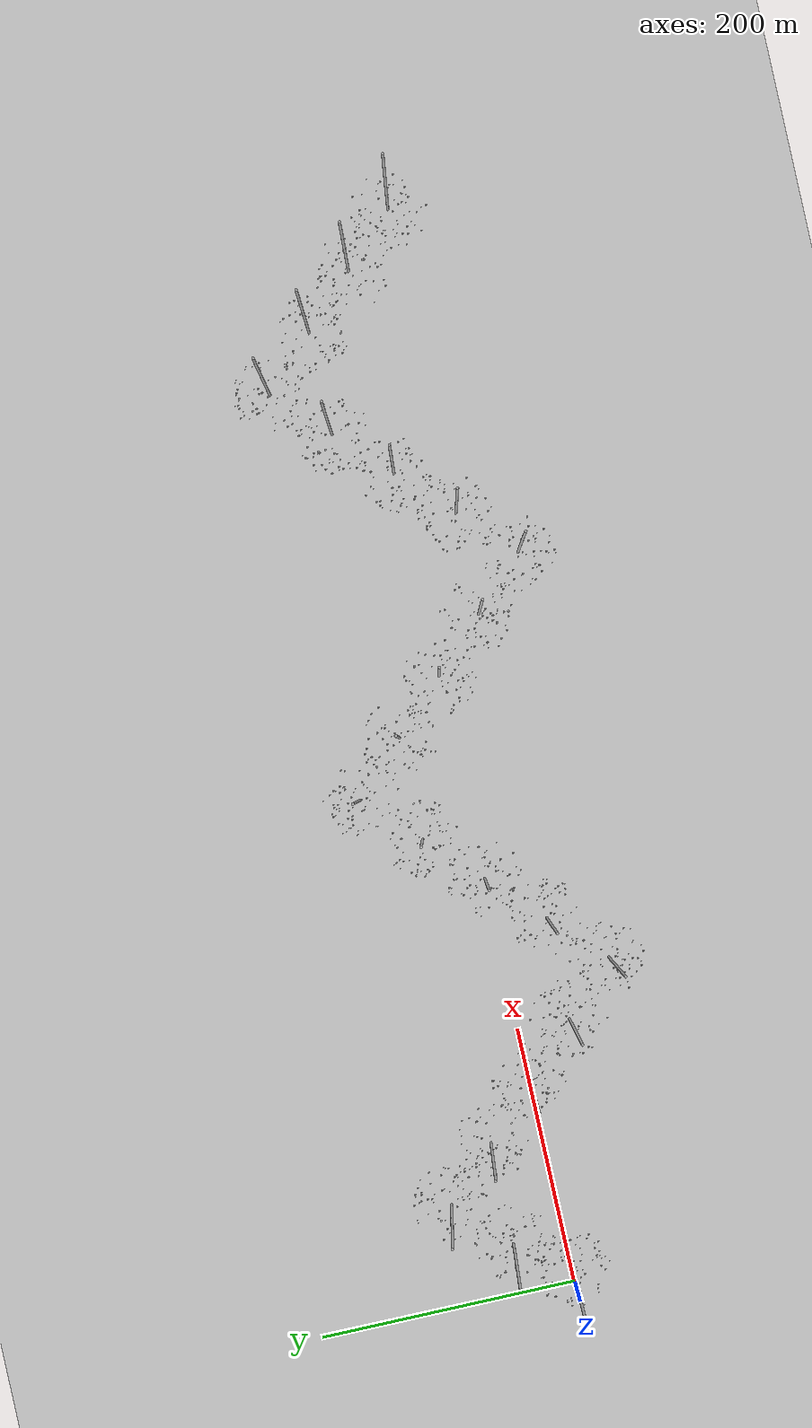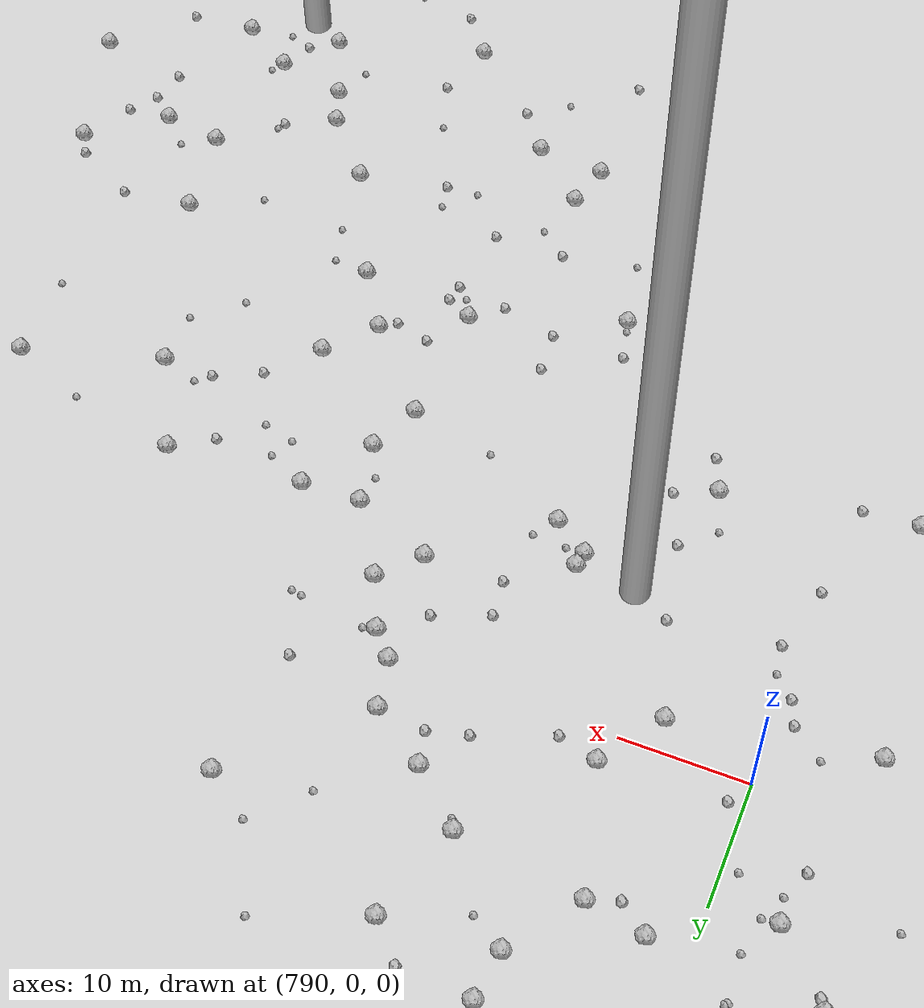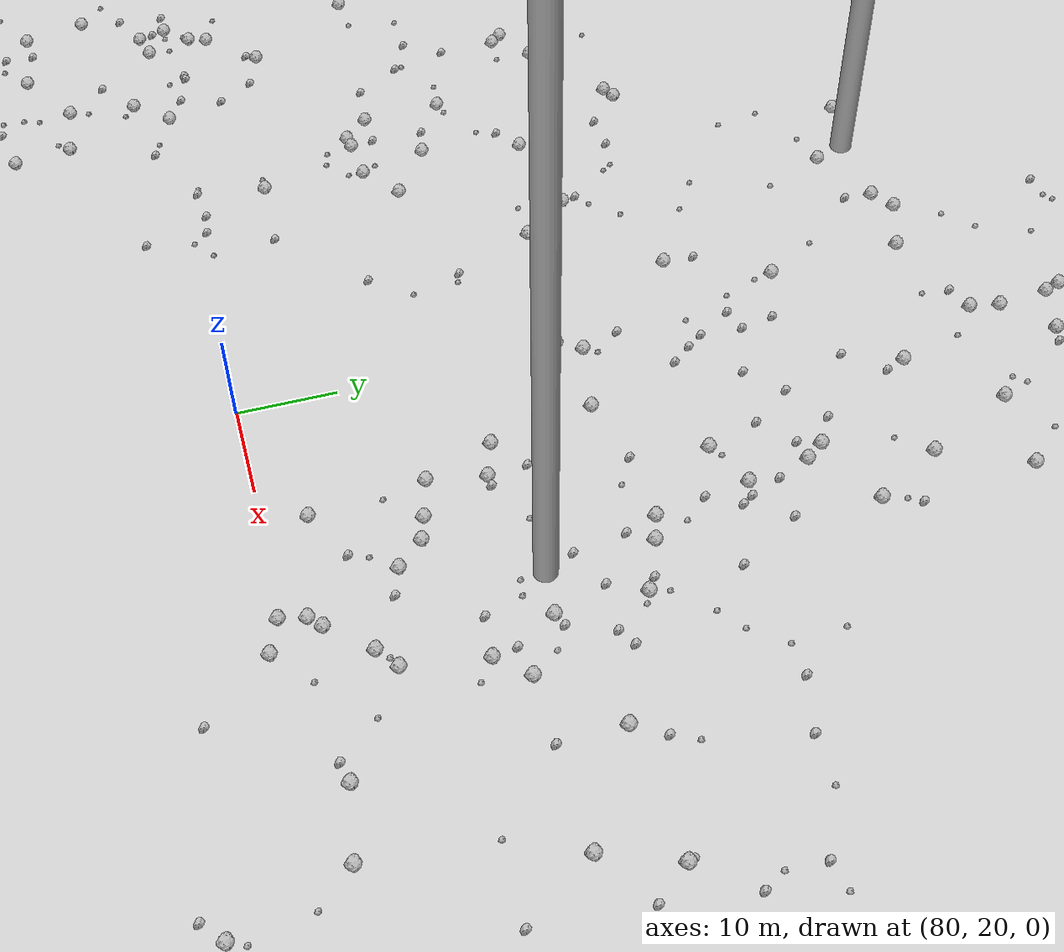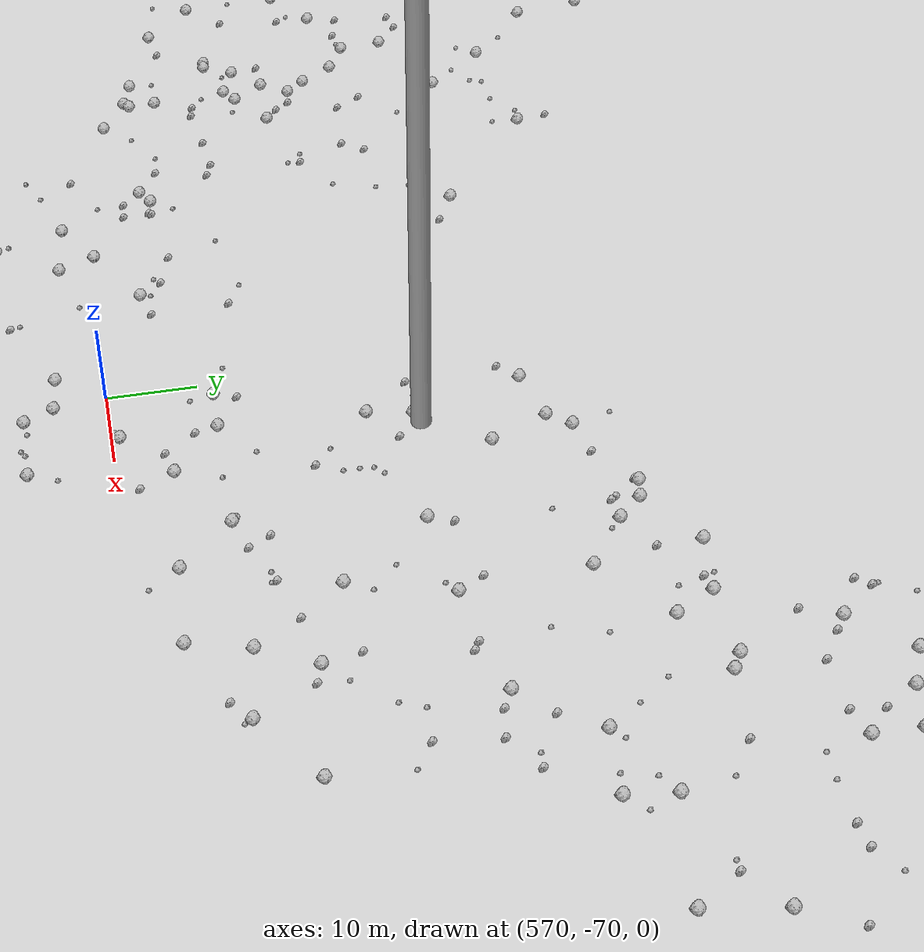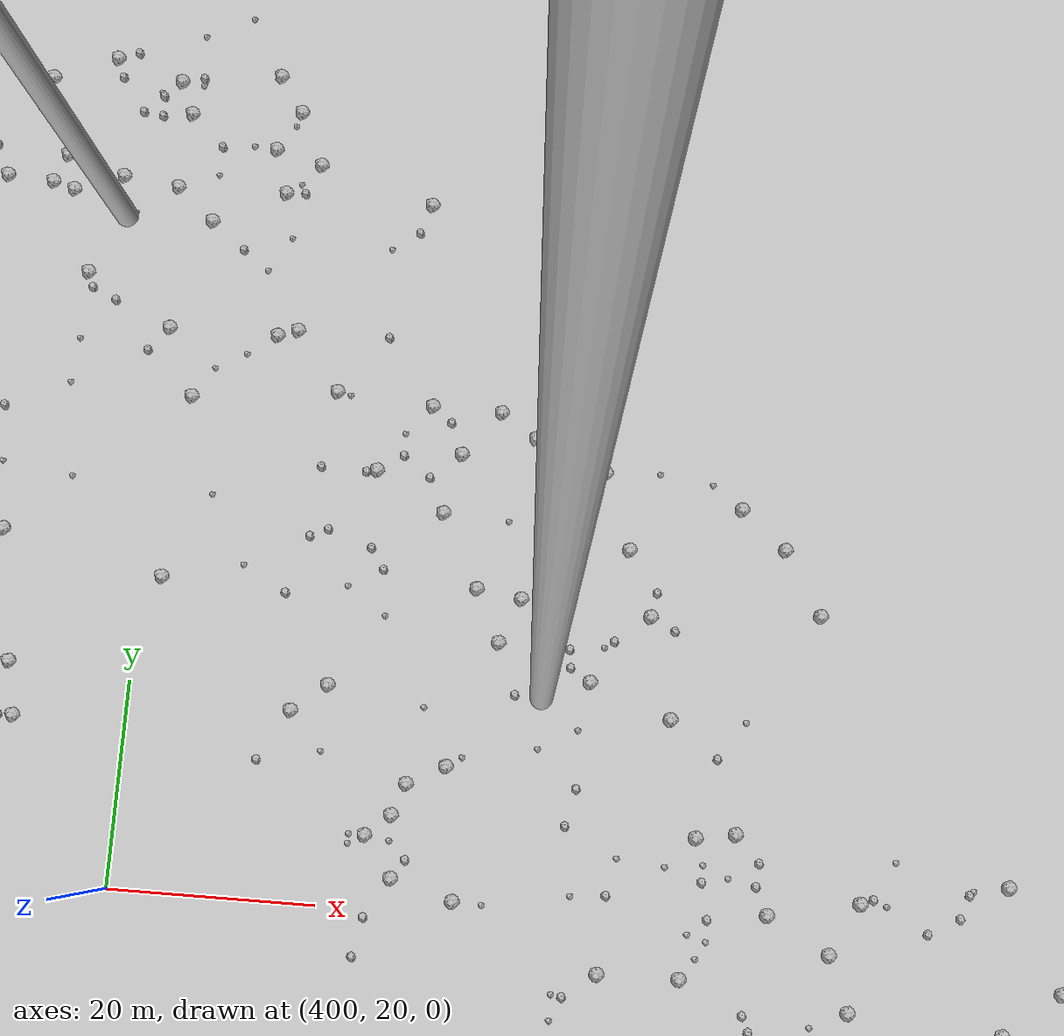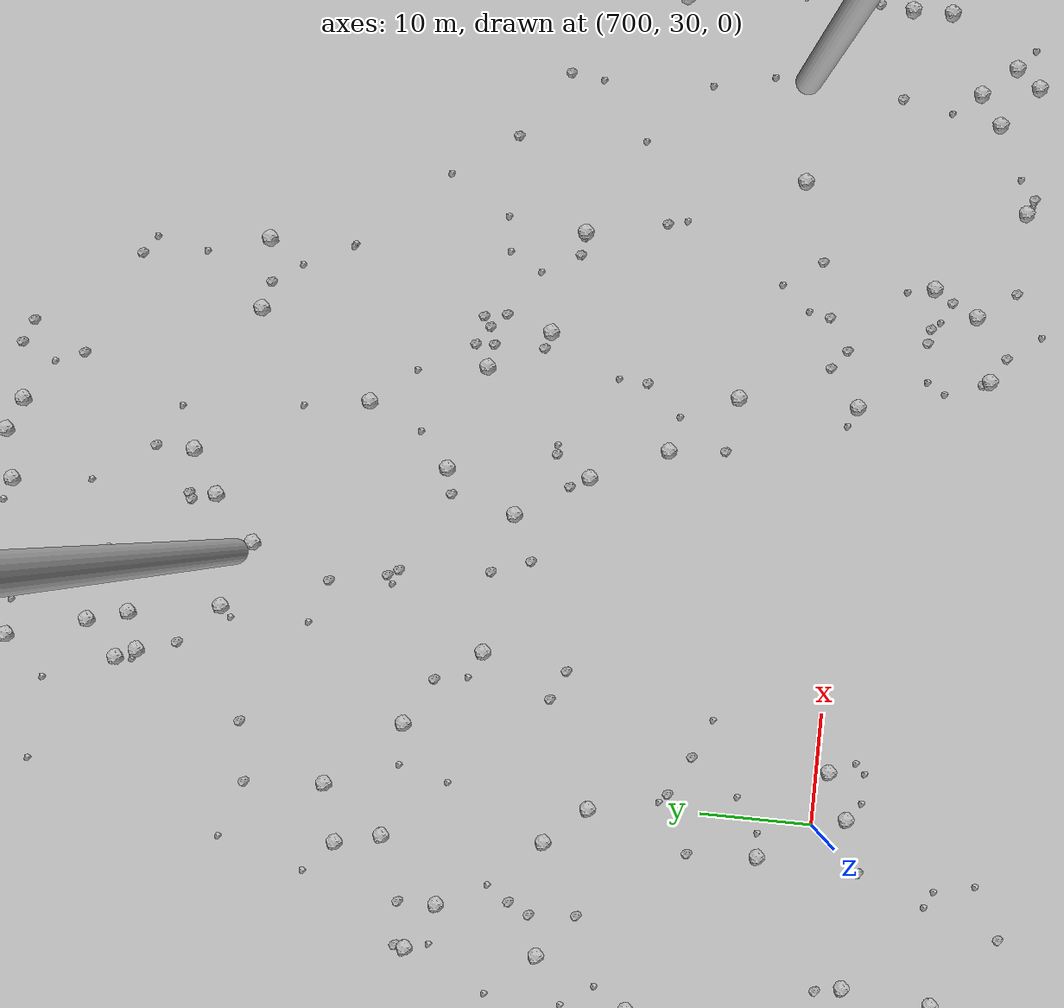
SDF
<sdf version="1.6">
 <world name="default">
  <include><uri>model://custom_ground</uri></include>
  <include><uri>model://sun</uri></include>
  <spherical_coordinates>
   <surface_model>EARTH_WGS84</surface_model>
   <latitude_deg>38.161479</latitude_deg>
   <longitude_deg>-122.454630</longitude_deg>
   <elevation>488.0</elevation>
   <heading_deg>90</heading_deg>
  </spherical_coordinates>
  <model name="rock1_0_0">
   <include><uri>model://rock1</uri><pose>-6.136145947086405 23.548551806514133 0.5 0 0 0</pose></include>
  </model>
  <model name="rock1_0_1">
   <include><uri>model://rock1</uri><pose>26.311944511000796 -24.568540345085353 0.5 0 0 0</pose></include>
  </model>
  <model name="rock1_0_2">
   <include><uri>model://rock1</uri><pose>16.38472202316631 12.576833294972353 0.5 0 0 0</pose></include>
  </model>
  <model name="rock1_0_3">
   <include><uri>model://rock1</uri><pose>38.666671567406276 2.8859533389507277 0.5 0 0 0</pose></include>
  </model>
  <model name="rock1_0_4">
   <include><uri>model://rock1</uri><pose>14.48638362061807 -7.828021500809157 0.5 0 0 0</pose></include>
  </model>
  <model name="rock1_0_5">
   <include><uri>model://rock1</uri><pose>33.33442109412706 -18.09072243469169 0.5 0 0 0</pose></include>
  </model>
  <model name="rock1_0_6">
   <include><uri>model://rock1</uri><pose>-1.9257686582272484 -3.496941082281456 0.5 0 0 0</pose></include>
  </model>
  <model name="rock1_0_7">
   <include><uri>model://rock1</uri><pose>33.09460581212923 -17.99134010054423 0.5 0 0 0</pose></include>
  </model>
  <model name="rock1_0_8">
   <include><uri>model://rock1</uri><pose>7.4339800176624244 -22.608763867974567 0.5 0 0 0</pose></include>
  </model>
  <model name="rock1_0_9">
   <include><uri>model://rock1</uri><pose>15.44225910371128 -2.1399400903058137 0.5 0 0 0</pose></include>
  </model>
  <model name="rock1_0_10">
   <include><uri>model://rock1</uri><pose>8.037951693655753 22.768845974844623 0.5 0 0 0</pose></include>
  </model>
  <model name="rock1_0_11">
   <include><uri>model://rock1</uri><pose>-8.31565590357891 17.06055437844438 0.5 0 0 0</pose></include>
  </model>
  <model name="rock1_0_12">
   <include><uri>model://rock1</uri><pose>25.416227691091024 5.460396539424494 0.5 0 0 0</pose></include>
  </model>
  <model name="rock1_0_13">
   <include><uri>model://rock1</uri><pose>37.87958856216269 8.826659557855578 0.5 0 0 0</pose></include>
  </model>
  <model name="rock1_0_14">
   <include><uri>model://rock1</uri><pose>31.879508436571193 9.541084042498241 0.5 0 0 0</pose></include>
  </model>
  <model name="rock1_0_15">
   <include><uri>model://rock1</uri><pose>3.7547350243116924 -8.835048656869073 0.5 0 0 0</pose></include>
  </model>
  <model name="rock1_0_16">
   <include><uri>model://rock1</uri><pose>-1.020090760966795 8.423693279525082 0.5 0 0 0</pose></include>
  </model>
  <model name="rock1_0_17">
   <include><uri>model://rock1</uri><pose>4.000677360774738 -25.021590065186 0.5 0 0 0</pose></include>
  </model>
  <model name="rock1_0_18">
   <include><uri>model://rock1</uri><pose>31.86253146034342 -3.387310298215695 0.5 0 0 0</pose></include>
  </model>
  <model name="rock1_0_19">
   <include><uri>model://rock1</uri><pose>-8.566617958500917 -2.5591445728881403 0.5 0 0 0</pose></include>
  </model>
  <model name="rock1_0_20">
   <include><uri>model://rock1</uri><pose>17.84063832433683 6.132385539091061 0.5 0 0 0</pose></include>
  </model>
  <model name="rock1_0_21">
   <include><uri>model://rock1</uri><pose>-18.08846239760467 5.996686269308597 0.5 0 0 0</pose></include>
  </model>
  <model name="rock1_0_22">
   <include><uri>model://rock1</uri><pose>22.48135426009425 24.186851182370738 0.5 0 0 0</pose></include>
  </model>
  <model name="rock1_0_23">
   <include><uri>model://rock1</uri><pose>32.5552385660743 16.52535043493029 0.5 0 0 0</pose></include>
  </model>
  <model name="rock1_0_24">
   <include><uri>model://rock1</uri><pose>18.792504933756966 -23.532087552940546 0.5 0 0 0</pose></include>
  </model>
  <model name="rock1_0_25">
   <include><uri>model://rock1</uri><pose>21.840801147512558 -20.445981498420522 0.5 0 0 0</pose></include>
  </model>
  <model name="rock1_0_26">
   <include><uri>model://rock1</uri><pose>15.783993682109802 -21.0559747383871 0.5 0 0 0</pose></include>
  </model>
  <model name="rock2_0_0">
   <include><uri>model://rock2</uri><pose>20.35867433910009 20.263287933654496 0.3 0 0 0</pose></include>
  </model>
  <model name="rock2_0_1">
   <include><uri>model://rock2</uri><pose>-6.420057476337027 -17.18356675004751 0.3 0 0 0</pose></include>
  </model>
  <model name="rock2_0_2">
   <include><uri>model://rock2</uri><pose>-19.292497370783018 -3.532705289228563 0.3 0 0 0</pose></include>
  </model>
  <model name="rock2_0_3">
   <include><uri>model://rock2</uri><pose>-14.700126244412955 8.82761470885361 0.3 0 0 0</pose></include>
  </model>
  <model name="rock2_0_4">
   <include><uri>model://rock2</uri><pose>10.533150984032364 -3.394761915025896 0.3 0 0 0</pose></include>
  </model>
  <model name="rock2_0_5">
   <include><uri>model://rock2</uri><pose>13.091651141031264 -24.363454358710975 0.3 0 0 0</pose></include>
  </model>
  <model name="rock2_0_6">
   <include><uri>model://rock2</uri><pose>32.878114607984216 -9.02727493864117 0.3 0 0 0</pose></include>
  </model>
  <model name="rock2_0_7">
   <include><uri>model://rock2</uri><pose>4.024547663177302 22.19025801449986 0.3 0 0 0</pose></include>
  </model>
  <model name="rock2_0_8">
   <include><uri>model://rock2</uri><pose>1.8354044830788183 -5.222071459125949 0.3 0 0 0</pose></include>
  </model>
  <model name="rock2_0_9">
   <include><uri>model://rock2</uri><pose>33.44732824001764 1.8724094145796002 0.3 0 0 0</pose></include>
  </model>
  <model name="rock2_0_10">
   <include><uri>model://rock2</uri><pose>20.548957340935722 3.492749802138434 0.3 0 0 0</pose></include>
  </model>
  <model name="rock2_0_11">
   <include><uri>model://rock2</uri><pose>25.777438092008524 -21.017981441717367 0.3 0 0 0</pose></include>
  </model>
  <model name="rock2_0_12">
   <include><uri>model://rock2</uri><pose>12.557330759260708 19.87984767035519 0.3 0 0 0</pose></include>
  </model>
  <model name="rock2_0_13">
   <include><uri>model://rock2</uri><pose>12.843293731347394 -16.67156156949233 0.3 0 0 0</pose></include>
  </model>
  <model name="rock2_0_14">
   <include><uri>model://rock2</uri><pose>20.655295430506598 6.476425373296252 0.3 0 0 0</pose></include>
  </model>
  <model name="rock2_0_15">
   <include><uri>model://rock2</uri><pose>-10.41793856014737 -2.696792015451699 0.3 0 0 0</pose></include>
  </model>
  <model name="rock2_0_16">
   <include><uri>model://rock2</uri><pose>30.372396845301076 -16.13574356893094 0.3 0 0 0</pose></include>
  </model>
  <model name="rock2_0_17">
   <include><uri>model://rock2</uri><pose>-13.007291033218362 8.48684860564304 0.3 0 0 0</pose></include>
  </model>
  <model name="rock2_0_18">
   <include><uri>model://rock2</uri><pose>-9.238334292893587 -16.060435108954564 0.3 0 0 0</pose></include>
  </model>
  <model name="rock2_0_19">
   <include><uri>model://rock2</uri><pose>-14.2431115458143 5.822612355498677 0.3 0 0 0</pose></include>
  </model>
  <model name="rock2_0_20">
   <include><uri>model://rock2</uri><pose>-12.305396868071254 -16.285127670697605 0.3 0 0 0</pose></include>
  </model>
  <model name="rock2_0_21">
   <include><uri>model://rock2</uri><pose>7.503005636352473 -3.639186216291506 0.3 0 0 0</pose></include>
  </model>
  <model name="rock2_0_22">
   <include><uri>model://rock2</uri><pose>7.975739896341384 24.860645729933744 0.3 0 0 0</pose></include>
  </model>
  <model name="rock2_0_23">
   <include><uri>model://rock2</uri><pose>16.98425976276286 16.927109195832152 0.3 0 0 0</pose></include>
  </model>
  <model name="rock2_0_24">
   <include><uri>model://rock2</uri><pose>1.0134711796510132 13.749703670968657 0.3 0 0 0</pose></include>
  </model>
  <model name="rock2_0_25">
   <include><uri>model://rock2</uri><pose>18.800286800258142 -9.660134297727666 0.3 0 0 0</pose></include>
  </model>
  <model name="rock2_0_26">
   <include><uri>model://rock2</uri><pose>-12.02107869696659 5.846855038706003 0.3 0 0 0</pose></include>
  </model>
  <model name="rock3_0_0">
   <include><uri>model://rock3</uri><pose>6.373886180208121 10.474063631431669 0.2 0 0 0</pose></include>
  </model>
  <model name="rock3_0_1">
   <include><uri>model://rock3</uri><pose>29.57362587714436 20.952420956619605 0.2 0 0 0</pose></include>
  </model>
  <model name="rock3_0_2">
   <include><uri>model://rock3</uri><pose>25.57471965138661 -3.9990422012507807 0.2 0 0 0</pose></include>
  </model>
  <model name="rock3_0_3">
   <include><uri>model://rock3</uri><pose>21.48349477456661 23.646266558348884 0.2 0 0 0</pose></include>
  </model>
  <model name="rock3_0_4">
   <include><uri>model://rock3</uri><pose>36.54391465055342 7.670747703489916 0.2 0 0 0</pose></include>
  </model>
  <model name="rock3_0_5">
   <include><uri>model://rock3</uri><pose>13.360471180800545 -27.046272833278444 0.2 0 0 0</pose></include>
  </model>
  <model name="rock3_0_6">
   <include><uri>model://rock3</uri><pose>15.02384519389507 -23.12701856196893 0.2 0 0 0</pose></include>
  </model>
  <model name="rock3_0_7">
   <include><uri>model://rock3</uri><pose>9.588277662315644 -29.83701791645252 0.2 0 0 0</pose></include>
  </model>
  <model name="rock3_0_8">
   <include><uri>model://rock3</uri><pose>31.509807388814025 4.394522941775804 0.2 0 0 0</pose></include>
  </model>
  <model name="rock3_0_9">
   <include><uri>model://rock3</uri><pose>33.69590301759455 -11.474569204893083 0.2 0 0 0</pose></include>
  </model>
  <model name="rock3_0_10">
   <include><uri>model://rock3</uri><pose>31.46719693794693 2.1550060541926896 0.2 0 0 0</pose></include>
  </model>
  <model name="rock3_0_11">
   <include><uri>model://rock3</uri><pose>27.35466135730381 -1.7111205673370335 0.2 0 0 0</pose></include>
  </model>
  <model name="rock3_0_12">
   <include><uri>model://rock3</uri><pose>-2.6739871222972376 16.702948135236284 0.2 0 0 0</pose></include>
  </model>
  <model name="rock3_0_13">
   <include><uri>model://rock3</uri><pose>13.529808731398028 15.07959923977765 0.2 0 0 0</pose></include>
  </model>
  <model name="rock3_0_14">
   <include><uri>model://rock3</uri><pose>23.963224446167807 -9.620095590775968 0.2 0 0 0</pose></include>
  </model>
  <model name="rock3_0_15">
   <include><uri>model://rock3</uri><pose>-3.1190934929359457 7.8480763080404685 0.2 0 0 0</pose></include>
  </model>
  <model name="rock3_0_16">
   <include><uri>model://rock3</uri><pose>7.471415144154172 -7.984243618127486 0.2 0 0 0</pose></include>
  </model>
  <model name="rock3_0_17">
   <include><uri>model://rock3</uri><pose>3.2135777989927803 17.36443690230373 0.2 0 0 0</pose></include>
  </model>
  <model name="rock3_0_18">
   <include><uri>model://rock3</uri><pose>22.462789574570586 3.1142524109246423 0.2 0 0 0</pose></include>
  </model>
  <model name="rock3_0_19">
   <include><uri>model://rock3</uri><pose>-5.228607397631993 21.775635563078232 0.2 0 0 0</pose></include>
  </model>
  <model name="rock3_0_20">
   <include><uri>model://rock3</uri><pose>12.95067233761688 -17.19411698682683 0.2 0 0 0</pose></include>
  </model>
  <model name="rock3_0_21">
   <include><uri>model://rock3</uri><pose>21.256151793661807 21.5980782853307 0.2 0 0 0</pose></include>
  </model>
  <model name="rock3_0_22">
   <include><uri>model://rock3</uri><pose>32.061510537019124 6.039416904306314 0.2 0 0 0</pose></include>
  </model>
  <model name="rock3_0_23">
   <include><uri>model://rock3</uri><pose>27.30855647200707 -6.751027252668077 0.2 0 0 0</pose></include>
  </model>
  <model name="rock3_0_24">
   <include><uri>model://rock3</uri><pose>-8.61299767585338 6.659016875097535 0.2 0 0 0</pose></include>
  </model>
  <model name="rock3_0_25">
   <include><uri>model://rock3</uri><pose>14.248827202610158 -20.659702024615736 0.2 0 0 0</pose></include>
  </model>
  <model name="rock3_0_26">
   <include><uri>model://rock3</uri><pose>12.756179020156814 3.4229263449950693 0.2 0 0 0</pose></include>
  </model>
  <model name="rock1_1_0">
   <include><uri>model://rock1</uri><pose>31.40074625642707 59.093850522413426 0.5 0 0 0</pose></include>
  </model>
  <model name="rock1_1_1">
   <include><uri>model://rock1</uri><pose>45.599898839777836 38.604244801151104 0.5 0 0 0</pose></include>
  </model>
  <model name="rock1_1_2">
   <include><uri>model://rock1</uri><pose>54.97198781175001 58.30701368858946 0.5 0 0 0</pose></include>
  </model>
  <model name="rock1_1_3">
   <include><uri>model://rock1</uri><pose>23.702264041223348 19.508691249184267 0.5 0 0 0</pose></include>
  </model>
  <model name="rock1_1_4">
   <include><uri>model://rock1</uri><pose>48.414060020545826 45.88589377359103 0.5 0 0 0</pose></include>
  </model>
  <model name="rock1_1_5">
   <include><uri>model://rock1</uri><pose>41.77969079045513 40.92410549648056 0.5 0 0 0</pose></include>
  </model>
  <model name="rock1_1_6">
   <include><uri>model://rock1</uri><pose>49.729189548229755 28.263838973411744 0.5 0 0 0</pose></include>
  </model>
  <model name="rock1_1_7">
   <include><uri>model://rock1</uri><pose>17.198957944792262 57.86300168655306 0.5 0 0 0</pose></include>
  </model>
  <model name="rock1_1_8">
   <include><uri>model://rock1</uri><pose>50.380855868773665 56.38865898931976 0.5 0 0 0</pose></include>
  </model>
  <model name="rock1_1_9">
   <include><uri>model://rock1</uri><pose>64.00752524897565 53.62867880405729 0.5 0 0 0</pose></include>
  </model>
  <model name="rock1_1_10">
   <include><uri>model://rock1</uri><pose>14.70037681491426 34.37226227901076 0.5 0 0 0</pose></include>
  </model>
  <model name="rock1_1_11">
   <include><uri>model://rock1</uri><pose>20.7190305513641 42.2931457839895 0.5 0 0 0</pose></include>
  </model>
  <model name="rock1_1_12">
   <include><uri>model://rock1</uri><pose>35.73094820355394 20.070955372941434 0.5 0 0 0</pose></include>
  </model>
  <model name="rock1_1_13">
   <include><uri>model://rock1</uri><pose>44.22302148093445 38.38061168331964 0.5 0 0 0</pose></include>
  </model>
  <model name="rock1_1_14">
   <include><uri>model://rock1</uri><pose>50.13408306712946 38.958288050992586 0.5 0 0 0</pose></include>
  </model>
  <model name="rock1_1_15">
   <include><uri>model://rock1</uri><pose>43.88575242835712 67.98692916997848 0.5 0 0 0</pose></include>
  </model>
  <model name="rock1_1_16">
   <include><uri>model://rock1</uri><pose>35.492894639601325 61.56214682088247 0.5 0 0 0</pose></include>
  </model>
  <model name="rock1_1_17">
   <include><uri>model://rock1</uri><pose>45.23476512266907 68.73951733514107 0.5 0 0 0</pose></include>
  </model>
  <model name="rock1_1_18">
   <include><uri>model://rock1</uri><pose>20.120226748584813 21.655233168407577 0.5 0 0 0</pose></include>
  </model>
  <model name="rock1_1_19">
   <include><uri>model://rock1</uri><pose>27.783307440895975 31.184213692463164 0.5 0 0 0</pose></include>
  </model>
  <model name="rock1_1_20">
   <include><uri>model://rock1</uri><pose>15.620308398353874 55.891359563534444 0.5 0 0 0</pose></include>
  </model>
  <model name="rock1_1_21">
   <include><uri>model://rock1</uri><pose>20.990913744409973 18.76639257389258 0.5 0 0 0</pose></include>
  </model>
  <model name="rock1_1_22">
   <include><uri>model://rock1</uri><pose>18.444728401425564 50.989416779683296 0.5 0 0 0</pose></include>
  </model>
  <model name="rock1_1_23">
   <include><uri>model://rock1</uri><pose>41.36732690153532 49.24274265986259 0.5 0 0 0</pose></include>
  </model>
  <model name="rock1_1_24">
   <include><uri>model://rock1</uri><pose>32.40490010426954 57.94817245136455 0.5 0 0 0</pose></include>
  </model>
  <model name="rock1_1_25">
   <include><uri>model://rock1</uri><pose>54.09711327660023 42.034587785178665 0.5 0 0 0</pose></include>
  </model>
  <model name="rock1_1_26">
   <include><uri>model://rock1</uri><pose>23.10005759301203 26.141134105842358 0.5 0 0 0</pose></include>
  </model>
  <model name="rock2_1_0">
   <include><uri>model://rock2</uri><pose>54.66686022351373 21.200723623737144 0.3 0 0 0</pose></include>
  </model>
  <model name="rock2_1_1">
   <include><uri>model://rock2</uri><pose>32.41758767608786 51.908616998640944 0.3 0 0 0</pose></include>
  </model>
  <model name="rock2_1_2">
   <include><uri>model://rock2</uri><pose>67.63166600708783 45.32080765657953 0.3 0 0 0</pose></include>
  </model>
  <model name="rock2_1_3">
   <include><uri>model://rock2</uri><pose>27.0544276833919 30.084654752359302 0.3 0 0 0</pose></include>
  </model>
  <model name="rock2_1_4">
   <include><uri>model://rock2</uri><pose>33.94780333466763 46.10323450708131 0.3 0 0 0</pose></include>
  </model>
  <model name="rock2_1_5">
   <include><uri>model://rock2</uri><pose>52.20522323398973 21.53662194110442 0.3 0 0 0</pose></include>
  </model>
  <model name="rock2_1_6">
   <include><uri>model://rock2</uri><pose>41.13850612274214 17.706680234467562 0.3 0 0 0</pose></include>
  </model>
  <model name="rock2_1_7">
   <include><uri>model://rock2</uri><pose>31.8894665400757 29.725780686864294 0.3 0 0 0</pose></include>
  </model>
  <model name="rock2_1_8">
   <include><uri>model://rock2</uri><pose>30.008151861694156 47.959999785772034 0.3 0 0 0</pose></include>
  </model>
  <model name="rock2_1_9">
   <include><uri>model://rock2</uri><pose>15.661037786241605 42.19677746794129 0.3 0 0 0</pose></include>
  </model>
  <model name="rock2_1_10">
   <include><uri>model://rock2</uri><pose>34.1756159035362 26.077074637313856 0.3 0 0 0</pose></include>
  </model>
  <model name="rock2_1_11">
   <include><uri>model://rock2</uri><pose>28.574331098780917 22.737218965614197 0.3 0 0 0</pose></include>
  </model>
  <model name="rock2_1_12">
   <include><uri>model://rock2</uri><pose>45.18782212358197 41.059438604261466 0.3 0 0 0</pose></include>
  </model>
  <model name="rock2_1_13">
   <include><uri>model://rock2</uri><pose>28.474648113432984 13.483101158276178 0.3 0 0 0</pose></include>
  </model>
  <model name="rock2_1_14">
   <include><uri>model://rock2</uri><pose>66.1048008621544 36.07612514196586 0.3 0 0 0</pose></include>
  </model>
  <model name="rock2_1_15">
   <include><uri>model://rock2</uri><pose>29.206903171876743 22.825372457519805 0.3 0 0 0</pose></include>
  </model>
  <model name="rock2_1_16">
   <include><uri>model://rock2</uri><pose>36.86658600492339 41.47188301856673 0.3 0 0 0</pose></include>
  </model>
  <model name="rock2_1_17">
   <include><uri>model://rock2</uri><pose>52.5724549185895 65.66903723615727 0.3 0 0 0</pose></include>
  </model>
  <model name="rock2_1_18">
   <include><uri>model://rock2</uri><pose>57.530667408759605 27.921058240295157 0.3 0 0 0</pose></include>
  </model>
  <model name="rock2_1_19">
   <include><uri>model://rock2</uri><pose>48.57533529871469 21.15259097779436 0.3 0 0 0</pose></include>
  </model>
  <model name="rock2_1_20">
   <include><uri>model://rock2</uri><pose>54.96857369186492 14.816478898366546 0.3 0 0 0</pose></include>
  </model>
  <model name="rock2_1_21">
   <include><uri>model://rock2</uri><pose>32.8112853681356 21.749811955980555 0.3 0 0 0</pose></include>
  </model>
  <model name="rock2_1_22">
   <include><uri>model://rock2</uri><pose>48.71465073742941 65.44641635929375 0.3 0 0 0</pose></include>
  </model>
  <model name="rock2_1_23">
   <include><uri>model://rock2</uri><pose>45.28966111206413 46.53280975974448 0.3 0 0 0</pose></include>
  </model>
  <model name="rock2_1_24">
   <include><uri>model://rock2</uri><pose>17.509431229212225 21.673457463082833 0.3 0 0 0</pose></include>
  </model>
  <model name="rock2_1_25">
   <include><uri>model://rock2</uri><pose>19.90268605988979 50.75019985889389 0.3 0 0 0</pose></include>
  </model>
  <model name="rock2_1_26">
   <include><uri>model://rock2</uri><pose>47.652830382260824 54.46295954774742 0.3 0 0 0</pose></include>
  </model>
  <model name="rock3_1_0">
   <include><uri>model://rock3</uri><pose>45.89717917422832 35.841689596838144 0.2 0 0 0</pose></include>
  </model>
  <model name="rock3_1_1">
   <include><uri>model://rock3</uri><pose>33.66454989914682 15.422352160692036 0.2 0 0 0</pose></include>
  </model>
  <model name="rock3_1_2">
   <include><uri>model://rock3</uri><pose>56.47229349242537 64.2181508902109 0.2 0 0 0</pose></include>
  </model>
  <model name="rock3_1_3">
   <include><uri>model://rock3</uri><pose>61.115014607229604 61.17153969893131 0.2 0 0 0</pose></include>
  </model>
  <model name="rock3_1_4">
   <include><uri>model://rock3</uri><pose>25.472689851677025 47.92406668893836 0.2 0 0 0</pose></include>
  </model>
  <model name="rock3_1_5">
   <include><uri>model://rock3</uri><pose>47.58928097997059 35.40900001320546 0.2 0 0 0</pose></include>
  </model>
  <model name="rock3_1_6">
   <include><uri>model://rock3</uri><pose>55.89653914971701 19.720935740726787 0.2 0 0 0</pose></include>
  </model>
  <model name="rock3_1_7">
   <include><uri>model://rock3</uri><pose>58.07602986105878 21.37098492663092 0.2 0 0 0</pose></include>
  </model>
  <model name="rock3_1_8">
   <include><uri>model://rock3</uri><pose>47.73981940927569 21.346892709886404 0.2 0 0 0</pose></include>
  </model>
  <model name="rock3_1_9">
   <include><uri>model://rock3</uri><pose>33.625772836693166 46.914172563274334 0.2 0 0 0</pose></include>
  </model>
  <model name="rock3_1_10">
   <include><uri>model://rock3</uri><pose>19.372573987204614 27.418768209444877 0.2 0 0 0</pose></include>
  </model>
  <model name="rock3_1_11">
   <include><uri>model://rock3</uri><pose>69.16839016911807 40.16050341781708 0.2 0 0 0</pose></include>
  </model>
  <model name="rock3_1_12">
   <include><uri>model://rock3</uri><pose>37.98230308587399 49.68121062435187 0.2 0 0 0</pose></include>
  </model>
  <model name="rock3_1_13">
   <include><uri>model://rock3</uri><pose>59.77166100497252 53.75650360231259 0.2 0 0 0</pose></include>
  </model>
  <model name="rock3_1_14">
   <include><uri>model://rock3</uri><pose>49.09300041362772 40.470995345196826 0.2 0 0 0</pose></include>
  </model>
  <model name="rock3_1_15">
   <include><uri>model://rock3</uri><pose>24.559110936804657 42.65127347102467 0.2 0 0 0</pose></include>
  </model>
  <model name="rock3_1_16">
   <include><uri>model://rock3</uri><pose>39.426976332509014 18.365738853943178 0.2 0 0 0</pose></include>
  </model>
  <model name="rock3_1_17">
   <include><uri>model://rock3</uri><pose>49.82213603038645 37.43997838541267 0.2 0 0 0</pose></include>
  </model>
  <model name="rock3_1_18">
   <include><uri>model://rock3</uri><pose>17.27880054223211 54.613088784886024 0.2 0 0 0</pose></include>
  </model>
  <model name="rock3_1_19">
   <include><uri>model://rock3</uri><pose>42.52281396544023 49.76318233455649 0.2 0 0 0</pose></include>
  </model>
  <model name="rock3_1_20">
   <include><uri>model://rock3</uri><pose>68.69900816550978 44.9228682857078 0.2 0 0 0</pose></include>
  </model>
  <model name="rock3_1_21">
   <include><uri>model://rock3</uri><pose>48.03823629580798 28.300081540826895 0.2 0 0 0</pose></include>
  </model>
  <model name="rock3_1_22">
   <include><uri>model://rock3</uri><pose>46.76190306249438 52.41273949503032 0.2 0 0 0</pose></include>
  </model>
  <model name="rock3_1_23">
   <include><uri>model://rock3</uri><pose>35.19350562484665 57.811505230126855 0.2 0 0 0</pose></include>
  </model>
  <model name="rock3_1_24">
   <include><uri>model://rock3</uri><pose>23.552051980272807 21.780846535411897 0.2 0 0 0</pose></include>
  </model>
  <model name="rock3_1_25">
   <include><uri>model://rock3</uri><pose>32.106349325716636 11.490270191434995 0.2 0 0 0</pose></include>
  </model>
  <model name="rock3_1_26">
   <include><uri>model://rock3</uri><pose>33.59716466054669 68.47678339319782 0.2 0 0 0</pose></include>
  </model>
  <model name="rock1_2_0">
   <include><uri>model://rock1</uri><pose>85.62611955410854 104.23992162711227 0.5 0 0 0</pose></include>
  </model>
  <model name="rock1_2_1">
   <include><uri>model://rock1</uri><pose>75.85152309420278 90.36875917660831 0.5 0 0 0</pose></include>
  </model>
  <model name="rock1_2_2">
   <include><uri>model://rock1</uri><pose>60.212300172897905 58.49612187408172 0.5 0 0 0</pose></include>
  </model>
  <model name="rock1_2_3">
   <include><uri>model://rock1</uri><pose>91.12113621669855 84.88043657255682 0.5 0 0 0</pose></include>
  </model>
  <model name="rock1_2_4">
   <include><uri>model://rock1</uri><pose>68.05163922223953 90.67024963705808 0.5 0 0 0</pose></include>
  </model>
  <model name="rock1_2_5">
   <include><uri>model://rock1</uri><pose>84.48906288122257 108.56404100727244 0.5 0 0 0</pose></include>
  </model>
  <model name="rock1_2_6">
   <include><uri>model://rock1</uri><pose>86.22553979626213 94.10198785138549 0.5 0 0 0</pose></include>
  </model>
  <model name="rock1_2_7">
   <include><uri>model://rock1</uri><pose>91.28424914528577 101.30444016027708 0.5 0 0 0</pose></include>
  </model>
  <model name="rock1_2_8">
   <include><uri>model://rock1</uri><pose>53.72882169368349 91.7092579215514 0.5 0 0 0</pose></include>
  </model>
  <model name="rock1_2_9">
   <include><uri>model://rock1</uri><pose>86.79664000635994 97.15609676271534 0.5 0 0 0</pose></include>
  </model>
  <model name="rock1_2_10">
   <include><uri>model://rock1</uri><pose>76.30858397124133 76.34180216184514 0.5 0 0 0</pose></include>
  </model>
  <model name="rock1_2_11">
   <include><uri>model://rock1</uri><pose>61.177629843454156 87.16164936527514 0.5 0 0 0</pose></include>
  </model>
  <model name="rock1_2_12">
   <include><uri>model://rock1</uri><pose>106.72714469665775 76.2723978534102 0.5 0 0 0</pose></include>
  </model>
  <model name="rock1_2_13">
   <include><uri>model://rock1</uri><pose>92.29508108123771 105.91922397221268 0.5 0 0 0</pose></include>
  </model>
  <model name="rock1_2_14">
   <include><uri>model://rock1</uri><pose>86.28228833509277 102.51232556177762 0.5 0 0 0</pose></include>
  </model>
  <model name="rock1_2_15">
   <include><uri>model://rock1</uri><pose>70.34274565105541 92.30939664023951 0.5 0 0 0</pose></include>
  </model>
  <model name="rock1_2_16">
   <include><uri>model://rock1</uri><pose>102.77287276095197 83.21065961740908 0.5 0 0 0</pose></include>
  </model>
  <model name="rock1_2_17">
   <include><uri>model://rock1</uri><pose>100.45722351147535 71.25798924689562 0.5 0 0 0</pose></include>
  </model>
  <model name="rock1_2_18">
   <include><uri>model://rock1</uri><pose>106.70162662964931 91.8863148103284 0.5 0 0 0</pose></include>
  </model>
  <model name="rock1_2_19">
   <include><uri>model://rock1</uri><pose>79.8093451330027 52.27253169497126 0.5 0 0 0</pose></include>
  </model>
  <model name="rock1_2_20">
   <include><uri>model://rock1</uri><pose>81.2359087338105 54.65215395806577 0.5 0 0 0</pose></include>
  </model>
  <model name="rock1_2_21">
   <include><uri>model://rock1</uri><pose>96.58992065558127 62.66119624953489 0.5 0 0 0</pose></include>
  </model>
  <model name="rock1_2_22">
   <include><uri>model://rock1</uri><pose>71.76875801635275 66.11144690705027 0.5 0 0 0</pose></include>
  </model>
  <model name="rock1_2_23">
   <include><uri>model://rock1</uri><pose>88.6515636827022 53.31631322055847 0.5 0 0 0</pose></include>
  </model>
  <model name="rock1_2_24">
   <include><uri>model://rock1</uri><pose>98.24795242802873 92.50373952966822 0.5 0 0 0</pose></include>
  </model>
  <model name="rock1_2_25">
   <include><uri>model://rock1</uri><pose>99.05015522088064 73.15410808310445 0.5 0 0 0</pose></include>
  </model>
  <model name="rock1_2_26">
   <include><uri>model://rock1</uri><pose>101.59232628598451 64.90877973168118 0.5 0 0 0</pose></include>
  </model>
  <model name="rock2_2_0">
   <include><uri>model://rock2</uri><pose>88.35515435011462 69.02621099408613 0.3 0 0 0</pose></include>
  </model>
  <model name="rock2_2_1">
   <include><uri>model://rock2</uri><pose>106.53471404765179 67.72240198523131 0.3 0 0 0</pose></include>
  </model>
  <model name="rock2_2_2">
   <include><uri>model://rock2</uri><pose>108.13237328611348 79.94286308037981 0.3 0 0 0</pose></include>
  </model>
  <model name="rock2_2_3">
   <include><uri>model://rock2</uri><pose>95.71019572971758 55.02805255564586 0.3 0 0 0</pose></include>
  </model>
  <model name="rock2_2_4">
   <include><uri>model://rock2</uri><pose>80.26504197554904 70.15633910954763 0.3 0 0 0</pose></include>
  </model>
  <model name="rock2_2_5">
   <include><uri>model://rock2</uri><pose>96.03881776537015 75.00783133584787 0.3 0 0 0</pose></include>
  </model>
  <model name="rock2_2_6">
   <include><uri>model://rock2</uri><pose>90.81421535316763 105.69767901912417 0.3 0 0 0</pose></include>
  </model>
  <model name="rock2_2_7">
   <include><uri>model://rock2</uri><pose>85.31609128065253 62.9624001573766 0.3 0 0 0</pose></include>
  </model>
  <model name="rock2_2_8">
   <include><uri>model://rock2</uri><pose>82.51761125382282 66.57973787789378 0.3 0 0 0</pose></include>
  </model>
  <model name="rock2_2_9">
   <include><uri>model://rock2</uri><pose>82.74890705833774 70.89468943182439 0.3 0 0 0</pose></include>
  </model>
  <model name="rock2_2_10">
   <include><uri>model://rock2</uri><pose>71.82126283656304 69.3367017422375 0.3 0 0 0</pose></include>
  </model>
  <model name="rock2_2_11">
   <include><uri>model://rock2</uri><pose>59.786166160443955 60.02985441156266 0.3 0 0 0</pose></include>
  </model>
  <model name="rock2_2_12">
   <include><uri>model://rock2</uri><pose>92.93394172043106 100.9168712857487 0.3 0 0 0</pose></include>
  </model>
  <model name="rock2_2_13">
   <include><uri>model://rock2</uri><pose>67.75323017810429 87.81132664996198 0.3 0 0 0</pose></include>
  </model>
  <model name="rock2_2_14">
   <include><uri>model://rock2</uri><pose>82.07026573048594 74.36552074270388 0.3 0 0 0</pose></include>
  </model>
  <model name="rock2_2_15">
   <include><uri>model://rock2</uri><pose>94.8517713929318 68.08384029225262 0.3 0 0 0</pose></include>
  </model>
  <model name="rock2_2_16">
   <include><uri>model://rock2</uri><pose>88.76515755101263 79.20520144450715 0.3 0 0 0</pose></include>
  </model>
  <model name="rock2_2_17">
   <include><uri>model://rock2</uri><pose>91.94839853348782 82.86049731934398 0.3 0 0 0</pose></include>
  </model>
  <model name="rock2_2_18">
   <include><uri>model://rock2</uri><pose>101.89665413247468 67.89466327310859 0.3 0 0 0</pose></include>
  </model>
  <model name="rock2_2_19">
   <include><uri>model://rock2</uri><pose>103.16467168921196 64.73721474385907 0.3 0 0 0</pose></include>
  </model>
  <model name="rock2_2_20">
   <include><uri>model://rock2</uri><pose>91.75747412134905 72.24381054954912 0.3 0 0 0</pose></include>
  </model>
  <model name="rock2_2_21">
   <include><uri>model://rock2</uri><pose>83.70989764148365 64.93481225092387 0.3 0 0 0</pose></include>
  </model>
  <model name="rock2_2_22">
   <include><uri>model://rock2</uri><pose>70.42333866731605 108.2087321353836 0.3 0 0 0</pose></include>
  </model>
  <model name="rock2_2_23">
   <include><uri>model://rock2</uri><pose>83.4411497544327 93.10998781137172 0.3 0 0 0</pose></include>
  </model>
  <model name="rock2_2_24">
   <include><uri>model://rock2</uri><pose>98.19210799191916 70.98522510801835 0.3 0 0 0</pose></include>
  </model>
  <model name="rock2_2_25">
   <include><uri>model://rock2</uri><pose>79.85065884157137 58.59639103880376 0.3 0 0 0</pose></include>
  </model>
  <model name="rock2_2_26">
   <include><uri>model://rock2</uri><pose>96.92377819944006 102.88275970551527 0.3 0 0 0</pose></include>
  </model>
  <model name="rock3_2_0">
   <include><uri>model://rock3</uri><pose>81.85142459273091 56.01567110972754 0.2 0 0 0</pose></include>
  </model>
  <model name="rock3_2_1">
   <include><uri>model://rock3</uri><pose>95.97155633692796 94.42552965637626 0.2 0 0 0</pose></include>
  </model>
  <model name="rock3_2_2">
   <include><uri>model://rock3</uri><pose>64.49003136673626 70.28745843929599 0.2 0 0 0</pose></include>
  </model>
  <model name="rock3_2_3">
   <include><uri>model://rock3</uri><pose>55.76848752590604 65.18614102204077 0.2 0 0 0</pose></include>
  </model>
  <model name="rock3_2_4">
   <include><uri>model://rock3</uri><pose>77.95500456386713 70.91181197323303 0.2 0 0 0</pose></include>
  </model>
  <model name="rock3_2_5">
   <include><uri>model://rock3</uri><pose>107.29685280210299 78.60938642777316 0.2 0 0 0</pose></include>
  </model>
  <model name="rock3_2_6">
   <include><uri>model://rock3</uri><pose>57.3987252682001 86.20594674550999 0.2 0 0 0</pose></include>
  </model>
  <model name="rock3_2_7">
   <include><uri>model://rock3</uri><pose>52.79303025934203 78.645414977108 0.2 0 0 0</pose></include>
  </model>
  <model name="rock3_2_8">
   <include><uri>model://rock3</uri><pose>63.68089374248739 80.81343042100917 0.2 0 0 0</pose></include>
  </model>
  <model name="rock3_2_9">
   <include><uri>model://rock3</uri><pose>80.11338427936218 65.80935956146142 0.2 0 0 0</pose></include>
  </model>
  <model name="rock3_2_10">
   <include><uri>model://rock3</uri><pose>63.554339610804035 63.97367938382548 0.2 0 0 0</pose></include>
  </model>
  <model name="rock3_2_11">
   <include><uri>model://rock3</uri><pose>77.60650856886559 104.94156725411598 0.2 0 0 0</pose></include>
  </model>
  <model name="rock3_2_12">
   <include><uri>model://rock3</uri><pose>102.9819502515206 95.67252555391218 0.2 0 0 0</pose></include>
  </model>
  <model name="rock3_2_13">
   <include><uri>model://rock3</uri><pose>97.70702736567591 63.59905135544327 0.2 0 0 0</pose></include>
  </model>
  <model name="rock3_2_14">
   <include><uri>model://rock3</uri><pose>60.870737800353574 72.58926469198565 0.2 0 0 0</pose></include>
  </model>
  <model name="rock3_2_15">
   <include><uri>model://rock3</uri><pose>72.84786139805003 108.52910133236347 0.2 0 0 0</pose></include>
  </model>
  <model name="rock3_2_16">
   <include><uri>model://rock3</uri><pose>89.36528429623158 91.46845745119074 0.2 0 0 0</pose></include>
  </model>
  <model name="rock3_2_17">
   <include><uri>model://rock3</uri><pose>75.34948770146444 99.57506656058885 0.2 0 0 0</pose></include>
  </model>
  <model name="rock3_2_18">
   <include><uri>model://rock3</uri><pose>83.03530571834172 90.28135662485337 0.2 0 0 0</pose></include>
  </model>
  <model name="rock3_2_19">
   <include><uri>model://rock3</uri><pose>73.06378973313453 81.76918493373726 0.2 0 0 0</pose></include>
  </model>
  <model name="rock3_2_20">
   <include><uri>model://rock3</uri><pose>102.50064790447645 99.61434458584492 0.2 0 0 0</pose></include>
  </model>
  <model name="rock3_2_21">
   <include><uri>model://rock3</uri><pose>96.97731400091558 95.55379524531746 0.2 0 0 0</pose></include>
  </model>
  <model name="rock3_2_22">
   <include><uri>model://rock3</uri><pose>52.079738466705294 83.24704340806645 0.2 0 0 0</pose></include>
  </model>
  <model name="rock3_2_23">
   <include><uri>model://rock3</uri><pose>72.65405943572097 96.83923865200774 0.2 0 0 0</pose></include>
  </model>
  <model name="rock3_2_24">
   <include><uri>model://rock3</uri><pose>73.7218280484206 109.23938099342391 0.2 0 0 0</pose></include>
  </model>
  <model name="rock3_2_25">
   <include><uri>model://rock3</uri><pose>76.51688177882302 74.44031986627205 0.2 0 0 0</pose></include>
  </model>
  <model name="rock3_2_26">
   <include><uri>model://rock3</uri><pose>100.10410258029447 80.20764196850695 0.2 0 0 0</pose></include>
  </model>
  <model name="rock1_3_0">
   <include><uri>model://rock1</uri><pose>93.29272774348706 35.7119621967002 0.5 0 0 0</pose></include>
  </model>
  <model name="rock1_3_1">
   <include><uri>model://rock1</uri><pose>94.50259546031613 24.264372650959185 0.5 0 0 0</pose></include>
  </model>
  <model name="rock1_3_2">
   <include><uri>model://rock1</uri><pose>146.49879628327975 43.76839218941309 0.5 0 0 0</pose></include>
  </model>
  <model name="rock1_3_3">
   <include><uri>model://rock1</uri><pose>106.88132863516134 23.17869396273393 0.5 0 0 0</pose></include>
  </model>
  <model name="rock1_3_4">
   <include><uri>model://rock1</uri><pose>99.96916981618871 33.76627754750596 0.5 0 0 0</pose></include>
  </model>
  <model name="rock1_3_5">
   <include><uri>model://rock1</uri><pose>108.5272402434184 18.147006244959393 0.5 0 0 0</pose></include>
  </model>
  <model name="rock1_3_6">
   <include><uri>model://rock1</uri><pose>114.03599092338455 36.814071784805336 0.5 0 0 0</pose></include>
  </model>
  <model name="rock1_3_7">
   <include><uri>model://rock1</uri><pose>110.97695432623408 52.135367625545186 0.5 0 0 0</pose></include>
  </model>
  <model name="rock1_3_8">
   <include><uri>model://rock1</uri><pose>102.4767580807673 31.056780841031134 0.5 0 0 0</pose></include>
  </model>
  <model name="rock1_3_9">
   <include><uri>model://rock1</uri><pose>105.01837243216585 19.49733417802015 0.5 0 0 0</pose></include>
  </model>
  <model name="rock1_3_10">
   <include><uri>model://rock1</uri><pose>123.70770485053126 46.301162916914926 0.5 0 0 0</pose></include>
  </model>
  <model name="rock1_3_11">
   <include><uri>model://rock1</uri><pose>94.3506372455283 41.46519960094277 0.5 0 0 0</pose></include>
  </model>
  <model name="rock1_3_12">
   <include><uri>model://rock1</uri><pose>130.1410600259341 21.08154805960112 0.5 0 0 0</pose></include>
  </model>
  <model name="rock1_3_13">
   <include><uri>model://rock1</uri><pose>111.12362342063632 43.255383902959835 0.5 0 0 0</pose></include>
  </model>
  <model name="rock1_3_14">
   <include><uri>model://rock1</uri><pose>116.79332922400755 39.74599554217485 0.5 0 0 0</pose></include>
  </model>
  <model name="rock1_3_15">
   <include><uri>model://rock1</uri><pose>105.69627713001877 54.39244498196216 0.5 0 0 0</pose></include>
  </model>
  <model name="rock1_3_16">
   <include><uri>model://rock1</uri><pose>112.7966510969266 28.74573100581094 0.5 0 0 0</pose></include>
  </model>
  <model name="rock1_3_17">
   <include><uri>model://rock1</uri><pose>97.46192241545953 34.55212702945539 0.5 0 0 0</pose></include>
  </model>
  <model name="rock1_3_18">
   <include><uri>model://rock1</uri><pose>145.31108129589393 24.72855524728879 0.5 0 0 0</pose></include>
  </model>
  <model name="rock1_3_19">
   <include><uri>model://rock1</uri><pose>105.59574934150938 22.051615553851523 0.5 0 0 0</pose></include>
  </model>
  <model name="rock1_3_20">
   <include><uri>model://rock1</uri><pose>134.4196083533353 40.00056384993887 0.5 0 0 0</pose></include>
  </model>
  <model name="rock1_3_21">
   <include><uri>model://rock1</uri><pose>110.53900330218198 27.14251326626186 0.5 0 0 0</pose></include>
  </model>
  <model name="rock1_3_22">
   <include><uri>model://rock1</uri><pose>90.58399734642728 42.72394336700356 0.5 0 0 0</pose></include>
  </model>
  <model name="rock1_3_23">
   <include><uri>model://rock1</uri><pose>144.8961107508319 25.857162964402164 0.5 0 0 0</pose></include>
  </model>
  <model name="rock1_3_24">
   <include><uri>model://rock1</uri><pose>137.21614461436877 47.09900080894182 0.5 0 0 0</pose></include>
  </model>
  <model name="rock1_3_25">
   <include><uri>model://rock1</uri><pose>122.82827185412363 22.339320127255657 0.5 0 0 0</pose></include>
  </model>
  <model name="rock1_3_26">
   <include><uri>model://rock1</uri><pose>103.08037228547575 55.27524657486328 0.5 0 0 0</pose></include>
  </model>
  <model name="rock2_3_0">
   <include><uri>model://rock2</uri><pose>110.45911822095066 61.334428672649004 0.3 0 0 0</pose></include>
  </model>
  <model name="rock2_3_1">
   <include><uri>model://rock2</uri><pose>103.92164017002291 63.60424686844167 0.3 0 0 0</pose></include>
  </model>
  <model name="rock2_3_2">
   <include><uri>model://rock2</uri><pose>113.52204239951287 39.246091882307894 0.3 0 0 0</pose></include>
  </model>
  <model name="rock2_3_3">
   <include><uri>model://rock2</uri><pose>105.0357752085775 46.75072110336722 0.3 0 0 0</pose></include>
  </model>
  <model name="rock2_3_4">
   <include><uri>model://rock2</uri><pose>99.77965211939205 26.929137015780164 0.3 0 0 0</pose></include>
  </model>
  <model name="rock2_3_5">
   <include><uri>model://rock2</uri><pose>95.47661455836551 41.571727319485476 0.3 0 0 0</pose></include>
  </model>
  <model name="rock2_3_6">
   <include><uri>model://rock2</uri><pose>136.99000404114483 47.67075501013777 0.3 0 0 0</pose></include>
  </model>
  <model name="rock2_3_7">
   <include><uri>model://rock2</uri><pose>93.9677185999228 45.44444644018737 0.3 0 0 0</pose></include>
  </model>
  <model name="rock2_3_8">
   <include><uri>model://rock2</uri><pose>125.50691236611908 49.36180190424638 0.3 0 0 0</pose></include>
  </model>
  <model name="rock2_3_9">
   <include><uri>model://rock2</uri><pose>123.04639309378156 62.64315213322382 0.3 0 0 0</pose></include>
  </model>
  <model name="rock2_3_10">
   <include><uri>model://rock2</uri><pose>109.15579530882098 48.64255055580097 0.3 0 0 0</pose></include>
  </model>
  <model name="rock2_3_11">
   <include><uri>model://rock2</uri><pose>109.57742929341094 53.1014898055084 0.3 0 0 0</pose></include>
  </model>
  <model name="rock2_3_12">
   <include><uri>model://rock2</uri><pose>109.61824698103636 37.28838168948455 0.3 0 0 0</pose></include>
  </model>
  <model name="rock2_3_13">
   <include><uri>model://rock2</uri><pose>112.43212520469305 43.86187115901354 0.3 0 0 0</pose></include>
  </model>
  <model name="rock2_3_14">
   <include><uri>model://rock2</uri><pose>141.19632066297433 52.27676700212945 0.3 0 0 0</pose></include>
  </model>
  <model name="rock2_3_15">
   <include><uri>model://rock2</uri><pose>140.09732980735163 58.234950849212055 0.3 0 0 0</pose></include>
  </model>
  <model name="rock2_3_16">
   <include><uri>model://rock2</uri><pose>104.1597460773719 52.099473166619994 0.3 0 0 0</pose></include>
  </model>
  <model name="rock2_3_17">
   <include><uri>model://rock2</uri><pose>139.19896483732 33.00506402767054 0.3 0 0 0</pose></include>
  </model>
  <model name="rock2_3_18">
   <include><uri>model://rock2</uri><pose>120.62545272018886 21.90622637582382 0.3 0 0 0</pose></include>
  </model>
  <model name="rock2_3_19">
   <include><uri>model://rock2</uri><pose>114.21833750513004 48.28184094030886 0.3 0 0 0</pose></include>
  </model>
  <model name="rock2_3_20">
   <include><uri>model://rock2</uri><pose>102.12863440162593 60.41380208347567 0.3 0 0 0</pose></include>
  </model>
  <model name="rock2_3_21">
   <include><uri>model://rock2</uri><pose>123.80865743934007 39.843296355349906 0.3 0 0 0</pose></include>
  </model>
  <model name="rock2_3_22">
   <include><uri>model://rock2</uri><pose>115.99967164193467 49.31916520868769 0.3 0 0 0</pose></include>
  </model>
  <model name="rock2_3_23">
   <include><uri>model://rock2</uri><pose>140.0152992798849 43.72792917637687 0.3 0 0 0</pose></include>
  </model>
  <model name="rock2_3_24">
   <include><uri>model://rock2</uri><pose>128.69605885760961 61.28220746482312 0.3 0 0 0</pose></include>
  </model>
  <model name="rock2_3_25">
   <include><uri>model://rock2</uri><pose>105.27291185223088 30.08957189859762 0.3 0 0 0</pose></include>
  </model>
  <model name="rock2_3_26">
   <include><uri>model://rock2</uri><pose>114.21300059809236 11.480851809253643 0.3 0 0 0</pose></include>
  </model>
  <model name="rock3_3_0">
   <include><uri>model://rock3</uri><pose>143.7039247179883 35.68201899613041 0.2 0 0 0</pose></include>
  </model>
  <model name="rock3_3_1">
   <include><uri>model://rock3</uri><pose>94.29534754834451 31.399247323844847 0.2 0 0 0</pose></include>
  </model>
  <model name="rock3_3_2">
   <include><uri>model://rock3</uri><pose>114.48431551638232 57.36176676521749 0.2 0 0 0</pose></include>
  </model>
  <model name="rock3_3_3">
   <include><uri>model://rock3</uri><pose>111.31769031506754 54.00746378540221 0.2 0 0 0</pose></include>
  </model>
  <model name="rock3_3_4">
   <include><uri>model://rock3</uri><pose>119.16774281171907 67.90592209519193 0.2 0 0 0</pose></include>
  </model>
  <model name="rock3_3_5">
   <include><uri>model://rock3</uri><pose>100.0741995719637 44.0209398507455 0.2 0 0 0</pose></include>
  </model>
  <model name="rock3_3_6">
   <include><uri>model://rock3</uri><pose>131.10511047685247 33.16986235990747 0.2 0 0 0</pose></include>
  </model>
  <model name="rock3_3_7">
   <include><uri>model://rock3</uri><pose>119.52978965350225 62.51256030560709 0.2 0 0 0</pose></include>
  </model>
  <model name="rock3_3_8">
   <include><uri>model://rock3</uri><pose>98.59370205774944 53.36816835157857 0.2 0 0 0</pose></include>
  </model>
  <model name="rock3_3_9">
   <include><uri>model://rock3</uri><pose>133.26354947352013 17.53287649743794 0.2 0 0 0</pose></include>
  </model>
  <model name="rock3_3_10">
   <include><uri>model://rock3</uri><pose>117.19751603261548 25.887205330557 0.2 0 0 0</pose></include>
  </model>
  <model name="rock3_3_11">
   <include><uri>model://rock3</uri><pose>133.73815185093798 61.154006710259466 0.2 0 0 0</pose></include>
  </model>
  <model name="rock3_3_12">
   <include><uri>model://rock3</uri><pose>114.71703734814449 42.52515450295144 0.2 0 0 0</pose></include>
  </model>
  <model name="rock3_3_13">
   <include><uri>model://rock3</uri><pose>108.2899757096371 41.09280964236069 0.2 0 0 0</pose></include>
  </model>
  <model name="rock3_3_14">
   <include><uri>model://rock3</uri><pose>101.95595131162176 44.075886791047736 0.2 0 0 0</pose></include>
  </model>
  <model name="rock3_3_15">
   <include><uri>model://rock3</uri><pose>147.26002713001395 31.135809573351747 0.2 0 0 0</pose></include>
  </model>
  <model name="rock3_3_16">
   <include><uri>model://rock3</uri><pose>106.55965268723538 41.367562237378195 0.2 0 0 0</pose></include>
  </model>
  <model name="rock3_3_17">
   <include><uri>model://rock3</uri><pose>100.42696198726601 28.76539480461142 0.2 0 0 0</pose></include>
  </model>
  <model name="rock3_3_18">
   <include><uri>model://rock3</uri><pose>111.54011288472957 28.223503821509745 0.2 0 0 0</pose></include>
  </model>
  <model name="rock3_3_19">
   <include><uri>model://rock3</uri><pose>142.9831289407196 58.78763873226593 0.2 0 0 0</pose></include>
  </model>
  <model name="rock3_3_20">
   <include><uri>model://rock3</uri><pose>116.96154624827142 59.22373048740394 0.2 0 0 0</pose></include>
  </model>
  <model name="rock3_3_21">
   <include><uri>model://rock3</uri><pose>112.09610883407967 51.589565888666385 0.2 0 0 0</pose></include>
  </model>
  <model name="rock3_3_22">
   <include><uri>model://rock3</uri><pose>126.6130859124584 51.7859263988101 0.2 0 0 0</pose></include>
  </model>
  <model name="rock3_3_23">
   <include><uri>model://rock3</uri><pose>112.2209421914194 21.375149836000073 0.2 0 0 0</pose></include>
  </model>
  <model name="rock3_3_24">
   <include><uri>model://rock3</uri><pose>104.19836412476752 58.00158301394797 0.2 0 0 0</pose></include>
  </model>
  <model name="rock3_3_25">
   <include><uri>model://rock3</uri><pose>116.13212537200594 35.2553486965715 0.2 0 0 0</pose></include>
  </model>
  <model name="rock3_3_26">
   <include><uri>model://rock3</uri><pose>139.8707091750096 54.383305303140844 0.2 0 0 0</pose></include>
  </model>
  <model name="rock1_4_0">
   <include><uri>model://rock1</uri><pose>140.2379401609321 -8.874318262278614 0.5 0 0 0</pose></include>
  </model>
  <model name="rock1_4_1">
   <include><uri>model://rock1</uri><pose>187.64217483802528 -1.720319417452746 0.5 0 0 0</pose></include>
  </model>
  <model name="rock1_4_2">
   <include><uri>model://rock1</uri><pose>163.01928735324455 -19.402862286430647 0.5 0 0 0</pose></include>
  </model>
  <model name="rock1_4_3">
   <include><uri>model://rock1</uri><pose>159.52024628774825 -2.4186119161276025 0.5 0 0 0</pose></include>
  </model>
  <model name="rock1_4_4">
   <include><uri>model://rock1</uri><pose>170.323600947238 2.0267431046304836 0.5 0 0 0</pose></include>
  </model>
  <model name="rock1_4_5">
   <include><uri>model://rock1</uri><pose>172.99396186396305 6.442200380031522 0.5 0 0 0</pose></include>
  </model>
  <model name="rock1_4_6">
   <include><uri>model://rock1</uri><pose>150.4422089432396 -12.563252670841717 0.5 0 0 0</pose></include>
  </model>
  <model name="rock1_4_7">
   <include><uri>model://rock1</uri><pose>137.5624980261397 -4.516419175440522 0.5 0 0 0</pose></include>
  </model>
  <model name="rock1_4_8">
   <include><uri>model://rock1</uri><pose>169.09929071111947 -10.18207739794244 0.5 0 0 0</pose></include>
  </model>
  <model name="rock1_4_9">
   <include><uri>model://rock1</uri><pose>172.4257733578537 0.46524386867192646 0.5 0 0 0</pose></include>
  </model>
  <model name="rock1_4_10">
   <include><uri>model://rock1</uri><pose>160.45777696549618 24.949164809708357 0.5 0 0 0</pose></include>
  </model>
  <model name="rock1_4_11">
   <include><uri>model://rock1</uri><pose>174.0136031185641 -1.7439512693323742 0.5 0 0 0</pose></include>
  </model>
  <model name="rock1_4_12">
   <include><uri>model://rock1</uri><pose>134.01829498550694 10.069380258173553 0.5 0 0 0</pose></include>
  </model>
  <model name="rock1_4_13">
   <include><uri>model://rock1</uri><pose>146.53294891435314 -12.075580553058003 0.5 0 0 0</pose></include>
  </model>
  <model name="rock1_4_14">
   <include><uri>model://rock1</uri><pose>165.18309412301093 27.670146530795854 0.5 0 0 0</pose></include>
  </model>
  <model name="rock1_4_15">
   <include><uri>model://rock1</uri><pose>143.3190437403694 9.366677958107061 0.5 0 0 0</pose></include>
  </model>
  <model name="rock1_4_16">
   <include><uri>model://rock1</uri><pose>174.92704231581948 17.36188347986826 0.5 0 0 0</pose></include>
  </model>
  <model name="rock1_4_17">
   <include><uri>model://rock1</uri><pose>177.81390493722367 -13.595609933623724 0.5 0 0 0</pose></include>
  </model>
  <model name="rock1_4_18">
   <include><uri>model://rock1</uri><pose>159.9605015763116 28.790427066815923 0.5 0 0 0</pose></include>
  </model>
  <model name="rock1_4_19">
   <include><uri>model://rock1</uri><pose>173.50984256506337 -7.483095798831695 0.5 0 0 0</pose></include>
  </model>
  <model name="rock1_4_20">
   <include><uri>model://rock1</uri><pose>185.6975348651908 0.7166258204736913 0.5 0 0 0</pose></include>
  </model>
  <model name="rock1_4_21">
   <include><uri>model://rock1</uri><pose>154.85480873066194 8.225903284204769 0.5 0 0 0</pose></include>
  </model>
  <model name="rock1_4_22">
   <include><uri>model://rock1</uri><pose>147.5420486115919 -10.21574583313787 0.5 0 0 0</pose></include>
  </model>
  <model name="rock1_4_23">
   <include><uri>model://rock1</uri><pose>148.0527626620067 -7.699333292100675 0.5 0 0 0</pose></include>
  </model>
  <model name="rock1_4_24">
   <include><uri>model://rock1</uri><pose>158.0056899133165 -25.260826851126176 0.5 0 0 0</pose></include>
  </model>
  <model name="rock1_4_25">
   <include><uri>model://rock1</uri><pose>170.47170799077696 -9.62918808643916 0.5 0 0 0</pose></include>
  </model>
  <model name="rock1_4_26">
   <include><uri>model://rock1</uri><pose>145.52393699417766 9.782273378073874 0.5 0 0 0</pose></include>
  </model>
  <model name="rock2_4_0">
   <include><uri>model://rock2</uri><pose>163.53267358464188 22.46405883274388 0.3 0 0 0</pose></include>
  </model>
  <model name="rock2_4_1">
   <include><uri>model://rock2</uri><pose>146.0312365635476 -16.159543092922497 0.3 0 0 0</pose></include>
  </model>
  <model name="rock2_4_2">
   <include><uri>model://rock2</uri><pose>161.85005382512526 16.34697039913678 0.3 0 0 0</pose></include>
  </model>
  <model name="rock2_4_3">
   <include><uri>model://rock2</uri><pose>174.42514754588166 -5.441109399139574 0.3 0 0 0</pose></include>
  </model>
  <model name="rock2_4_4">
   <include><uri>model://rock2</uri><pose>163.57481732473377 5.215255436922938 0.3 0 0 0</pose></include>
  </model>
  <model name="rock2_4_5">
   <include><uri>model://rock2</uri><pose>182.3004226714546 -18.42832036508898 0.3 0 0 0</pose></include>
  </model>
  <model name="rock2_4_6">
   <include><uri>model://rock2</uri><pose>150.00309820869091 22.546747258909818 0.3 0 0 0</pose></include>
  </model>
  <model name="rock2_4_7">
   <include><uri>model://rock2</uri><pose>131.776723777223 8.315460155066361 0.3 0 0 0</pose></include>
  </model>
  <model name="rock2_4_8">
   <include><uri>model://rock2</uri><pose>181.4981281334674 4.689547109289293 0.3 0 0 0</pose></include>
  </model>
  <model name="rock2_4_9">
   <include><uri>model://rock2</uri><pose>141.7566745042949 -15.868593624830256 0.3 0 0 0</pose></include>
  </model>
  <model name="rock2_4_10">
   <include><uri>model://rock2</uri><pose>146.22209363837922 -10.938749869396219 0.3 0 0 0</pose></include>
  </model>
  <model name="rock2_4_11">
   <include><uri>model://rock2</uri><pose>145.19360595507118 15.58845663660778 0.3 0 0 0</pose></include>
  </model>
  <model name="rock2_4_12">
   <include><uri>model://rock2</uri><pose>158.68281663964652 18.060084491380017 0.3 0 0 0</pose></include>
  </model>
  <model name="rock2_4_13">
   <include><uri>model://rock2</uri><pose>158.91250345150064 -23.305097621560254 0.3 0 0 0</pose></include>
  </model>
  <model name="rock2_4_14">
   <include><uri>model://rock2</uri><pose>142.55455302685232 -9.801207754527468 0.3 0 0 0</pose></include>
  </model>
  <model name="rock2_4_15">
   <include><uri>model://rock2</uri><pose>157.86732351507973 -0.6702633285546753 0.3 0 0 0</pose></include>
  </model>
  <model name="rock2_4_16">
   <include><uri>model://rock2</uri><pose>153.81244357994223 -8.618081670599558 0.3 0 0 0</pose></include>
  </model>
  <model name="rock2_4_17">
   <include><uri>model://rock2</uri><pose>165.4442200935367 28.76317800737727 0.3 0 0 0</pose></include>
  </model>
  <model name="rock2_4_18">
   <include><uri>model://rock2</uri><pose>169.36003440921377 1.7353961143590304 0.3 0 0 0</pose></include>
  </model>
  <model name="rock2_4_19">
   <include><uri>model://rock2</uri><pose>182.7027474108732 -5.1400718093785365 0.3 0 0 0</pose></include>
  </model>
  <model name="rock2_4_20">
   <include><uri>model://rock2</uri><pose>161.80165023351032 -7.391004314915499 0.3 0 0 0</pose></include>
  </model>
  <model name="rock2_4_21">
   <include><uri>model://rock2</uri><pose>179.70726132543456 -15.432852591288068 0.3 0 0 0</pose></include>
  </model>
  <model name="rock2_4_22">
   <include><uri>model://rock2</uri><pose>145.31939411485047 20.230888138698603 0.3 0 0 0</pose></include>
  </model>
  <model name="rock2_4_23">
   <include><uri>model://rock2</uri><pose>138.76867547782916 13.485388855072877 0.3 0 0 0</pose></include>
  </model>
  <model name="rock2_4_24">
   <include><uri>model://rock2</uri><pose>140.50883435979767 19.299754439115453 0.3 0 0 0</pose></include>
  </model>
  <model name="rock2_4_25">
   <include><uri>model://rock2</uri><pose>146.34480262917245 -19.549239954749936 0.3 0 0 0</pose></include>
  </model>
  <model name="rock2_4_26">
   <include><uri>model://rock2</uri><pose>152.35499617790995 -26.443994165513452 0.3 0 0 0</pose></include>
  </model>
  <model name="rock3_4_0">
   <include><uri>model://rock3</uri><pose>147.57820155165476 -19.248577120529205 0.2 0 0 0</pose></include>
  </model>
  <model name="rock3_4_1">
   <include><uri>model://rock3</uri><pose>143.34751064111404 22.828549142103704 0.2 0 0 0</pose></include>
  </model>
  <model name="rock3_4_2">
   <include><uri>model://rock3</uri><pose>163.4334862642641 -10.830810759643494 0.2 0 0 0</pose></include>
  </model>
  <model name="rock3_4_3">
   <include><uri>model://rock3</uri><pose>145.08038351763912 15.426170256030765 0.2 0 0 0</pose></include>
  </model>
  <model name="rock3_4_4">
   <include><uri>model://rock3</uri><pose>142.0478031539391 4.170447765282191 0.2 0 0 0</pose></include>
  </model>
  <model name="rock3_4_5">
   <include><uri>model://rock3</uri><pose>176.77338344403566 22.259868742302324 0.2 0 0 0</pose></include>
  </model>
  <model name="rock3_4_6">
   <include><uri>model://rock3</uri><pose>148.52125465539027 21.600527745058493 0.2 0 0 0</pose></include>
  </model>
  <model name="rock3_4_7">
   <include><uri>model://rock3</uri><pose>160.61915243225417 -27.390856004944723 0.2 0 0 0</pose></include>
  </model>
  <model name="rock3_4_8">
   <include><uri>model://rock3</uri><pose>163.1291546911882 25.207453339614034 0.2 0 0 0</pose></include>
  </model>
  <model name="rock3_4_9">
   <include><uri>model://rock3</uri><pose>158.09673473715043 -11.473498697792518 0.2 0 0 0</pose></include>
  </model>
  <model name="rock3_4_10">
   <include><uri>model://rock3</uri><pose>160.27864079941787 -5.818054454299375 0.2 0 0 0</pose></include>
  </model>
  <model name="rock3_4_11">
   <include><uri>model://rock3</uri><pose>158.9286918133697 14.873934492591204 0.2 0 0 0</pose></include>
  </model>
  <model name="rock3_4_12">
   <include><uri>model://rock3</uri><pose>163.5690764134563 -11.509932586658337 0.2 0 0 0</pose></include>
  </model>
  <model name="rock3_4_13">
   <include><uri>model://rock3</uri><pose>135.51214826545802 2.504374251489182 0.2 0 0 0</pose></include>
  </model>
  <model name="rock3_4_14">
   <include><uri>model://rock3</uri><pose>144.53113953821685 20.543295211016087 0.2 0 0 0</pose></include>
  </model>
  <model name="rock3_4_15">
   <include><uri>model://rock3</uri><pose>176.42090424068186 -20.86691697956612 0.2 0 0 0</pose></include>
  </model>
  <model name="rock3_4_16">
   <include><uri>model://rock3</uri><pose>166.55156223885558 9.880750518483026 0.2 0 0 0</pose></include>
  </model>
  <model name="rock3_4_17">
   <include><uri>model://rock3</uri><pose>170.81042577423108 -14.499393636031805 0.2 0 0 0</pose></include>
  </model>
  <model name="rock3_4_18">
   <include><uri>model://rock3</uri><pose>162.7492534675303 -10.47658599336772 0.2 0 0 0</pose></include>
  </model>
  <model name="rock3_4_19">
   <include><uri>model://rock3</uri><pose>134.60518860082885 11.650317562942142 0.2 0 0 0</pose></include>
  </model>
  <model name="rock3_4_20">
   <include><uri>model://rock3</uri><pose>140.85863846386724 22.16154287444232 0.2 0 0 0</pose></include>
  </model>
  <model name="rock3_4_21">
   <include><uri>model://rock3</uri><pose>177.18319586873778 -0.8645497751992295 0.2 0 0 0</pose></include>
  </model>
  <model name="rock3_4_22">
   <include><uri>model://rock3</uri><pose>153.86857357190388 22.537809962622994 0.2 0 0 0</pose></include>
  </model>
  <model name="rock3_4_23">
   <include><uri>model://rock3</uri><pose>159.850270481847 -4.176344019062949 0.2 0 0 0</pose></include>
  </model>
  <model name="rock3_4_24">
   <include><uri>model://rock3</uri><pose>143.50018097220882 4.042974196699596 0.2 0 0 0</pose></include>
  </model>
  <model name="rock3_4_25">
   <include><uri>model://rock3</uri><pose>144.8777130961106 22.22410883998436 0.2 0 0 0</pose></include>
  </model>
  <model name="rock3_4_26">
   <include><uri>model://rock3</uri><pose>154.79869504380048 -4.098364915806322 0.2 0 0 0</pose></include>
  </model>
  <model name="rock1_5_0">
   <include><uri>model://rock1</uri><pose>216.84735981891464 -44.479226215868806 0.5 0 0 0</pose></include>
  </model>
  <model name="rock1_5_1">
   <include><uri>model://rock1</uri><pose>187.19546046360702 -54.16021880631803 0.5 0 0 0</pose></include>
  </model>
  <model name="rock1_5_2">
   <include><uri>model://rock1</uri><pose>227.94409475136823 -45.770733329951284 0.5 0 0 0</pose></include>
  </model>
  <model name="rock1_5_3">
   <include><uri>model://rock1</uri><pose>191.94807567769152 -45.98654662659374 0.5 0 0 0</pose></include>
  </model>
  <model name="rock1_5_4">
   <include><uri>model://rock1</uri><pose>205.27984344214806 -10.50516747005615 0.5 0 0 0</pose></include>
  </model>
  <model name="rock1_5_5">
   <include><uri>model://rock1</uri><pose>173.95842269646357 -52.8042693157749 0.5 0 0 0</pose></include>
  </model>
  <model name="rock1_5_6">
   <include><uri>model://rock1</uri><pose>171.94213404483023 -37.49312001717805 0.5 0 0 0</pose></include>
  </model>
  <model name="rock1_5_7">
   <include><uri>model://rock1</uri><pose>220.52322046947467 -25.382909843802757 0.5 0 0 0</pose></include>
  </model>
  <model name="rock1_5_8">
   <include><uri>model://rock1</uri><pose>198.07070157837927 -58.92414174901128 0.5 0 0 0</pose></include>
  </model>
  <model name="rock1_5_9">
   <include><uri>model://rock1</uri><pose>178.74707160778436 -26.646533830184985 0.5 0 0 0</pose></include>
  </model>
  <model name="rock1_5_10">
   <include><uri>model://rock1</uri><pose>197.41128403818527 -37.470221677340675 0.5 0 0 0</pose></include>
  </model>
  <model name="rock1_5_11">
   <include><uri>model://rock1</uri><pose>202.9775808610139 -30.587073086236785 0.5 0 0 0</pose></include>
  </model>
  <model name="rock1_5_12">
   <include><uri>model://rock1</uri><pose>175.014013928913 -25.496288160261145 0.5 0 0 0</pose></include>
  </model>
  <model name="rock1_5_13">
   <include><uri>model://rock1</uri><pose>218.73003675612668 -58.021970221429555 0.5 0 0 0</pose></include>
  </model>
  <model name="rock1_5_14">
   <include><uri>model://rock1</uri><pose>214.79397534067837 -27.545735844340165 0.5 0 0 0</pose></include>
  </model>
  <model name="rock1_5_15">
   <include><uri>model://rock1</uri><pose>171.1285074344561 -45.05737654742073 0.5 0 0 0</pose></include>
  </model>
  <model name="rock1_5_16">
   <include><uri>model://rock1</uri><pose>224.5989211159643 -38.94756685611696 0.5 0 0 0</pose></include>
  </model>
  <model name="rock1_5_17">
   <include><uri>model://rock1</uri><pose>205.74941120139007 -26.503575169721536 0.5 0 0 0</pose></include>
  </model>
  <model name="rock1_5_18">
   <include><uri>model://rock1</uri><pose>209.8585727573622 -38.373661268063984 0.5 0 0 0</pose></include>
  </model>
  <model name="rock1_5_19">
   <include><uri>model://rock1</uri><pose>209.3014004017885 -33.59475674281284 0.5 0 0 0</pose></include>
  </model>
  <model name="rock1_5_20">
   <include><uri>model://rock1</uri><pose>185.79894156704415 -55.911541567882935 0.5 0 0 0</pose></include>
  </model>
  <model name="rock1_5_21">
   <include><uri>model://rock1</uri><pose>206.5171506487456 -50.32013593992339 0.5 0 0 0</pose></include>
  </model>
  <model name="rock1_5_22">
   <include><uri>model://rock1</uri><pose>201.9742072915617 -38.49443830290018 0.5 0 0 0</pose></include>
  </model>
  <model name="rock1_5_23">
   <include><uri>model://rock1</uri><pose>173.52618361598132 -26.63894960516764 0.5 0 0 0</pose></include>
  </model>
  <model name="rock1_5_24">
   <include><uri>model://rock1</uri><pose>175.07346446223008 -50.00295912472221 0.5 0 0 0</pose></include>
  </model>
  <model name="rock1_5_25">
   <include><uri>model://rock1</uri><pose>221.3592288657883 -30.720606138973707 0.5 0 0 0</pose></include>
  </model>
  <model name="rock1_5_26">
   <include><uri>model://rock1</uri><pose>193.71985229975405 -69.23195263151516 0.5 0 0 0</pose></include>
  </model>
  <model name="rock2_5_0">
   <include><uri>model://rock2</uri><pose>209.74652640280124 -41.664267539462884 0.3 0 0 0</pose></include>
  </model>
  <model name="rock2_5_1">
   <include><uri>model://rock2</uri><pose>204.3882728938508 -40.659323962515316 0.3 0 0 0</pose></include>
  </model>
  <model name="rock2_5_2">
   <include><uri>model://rock2</uri><pose>223.3777275491795 -31.264337504463505 0.3 0 0 0</pose></include>
  </model>
  <model name="rock2_5_3">
   <include><uri>model://rock2</uri><pose>204.84410718026896 -62.136782017624775 0.3 0 0 0</pose></include>
  </model>
  <model name="rock2_5_4">
   <include><uri>model://rock2</uri><pose>181.82407310621787 -16.483793744716678 0.3 0 0 0</pose></include>
  </model>
  <model name="rock2_5_5">
   <include><uri>model://rock2</uri><pose>191.3626863073017 -27.888850613490646 0.3 0 0 0</pose></include>
  </model>
  <model name="rock2_5_6">
   <include><uri>model://rock2</uri><pose>190.4994139322151 -61.88874040800472 0.3 0 0 0</pose></include>
  </model>
  <model name="rock2_5_7">
   <include><uri>model://rock2</uri><pose>188.5458551062532 -25.729170427820932 0.3 0 0 0</pose></include>
  </model>
  <model name="rock2_5_8">
   <include><uri>model://rock2</uri><pose>190.37598321537988 -53.5993979427843 0.3 0 0 0</pose></include>
  </model>
  <model name="rock2_5_9">
   <include><uri>model://rock2</uri><pose>189.76655595132013 -24.232738564477003 0.3 0 0 0</pose></include>
  </model>
  <model name="rock2_5_10">
   <include><uri>model://rock2</uri><pose>203.15742655252353 -29.31288617396841 0.3 0 0 0</pose></include>
  </model>
  <model name="rock2_5_11">
   <include><uri>model://rock2</uri><pose>195.29878852735573 -33.302727531296846 0.3 0 0 0</pose></include>
  </model>
  <model name="rock2_5_12">
   <include><uri>model://rock2</uri><pose>190.96507695567328 -16.477063840188606 0.3 0 0 0</pose></include>
  </model>
  <model name="rock2_5_13">
   <include><uri>model://rock2</uri><pose>204.474467185664 -21.1156630292003 0.3 0 0 0</pose></include>
  </model>
  <model name="rock2_5_14">
   <include><uri>model://rock2</uri><pose>223.23445224833804 -26.090326882856353 0.3 0 0 0</pose></include>
  </model>
  <model name="rock2_5_15">
   <include><uri>model://rock2</uri><pose>180.96401284897132 -26.963223840463087 0.3 0 0 0</pose></include>
  </model>
  <model name="rock2_5_16">
   <include><uri>model://rock2</uri><pose>170.4931385133274 -36.2677626935108 0.3 0 0 0</pose></include>
  </model>
  <model name="rock2_5_17">
   <include><uri>model://rock2</uri><pose>226.1386785673489 -46.113875443658515 0.3 0 0 0</pose></include>
  </model>
  <model name="rock2_5_18">
   <include><uri>model://rock2</uri><pose>192.31075853296508 -19.026226618125833 0.3 0 0 0</pose></include>
  </model>
  <model name="rock2_5_19">
   <include><uri>model://rock2</uri><pose>222.06715101750075 -22.813319015374574 0.3 0 0 0</pose></include>
  </model>
  <model name="rock2_5_20">
   <include><uri>model://rock2</uri><pose>222.8339715691087 -45.77788788349102 0.3 0 0 0</pose></include>
  </model>
  <model name="rock2_5_21">
   <include><uri>model://rock2</uri><pose>210.62273809298475 -47.928118024764366 0.3 0 0 0</pose></include>
  </model>
  <model name="rock2_5_22">
   <include><uri>model://rock2</uri><pose>189.78269179090037 -45.053273486789806 0.3 0 0 0</pose></include>
  </model>
  <model name="rock2_5_23">
   <include><uri>model://rock2</uri><pose>178.57093118676025 -34.84976637228593 0.3 0 0 0</pose></include>
  </model>
  <model name="rock2_5_24">
   <include><uri>model://rock2</uri><pose>195.98680875719683 -34.908472269894716 0.3 0 0 0</pose></include>
  </model>
  <model name="rock2_5_25">
   <include><uri>model://rock2</uri><pose>210.3797509560227 -60.24905903526699 0.3 0 0 0</pose></include>
  </model>
  <model name="rock2_5_26">
   <include><uri>model://rock2</uri><pose>213.75310829399587 -35.57749821978794 0.3 0 0 0</pose></include>
  </model>
  <model name="rock3_5_0">
   <include><uri>model://rock3</uri><pose>222.26315763284043 -37.25961487509145 0.2 0 0 0</pose></include>
  </model>
  <model name="rock3_5_1">
   <include><uri>model://rock3</uri><pose>201.6674560403288 -43.394455347921294 0.2 0 0 0</pose></include>
  </model>
  <model name="rock3_5_2">
   <include><uri>model://rock3</uri><pose>208.90559920413622 -55.41835399218897 0.2 0 0 0</pose></include>
  </model>
  <model name="rock3_5_3">
   <include><uri>model://rock3</uri><pose>176.36006798577083 -37.03506066588521 0.2 0 0 0</pose></include>
  </model>
  <model name="rock3_5_4">
   <include><uri>model://rock3</uri><pose>223.82947204855537 -40.454168168002695 0.2 0 0 0</pose></include>
  </model>
  <model name="rock3_5_5">
   <include><uri>model://rock3</uri><pose>229.7744698615903 -39.77176098963655 0.2 0 0 0</pose></include>
  </model>
  <model name="rock3_5_6">
   <include><uri>model://rock3</uri><pose>192.0802434211503 -18.328185842102492 0.2 0 0 0</pose></include>
  </model>
  <model name="rock3_5_7">
   <include><uri>model://rock3</uri><pose>188.4908987459617 -34.83504328833877 0.2 0 0 0</pose></include>
  </model>
  <model name="rock3_5_8">
   <include><uri>model://rock3</uri><pose>223.8037266419704 -33.440004215159576 0.2 0 0 0</pose></include>
  </model>
  <model name="rock3_5_9">
   <include><uri>model://rock3</uri><pose>205.85367132302528 -60.087601523370644 0.2 0 0 0</pose></include>
  </model>
  <model name="rock3_5_10">
   <include><uri>model://rock3</uri><pose>184.13850050396448 -42.79662251221124 0.2 0 0 0</pose></include>
  </model>
  <model name="rock3_5_11">
   <include><uri>model://rock3</uri><pose>175.3971953035564 -54.46225502034938 0.2 0 0 0</pose></include>
  </model>
  <model name="rock3_5_12">
   <include><uri>model://rock3</uri><pose>217.01851166129615 -16.457666220289603 0.2 0 0 0</pose></include>
  </model>
  <model name="rock3_5_13">
   <include><uri>model://rock3</uri><pose>215.14825226831195 -45.08088670352676 0.2 0 0 0</pose></include>
  </model>
  <model name="rock3_5_14">
   <include><uri>model://rock3</uri><pose>183.44973151315946 -30.11975101506794 0.2 0 0 0</pose></include>
  </model>
  <model name="rock3_5_15">
   <include><uri>model://rock3</uri><pose>194.4862706314636 -20.566576565233866 0.2 0 0 0</pose></include>
  </model>
  <model name="rock3_5_16">
   <include><uri>model://rock3</uri><pose>224.29711002710823 -26.28829469612615 0.2 0 0 0</pose></include>
  </model>
  <model name="rock3_5_17">
   <include><uri>model://rock3</uri><pose>204.8155364347803 -34.94656637982275 0.2 0 0 0</pose></include>
  </model>
  <model name="rock3_5_18">
   <include><uri>model://rock3</uri><pose>190.71477894461933 -34.51189017223917 0.2 0 0 0</pose></include>
  </model>
  <model name="rock3_5_19">
   <include><uri>model://rock3</uri><pose>225.0274730152668 -53.47275997464014 0.2 0 0 0</pose></include>
  </model>
  <model name="rock3_5_20">
   <include><uri>model://rock3</uri><pose>195.81671501667338 -18.232860561008117 0.2 0 0 0</pose></include>
  </model>
  <model name="rock3_5_21">
   <include><uri>model://rock3</uri><pose>213.9887908580398 -47.032897710840984 0.2 0 0 0</pose></include>
  </model>
  <model name="rock3_5_22">
   <include><uri>model://rock3</uri><pose>191.45778366176248 -17.720455700804756 0.2 0 0 0</pose></include>
  </model>
  <model name="rock3_5_23">
   <include><uri>model://rock3</uri><pose>171.7565477416326 -42.34167329990103 0.2 0 0 0</pose></include>
  </model>
  <model name="rock3_5_24">
   <include><uri>model://rock3</uri><pose>229.7291456086541 -38.044125601451526 0.2 0 0 0</pose></include>
  </model>
  <model name="rock3_5_25">
   <include><uri>model://rock3</uri><pose>206.0850929072941 -51.41730405438552 0.2 0 0 0</pose></include>
  </model>
  <model name="rock3_5_26">
   <include><uri>model://rock3</uri><pose>194.95092088639302 -48.569305572450666 0.2 0 0 0</pose></include>
  </model>
  <model name="rock1_6_0">
   <include><uri>model://rock1</uri><pose>236.0404875251913 -65.46893649222535 0.5 0 0 0</pose></include>
  </model>
  <model name="rock1_6_1">
   <include><uri>model://rock1</uri><pose>217.70177710730192 -61.08559510052368 0.5 0 0 0</pose></include>
  </model>
  <model name="rock1_6_2">
   <include><uri>model://rock1</uri><pose>213.0149014548275 -90.62590797621449 0.5 0 0 0</pose></include>
  </model>
  <model name="rock1_6_3">
   <include><uri>model://rock1</uri><pose>242.86704392567944 -50.26294136803713 0.5 0 0 0</pose></include>
  </model>
  <model name="rock1_6_4">
   <include><uri>model://rock1</uri><pose>230.95984269879173 -89.30417482148471 0.5 0 0 0</pose></include>
  </model>
  <model name="rock1_6_5">
   <include><uri>model://rock1</uri><pose>226.66526424009803 -60.701698629612906 0.5 0 0 0</pose></include>
  </model>
  <model name="rock1_6_6">
   <include><uri>model://rock1</uri><pose>230.55964381781288 -82.40679100081229 0.5 0 0 0</pose></include>
  </model>
  <model name="rock1_6_7">
   <include><uri>model://rock1</uri><pose>237.64232688998015 -60.56820898580063 0.5 0 0 0</pose></include>
  </model>
  <model name="rock1_6_8">
   <include><uri>model://rock1</uri><pose>232.63731000882285 -58.8521646251872 0.5 0 0 0</pose></include>
  </model>
  <model name="rock1_6_9">
   <include><uri>model://rock1</uri><pose>243.80913313863013 -87.9535270364594 0.5 0 0 0</pose></include>
  </model>
  <model name="rock1_6_10">
   <include><uri>model://rock1</uri><pose>221.90369703852406 -85.49478224853749 0.5 0 0 0</pose></include>
  </model>
  <model name="rock1_6_11">
   <include><uri>model://rock1</uri><pose>234.70073091661078 -98.12380776620907 0.5 0 0 0</pose></include>
  </model>
  <model name="rock1_6_12">
   <include><uri>model://rock1</uri><pose>256.05863249763377 -89.72302828725262 0.5 0 0 0</pose></include>
  </model>
  <model name="rock1_6_13">
   <include><uri>model://rock1</uri><pose>228.340927374812 -84.77263320927739 0.5 0 0 0</pose></include>
  </model>
  <model name="rock1_6_14">
   <include><uri>model://rock1</uri><pose>238.89311906772895 -85.74088114433864 0.5 0 0 0</pose></include>
  </model>
  <model name="rock1_6_15">
   <include><uri>model://rock1</uri><pose>258.7845431064343 -96.27681456904114 0.5 0 0 0</pose></include>
  </model>
  <model name="rock1_6_16">
   <include><uri>model://rock1</uri><pose>220.79981118384717 -94.53491201215667 0.5 0 0 0</pose></include>
  </model>
  <model name="rock1_6_17">
   <include><uri>model://rock1</uri><pose>223.13244388245602 -74.1220060564828 0.5 0 0 0</pose></include>
  </model>
  <model name="rock1_6_18">
   <include><uri>model://rock1</uri><pose>254.9273503416887 -57.825047382780454 0.5 0 0 0</pose></include>
  </model>
  <model name="rock1_6_19">
   <include><uri>model://rock1</uri><pose>227.50571156270703 -103.84977774848187 0.5 0 0 0</pose></include>
  </model>
  <model name="rock1_6_20">
   <include><uri>model://rock1</uri><pose>231.74293352410209 -56.07120849382509 0.5 0 0 0</pose></include>
  </model>
  <model name="rock1_6_21">
   <include><uri>model://rock1</uri><pose>233.49119748865223 -102.15339577567843 0.5 0 0 0</pose></include>
  </model>
  <model name="rock1_6_22">
   <include><uri>model://rock1</uri><pose>234.8149748971721 -92.19154602118745 0.5 0 0 0</pose></include>
  </model>
  <model name="rock1_6_23">
   <include><uri>model://rock1</uri><pose>262.2457588121574 -87.63356404386857 0.5 0 0 0</pose></include>
  </model>
  <model name="rock1_6_24">
   <include><uri>model://rock1</uri><pose>238.291785626451 -107.77740689801031 0.5 0 0 0</pose></include>
  </model>
  <model name="rock1_6_25">
   <include><uri>model://rock1</uri><pose>226.72384901185157 -85.28961448365783 0.5 0 0 0</pose></include>
  </model>
  <model name="rock1_6_26">
   <include><uri>model://rock1</uri><pose>256.1014985997244 -64.30580505411474 0.5 0 0 0</pose></include>
  </model>
  <model name="rock2_6_0">
   <include><uri>model://rock2</uri><pose>225.0709898702423 -89.94145380987425 0.3 0 0 0</pose></include>
  </model>
  <model name="rock2_6_1">
   <include><uri>model://rock2</uri><pose>213.68440624480854 -66.16048116221428 0.3 0 0 0</pose></include>
  </model>
  <model name="rock2_6_2">
   <include><uri>model://rock2</uri><pose>242.86398959407057 -107.09835668084627 0.3 0 0 0</pose></include>
  </model>
  <model name="rock2_6_3">
   <include><uri>model://rock2</uri><pose>249.8652557820239 -63.99884831279957 0.3 0 0 0</pose></include>
  </model>
  <model name="rock2_6_4">
   <include><uri>model://rock2</uri><pose>254.6386647336855 -80.20127914635333 0.3 0 0 0</pose></include>
  </model>
  <model name="rock2_6_5">
   <include><uri>model://rock2</uri><pose>264.9912942130337 -76.57165496833002 0.3 0 0 0</pose></include>
  </model>
  <model name="rock2_6_6">
   <include><uri>model://rock2</uri><pose>235.39923412345348 -90.33583536205094 0.3 0 0 0</pose></include>
  </model>
  <model name="rock2_6_7">
   <include><uri>model://rock2</uri><pose>242.2509958014136 -50.497790448125066 0.3 0 0 0</pose></include>
  </model>
  <model name="rock2_6_8">
   <include><uri>model://rock2</uri><pose>230.88144353732548 -87.86864175792458 0.3 0 0 0</pose></include>
  </model>
  <model name="rock2_6_9">
   <include><uri>model://rock2</uri><pose>246.38363943917335 -76.09177381347794 0.3 0 0 0</pose></include>
  </model>
  <model name="rock2_6_10">
   <include><uri>model://rock2</uri><pose>238.64864685768896 -73.58295449639047 0.3 0 0 0</pose></include>
  </model>
  <model name="rock2_6_11">
   <include><uri>model://rock2</uri><pose>219.2292152461805 -70.23966024648202 0.3 0 0 0</pose></include>
  </model>
  <model name="rock2_6_12">
   <include><uri>model://rock2</uri><pose>266.22983350801144 -78.66991907687071 0.3 0 0 0</pose></include>
  </model>
  <model name="rock2_6_13">
   <include><uri>model://rock2</uri><pose>247.7078606942231 -101.63571442792264 0.3 0 0 0</pose></include>
  </model>
  <model name="rock2_6_14">
   <include><uri>model://rock2</uri><pose>220.7650214293268 -93.99314292796718 0.3 0 0 0</pose></include>
  </model>
  <model name="rock2_6_15">
   <include><uri>model://rock2</uri><pose>251.85436561470425 -69.42254930454587 0.3 0 0 0</pose></include>
  </model>
  <model name="rock2_6_16">
   <include><uri>model://rock2</uri><pose>215.93168328789085 -84.49813366245314 0.3 0 0 0</pose></include>
  </model>
  <model name="rock2_6_17">
   <include><uri>model://rock2</uri><pose>257.1061453441585 -101.50793282222436 0.3 0 0 0</pose></include>
  </model>
  <model name="rock2_6_18">
   <include><uri>model://rock2</uri><pose>230.91677825407652 -104.27135512025835 0.3 0 0 0</pose></include>
  </model>
  <model name="rock2_6_19">
   <include><uri>model://rock2</uri><pose>252.2003422333068 -54.5032317962087 0.3 0 0 0</pose></include>
  </model>
  <model name="rock2_6_20">
   <include><uri>model://rock2</uri><pose>251.79336961181735 -89.39141507546275 0.3 0 0 0</pose></include>
  </model>
  <model name="rock2_6_21">
   <include><uri>model://rock2</uri><pose>265.0455554650792 -69.02042436128717 0.3 0 0 0</pose></include>
  </model>
  <model name="rock2_6_22">
   <include><uri>model://rock2</uri><pose>223.7443408920881 -99.12755078939685 0.3 0 0 0</pose></include>
  </model>
  <model name="rock2_6_23">
   <include><uri>model://rock2</uri><pose>229.72836918988577 -94.95077200522339 0.3 0 0 0</pose></include>
  </model>
  <model name="rock2_6_24">
   <include><uri>model://rock2</uri><pose>226.967459091161 -93.94471259122743 0.3 0 0 0</pose></include>
  </model>
  <model name="rock2_6_25">
   <include><uri>model://rock2</uri><pose>221.5553271005054 -62.63435602309558 0.3 0 0 0</pose></include>
  </model>
  <model name="rock2_6_26">
   <include><uri>model://rock2</uri><pose>254.7951374729579 -82.04291610282803 0.3 0 0 0</pose></include>
  </model>
  <model name="rock3_6_0">
   <include><uri>model://rock3</uri><pose>222.16233610621967 -82.41095628118123 0.2 0 0 0</pose></include>
  </model>
  <model name="rock3_6_1">
   <include><uri>model://rock3</uri><pose>246.33484295047163 -100.56580725287664 0.2 0 0 0</pose></include>
  </model>
  <model name="rock3_6_2">
   <include><uri>model://rock3</uri><pose>246.1982096324234 -84.79092812353095 0.2 0 0 0</pose></include>
  </model>
  <model name="rock3_6_3">
   <include><uri>model://rock3</uri><pose>222.78073103609793 -68.15446492515068 0.2 0 0 0</pose></include>
  </model>
  <model name="rock3_6_4">
   <include><uri>model://rock3</uri><pose>218.3857937949608 -73.27497172282406 0.2 0 0 0</pose></include>
  </model>
  <model name="rock3_6_5">
   <include><uri>model://rock3</uri><pose>231.95685876998735 -62.438786924757345 0.2 0 0 0</pose></include>
  </model>
  <model name="rock3_6_6">
   <include><uri>model://rock3</uri><pose>259.92166565159266 -72.93953829539404 0.2 0 0 0</pose></include>
  </model>
  <model name="rock3_6_7">
   <include><uri>model://rock3</uri><pose>263.5544091545437 -92.05910344827163 0.2 0 0 0</pose></include>
  </model>
  <model name="rock3_6_8">
   <include><uri>model://rock3</uri><pose>246.20279206095506 -67.6951283794551 0.2 0 0 0</pose></include>
  </model>
  <model name="rock3_6_9">
   <include><uri>model://rock3</uri><pose>262.2301325209561 -88.21207572951973 0.2 0 0 0</pose></include>
  </model>
  <model name="rock3_6_10">
   <include><uri>model://rock3</uri><pose>217.19037312468527 -90.3395222341389 0.2 0 0 0</pose></include>
  </model>
  <model name="rock3_6_11">
   <include><uri>model://rock3</uri><pose>261.29417500321586 -75.5583190605625 0.2 0 0 0</pose></include>
  </model>
  <model name="rock3_6_12">
   <include><uri>model://rock3</uri><pose>231.20229937442716 -62.708688970326975 0.2 0 0 0</pose></include>
  </model>
  <model name="rock3_6_13">
   <include><uri>model://rock3</uri><pose>214.1758040103009 -75.88078425490511 0.2 0 0 0</pose></include>
  </model>
  <model name="rock3_6_14">
   <include><uri>model://rock3</uri><pose>255.17535595948974 -92.82895951202023 0.2 0 0 0</pose></include>
  </model>
  <model name="rock3_6_15">
   <include><uri>model://rock3</uri><pose>218.53649398571278 -61.42129131629041 0.2 0 0 0</pose></include>
  </model>
  <model name="rock3_6_16">
   <include><uri>model://rock3</uri><pose>261.9061759195973 -65.2125242548015 0.2 0 0 0</pose></include>
  </model>
  <model name="rock3_6_17">
   <include><uri>model://rock3</uri><pose>254.26842517718669 -83.31271065161413 0.2 0 0 0</pose></include>
  </model>
  <model name="rock3_6_18">
   <include><uri>model://rock3</uri><pose>234.823869554301 -98.69196500533332 0.2 0 0 0</pose></include>
  </model>
  <model name="rock3_6_19">
   <include><uri>model://rock3</uri><pose>242.47377122637477 -57.289495191096194 0.2 0 0 0</pose></include>
  </model>
  <model name="rock3_6_20">
   <include><uri>model://rock3</uri><pose>238.0082582509665 -87.17815507430169 0.2 0 0 0</pose></include>
  </model>
  <model name="rock3_6_21">
   <include><uri>model://rock3</uri><pose>233.29722345109246 -73.94513985536764 0.2 0 0 0</pose></include>
  </model>
  <model name="rock3_6_22">
   <include><uri>model://rock3</uri><pose>235.12648785067455 -73.05547089094077 0.2 0 0 0</pose></include>
  </model>
  <model name="rock3_6_23">
   <include><uri>model://rock3</uri><pose>266.92410072320575 -80.32683441529181 0.2 0 0 0</pose></include>
  </model>
  <model name="rock3_6_24">
   <include><uri>model://rock3</uri><pose>229.01115375273403 -58.02280097203813 0.2 0 0 0</pose></include>
  </model>
  <model name="rock3_6_25">
   <include><uri>model://rock3</uri><pose>240.5084891432534 -88.05462947405361 0.2 0 0 0</pose></include>
  </model>
  <model name="rock3_6_26">
   <include><uri>model://rock3</uri><pose>238.22114613478362 -96.02578188129377 0.2 0 0 0</pose></include>
  </model>
  <model name="rock1_7_0">
   <include><uri>model://rock1</uri><pose>305.45039679341625 -45.760801163936335 0.5 0 0 0</pose></include>
  </model>
  <model name="rock1_7_1">
   <include><uri>model://rock1</uri><pose>304.48461643782474 -42.50833543670571 0.5 0 0 0</pose></include>
  </model>
  <model name="rock1_7_2">
   <include><uri>model://rock1</uri><pose>266.1083394349786 -19.92445679571125 0.5 0 0 0</pose></include>
  </model>
  <model name="rock1_7_3">
   <include><uri>model://rock1</uri><pose>294.08706613134086 -58.00911379183279 0.5 0 0 0</pose></include>
  </model>
  <model name="rock1_7_4">
   <include><uri>model://rock1</uri><pose>288.3259226885096 -20.979216193520692 0.5 0 0 0</pose></include>
  </model>
  <model name="rock1_7_5">
   <include><uri>model://rock1</uri><pose>296.83914290174164 -38.178924347812455 0.5 0 0 0</pose></include>
  </model>
  <model name="rock1_7_6">
   <include><uri>model://rock1</uri><pose>294.1233503003746 -14.545332958817568 0.5 0 0 0</pose></include>
  </model>
  <model name="rock1_7_7">
   <include><uri>model://rock1</uri><pose>297.9832308710257 -26.73224258990659 0.5 0 0 0</pose></include>
  </model>
  <model name="rock1_7_8">
   <include><uri>model://rock1</uri><pose>296.55900749210565 -54.248957729695306 0.5 0 0 0</pose></include>
  </model>
  <model name="rock1_7_9">
   <include><uri>model://rock1</uri><pose>282.5875708869776 -44.191193768047604 0.5 0 0 0</pose></include>
  </model>
  <model name="rock1_7_10">
   <include><uri>model://rock1</uri><pose>257.91876931417437 -47.13517377967953 0.5 0 0 0</pose></include>
  </model>
  <model name="rock1_7_11">
   <include><uri>model://rock1</uri><pose>286.80783858119827 -49.212417118501975 0.5 0 0 0</pose></include>
  </model>
  <model name="rock1_7_12">
   <include><uri>model://rock1</uri><pose>268.61807866109797 -15.02513593001813 0.5 0 0 0</pose></include>
  </model>
  <model name="rock1_7_13">
   <include><uri>model://rock1</uri><pose>280.7918589858037 -22.957426852365302 0.5 0 0 0</pose></include>
  </model>
  <model name="rock1_7_14">
   <include><uri>model://rock1</uri><pose>269.0823011123926 -49.44207729316638 0.5 0 0 0</pose></include>
  </model>
  <model name="rock1_7_15">
   <include><uri>model://rock1</uri><pose>285.3248045667538 -14.055687020650375 0.5 0 0 0</pose></include>
  </model>
  <model name="rock1_7_16">
   <include><uri>model://rock1</uri><pose>273.65328020747796 -21.457581760886136 0.5 0 0 0</pose></include>
  </model>
  <model name="rock1_7_17">
   <include><uri>model://rock1</uri><pose>294.5148479784049 -41.625472828191945 0.5 0 0 0</pose></include>
  </model>
  <model name="rock1_7_18">
   <include><uri>model://rock1</uri><pose>254.8606914291864 -53.74812613687331 0.5 0 0 0</pose></include>
  </model>
  <model name="rock1_7_19">
   <include><uri>model://rock1</uri><pose>258.5729793871657 -59.548202283989255 0.5 0 0 0</pose></include>
  </model>
  <model name="rock1_7_20">
   <include><uri>model://rock1</uri><pose>288.45070180654244 -39.84068875276386 0.5 0 0 0</pose></include>
  </model>
  <model name="rock1_7_21">
   <include><uri>model://rock1</uri><pose>273.9510267660094 -49.25048118569926 0.5 0 0 0</pose></include>
  </model>
  <model name="rock1_7_22">
   <include><uri>model://rock1</uri><pose>269.1372234483867 -25.248167758348664 0.5 0 0 0</pose></include>
  </model>
  <model name="rock1_7_23">
   <include><uri>model://rock1</uri><pose>301.6290961461739 -54.066507964398234 0.5 0 0 0</pose></include>
  </model>
  <model name="rock1_7_24">
   <include><uri>model://rock1</uri><pose>262.48654524313605 -52.672162189532045 0.5 0 0 0</pose></include>
  </model>
  <model name="rock1_7_25">
   <include><uri>model://rock1</uri><pose>281.3476829320481 -46.660371656477366 0.5 0 0 0</pose></include>
  </model>
  <model name="rock1_7_26">
   <include><uri>model://rock1</uri><pose>298.2846794062041 -16.65815400095996 0.5 0 0 0</pose></include>
  </model>
  <model name="rock2_7_0">
   <include><uri>model://rock2</uri><pose>256.6269589990516 -58.57624636460585 0.3 0 0 0</pose></include>
  </model>
  <model name="rock2_7_1">
   <include><uri>model://rock2</uri><pose>288.8456324532302 -46.55912851733427 0.3 0 0 0</pose></include>
  </model>
  <model name="rock2_7_2">
   <include><uri>model://rock2</uri><pose>296.7497926489451 -47.90914097573602 0.3 0 0 0</pose></include>
  </model>
  <model name="rock2_7_3">
   <include><uri>model://rock2</uri><pose>257.8464118757986 -56.2004380495397 0.3 0 0 0</pose></include>
  </model>
  <model name="rock2_7_4">
   <include><uri>model://rock2</uri><pose>308.60616988643835 -47.159987646674075 0.3 0 0 0</pose></include>
  </model>
  <model name="rock2_7_5">
   <include><uri>model://rock2</uri><pose>285.20054004209425 -24.04234378263761 0.3 0 0 0</pose></include>
  </model>
  <model name="rock2_7_6">
   <include><uri>model://rock2</uri><pose>295.7310678014329 -44.62497666564572 0.3 0 0 0</pose></include>
  </model>
  <model name="rock2_7_7">
   <include><uri>model://rock2</uri><pose>265.81674749343597 -15.095265339694159 0.3 0 0 0</pose></include>
  </model>
  <model name="rock2_7_8">
   <include><uri>model://rock2</uri><pose>267.14926564450303 -29.63218220153616 0.3 0 0 0</pose></include>
  </model>
  <model name="rock2_7_9">
   <include><uri>model://rock2</uri><pose>270.3747672744644 -35.33078170197642 0.3 0 0 0</pose></include>
  </model>
  <model name="rock2_7_10">
   <include><uri>model://rock2</uri><pose>303.7657799040454 -41.882245706440834 0.3 0 0 0</pose></include>
  </model>
  <model name="rock2_7_11">
   <include><uri>model://rock2</uri><pose>259.626861384333 -56.010265863606236 0.3 0 0 0</pose></include>
  </model>
  <model name="rock2_7_12">
   <include><uri>model://rock2</uri><pose>300.3122554406605 -51.75333469656461 0.3 0 0 0</pose></include>
  </model>
  <model name="rock2_7_13">
   <include><uri>model://rock2</uri><pose>282.44690952337845 -64.8112358242423 0.3 0 0 0</pose></include>
  </model>
  <model name="rock2_7_14">
   <include><uri>model://rock2</uri><pose>302.1560465682584 -59.763286186166496 0.3 0 0 0</pose></include>
  </model>
  <model name="rock2_7_15">
   <include><uri>model://rock2</uri><pose>294.74912445772475 -36.07594831412891 0.3 0 0 0</pose></include>
  </model>
  <model name="rock2_7_16">
   <include><uri>model://rock2</uri><pose>304.79251272562556 -40.06363624889255 0.3 0 0 0</pose></include>
  </model>
  <model name="rock2_7_17">
   <include><uri>model://rock2</uri><pose>298.8397595469746 -58.73167922096273 0.3 0 0 0</pose></include>
  </model>
  <model name="rock2_7_18">
   <include><uri>model://rock2</uri><pose>265.7547987776078 -40.61335269582015 0.3 0 0 0</pose></include>
  </model>
  <model name="rock2_7_19">
   <include><uri>model://rock2</uri><pose>265.5694361583688 -28.3528421379839 0.3 0 0 0</pose></include>
  </model>
  <model name="rock2_7_20">
   <include><uri>model://rock2</uri><pose>268.45122230911636 -44.44812488156648 0.3 0 0 0</pose></include>
  </model>
  <model name="rock2_7_21">
   <include><uri>model://rock2</uri><pose>302.55739021502893 -58.60683378727353 0.3 0 0 0</pose></include>
  </model>
  <model name="rock2_7_22">
   <include><uri>model://rock2</uri><pose>307.697214273598 -31.726150963514883 0.3 0 0 0</pose></include>
  </model>
  <model name="rock2_7_23">
   <include><uri>model://rock2</uri><pose>270.3776492610276 -17.610598298737415 0.3 0 0 0</pose></include>
  </model>
  <model name="rock2_7_24">
   <include><uri>model://rock2</uri><pose>258.4410904118361 -37.1832297794461 0.3 0 0 0</pose></include>
  </model>
  <model name="rock2_7_25">
   <include><uri>model://rock2</uri><pose>275.1328756070947 -38.24486049108012 0.3 0 0 0</pose></include>
  </model>
  <model name="rock2_7_26">
   <include><uri>model://rock2</uri><pose>290.4028106784782 -15.566488379606618 0.3 0 0 0</pose></include>
  </model>
  <model name="rock3_7_0">
   <include><uri>model://rock3</uri><pose>273.1034851655181 -24.73134332851876 0.2 0 0 0</pose></include>
  </model>
  <model name="rock3_7_1">
   <include><uri>model://rock3</uri><pose>269.3903889026707 -14.330651622428853 0.2 0 0 0</pose></include>
  </model>
  <model name="rock3_7_2">
   <include><uri>model://rock3</uri><pose>279.5093078268121 -12.90496242952328 0.2 0 0 0</pose></include>
  </model>
  <model name="rock3_7_3">
   <include><uri>model://rock3</uri><pose>284.4457319022818 -49.0240905488069 0.2 0 0 0</pose></include>
  </model>
  <model name="rock3_7_4">
   <include><uri>model://rock3</uri><pose>298.0079576237603 -59.31586524909578 0.2 0 0 0</pose></include>
  </model>
  <model name="rock3_7_5">
   <include><uri>model://rock3</uri><pose>279.21968128060473 -59.51722061124112 0.2 0 0 0</pose></include>
  </model>
  <model name="rock3_7_6">
   <include><uri>model://rock3</uri><pose>259.7525978150204 -26.060957822066015 0.2 0 0 0</pose></include>
  </model>
  <model name="rock3_7_7">
   <include><uri>model://rock3</uri><pose>308.9751119286563 -44.40791067939776 0.2 0 0 0</pose></include>
  </model>
  <model name="rock3_7_8">
   <include><uri>model://rock3</uri><pose>281.05238758600314 -68.89133912876282 0.2 0 0 0</pose></include>
  </model>
  <model name="rock3_7_9">
   <include><uri>model://rock3</uri><pose>299.0694191088992 -40.38781758334711 0.2 0 0 0</pose></include>
  </model>
  <model name="rock3_7_10">
   <include><uri>model://rock3</uri><pose>299.21384429432726 -51.08866801155496 0.2 0 0 0</pose></include>
  </model>
  <model name="rock3_7_11">
   <include><uri>model://rock3</uri><pose>273.53443779652065 -38.750685388693256 0.2 0 0 0</pose></include>
  </model>
  <model name="rock3_7_12">
   <include><uri>model://rock3</uri><pose>284.6918850435453 -58.28173833695079 0.2 0 0 0</pose></include>
  </model>
  <model name="rock3_7_13">
   <include><uri>model://rock3</uri><pose>300.83070755140903 -42.468385548734275 0.2 0 0 0</pose></include>
  </model>
  <model name="rock3_7_14">
   <include><uri>model://rock3</uri><pose>286.2902620389982 -64.84508206011864 0.2 0 0 0</pose></include>
  </model>
  <model name="rock3_7_15">
   <include><uri>model://rock3</uri><pose>269.3199981428834 -64.61793401862677 0.2 0 0 0</pose></include>
  </model>
  <model name="rock3_7_16">
   <include><uri>model://rock3</uri><pose>300.52579763701607 -27.639353740865765 0.2 0 0 0</pose></include>
  </model>
  <model name="rock3_7_17">
   <include><uri>model://rock3</uri><pose>284.5754435865256 -34.0561355711617 0.2 0 0 0</pose></include>
  </model>
  <model name="rock3_7_18">
   <include><uri>model://rock3</uri><pose>250.64288226352593 -41.05752252199828 0.2 0 0 0</pose></include>
  </model>
  <model name="rock3_7_19">
   <include><uri>model://rock3</uri><pose>302.9414616928424 -57.8984153505683 0.2 0 0 0</pose></include>
  </model>
  <model name="rock3_7_20">
   <include><uri>model://rock3</uri><pose>282.4864110603017 -15.205331241199303 0.2 0 0 0</pose></include>
  </model>
  <model name="rock3_7_21">
   <include><uri>model://rock3</uri><pose>268.5922731997976 -67.37897139931398 0.2 0 0 0</pose></include>
  </model>
  <model name="rock3_7_22">
   <include><uri>model://rock3</uri><pose>278.54736553724683 -52.75863996470139 0.2 0 0 0</pose></include>
  </model>
  <model name="rock3_7_23">
   <include><uri>model://rock3</uri><pose>297.5770308581494 -29.362340986853717 0.2 0 0 0</pose></include>
  </model>
  <model name="rock3_7_24">
   <include><uri>model://rock3</uri><pose>265.38654062185316 -53.42801312494079 0.2 0 0 0</pose></include>
  </model>
  <model name="rock3_7_25">
   <include><uri>model://rock3</uri><pose>262.8397128216305 -35.72962477474074 0.2 0 0 0</pose></include>
  </model>
  <model name="rock3_7_26">
   <include><uri>model://rock3</uri><pose>283.4497617001392 -29.129293647537082 0.2 0 0 0</pose></include>
  </model>
  <model name="rock1_8_0">
   <include><uri>model://rock1</uri><pose>319.5792381458666 3.0305901041559338 0.5 0 0 0</pose></include>
  </model>
  <model name="rock1_8_1">
   <include><uri>model://rock1</uri><pose>323.7466961731507 21.09736248071605 0.5 0 0 0</pose></include>
  </model>
  <model name="rock1_8_2">
   <include><uri>model://rock1</uri><pose>336.15150150052455 23.533972569732548 0.5 0 0 0</pose></include>
  </model>
  <model name="rock1_8_3">
   <include><uri>model://rock1</uri><pose>334.18403296895633 -26.03586462556874 0.5 0 0 0</pose></include>
  </model>
  <model name="rock1_8_4">
   <include><uri>model://rock1</uri><pose>297.94656111769064 -16.854199510235308 0.5 0 0 0</pose></include>
  </model>
  <model name="rock1_8_5">
   <include><uri>model://rock1</uri><pose>318.43136330398147 27.93874372140443 0.5 0 0 0</pose></include>
  </model>
  <model name="rock1_8_6">
   <include><uri>model://rock1</uri><pose>306.91189419088715 -18.821299159121114 0.5 0 0 0</pose></include>
  </model>
  <model name="rock1_8_7">
   <include><uri>model://rock1</uri><pose>316.98926168587894 12.224750039443002 0.5 0 0 0</pose></include>
  </model>
  <model name="rock1_8_8">
   <include><uri>model://rock1</uri><pose>306.45842718884876 -17.777883600208956 0.5 0 0 0</pose></include>
  </model>
  <model name="rock1_8_9">
   <include><uri>model://rock1</uri><pose>341.363561238803 10.849609524997092 0.5 0 0 0</pose></include>
  </model>
  <model name="rock1_8_10">
   <include><uri>model://rock1</uri><pose>330.4558595228997 11.19204198599283 0.5 0 0 0</pose></include>
  </model>
  <model name="rock1_8_11">
   <include><uri>model://rock1</uri><pose>307.43598679240523 -20.65013720608095 0.5 0 0 0</pose></include>
  </model>
  <model name="rock1_8_12">
   <include><uri>model://rock1</uri><pose>344.4403972804945 -0.819902724872005 0.5 0 0 0</pose></include>
  </model>
  <model name="rock1_8_13">
   <include><uri>model://rock1</uri><pose>316.62546214465567 -26.39837199941062 0.5 0 0 0</pose></include>
  </model>
  <model name="rock1_8_14">
   <include><uri>model://rock1</uri><pose>305.5298756407403 -19.387336846429434 0.5 0 0 0</pose></include>
  </model>
  <model name="rock1_8_15">
   <include><uri>model://rock1</uri><pose>323.3359501561919 -9.665836744280558 0.5 0 0 0</pose></include>
  </model>
  <model name="rock1_8_16">
   <include><uri>model://rock1</uri><pose>335.85235722248285 -3.7401320460476626 0.5 0 0 0</pose></include>
  </model>
  <model name="rock1_8_17">
   <include><uri>model://rock1</uri><pose>309.2696505997594 9.653800313978856 0.5 0 0 0</pose></include>
  </model>
  <model name="rock1_8_18">
   <include><uri>model://rock1</uri><pose>331.6113786422111 -15.512187746256592 0.5 0 0 0</pose></include>
  </model>
  <model name="rock1_8_19">
   <include><uri>model://rock1</uri><pose>328.29244209791057 -4.931280220551898 0.5 0 0 0</pose></include>
  </model>
  <model name="rock1_8_20">
   <include><uri>model://rock1</uri><pose>318.46529579045466 -19.323053979245824 0.5 0 0 0</pose></include>
  </model>
  <model name="rock1_8_21">
   <include><uri>model://rock1</uri><pose>315.3732827463189 14.956874589731058 0.5 0 0 0</pose></include>
  </model>
  <model name="rock1_8_22">
   <include><uri>model://rock1</uri><pose>310.81342124980125 18.445175617122565 0.5 0 0 0</pose></include>
  </model>
  <model name="rock1_8_23">
   <include><uri>model://rock1</uri><pose>308.1548986442431 1.3054651768028336 0.5 0 0 0</pose></include>
  </model>
  <model name="rock1_8_24">
   <include><uri>model://rock1</uri><pose>297.02026725107055 1.4257000871658363 0.5 0 0 0</pose></include>
  </model>
  <model name="rock1_8_25">
   <include><uri>model://rock1</uri><pose>311.127396345011 -3.4335749578912136 0.5 0 0 0</pose></include>
  </model>
  <model name="rock1_8_26">
   <include><uri>model://rock1</uri><pose>310.0876354238288 -7.748207281194855 0.5 0 0 0</pose></include>
  </model>
  <model name="rock2_8_0">
   <include><uri>model://rock2</uri><pose>322.42344670975376 15.114742259319875 0.3 0 0 0</pose></include>
  </model>
  <model name="rock2_8_1">
   <include><uri>model://rock2</uri><pose>311.80200207206207 20.232849829117413 0.3 0 0 0</pose></include>
  </model>
  <model name="rock2_8_2">
   <include><uri>model://rock2</uri><pose>323.68578922576273 22.90837922864734 0.3 0 0 0</pose></include>
  </model>
  <model name="rock2_8_3">
   <include><uri>model://rock2</uri><pose>296.0767468616941 -12.44795548550493 0.3 0 0 0</pose></include>
  </model>
  <model name="rock2_8_4">
   <include><uri>model://rock2</uri><pose>330.8284953481406 -14.623094628052549 0.3 0 0 0</pose></include>
  </model>
  <model name="rock2_8_5">
   <include><uri>model://rock2</uri><pose>344.83747546607447 -15.094902801063224 0.3 0 0 0</pose></include>
  </model>
  <model name="rock2_8_6">
   <include><uri>model://rock2</uri><pose>345.61853806028984 14.325308985729926 0.3 0 0 0</pose></include>
  </model>
  <model name="rock2_8_7">
   <include><uri>model://rock2</uri><pose>298.41277290453144 8.269030482565647 0.3 0 0 0</pose></include>
  </model>
  <model name="rock2_8_8">
   <include><uri>model://rock2</uri><pose>326.89942033668507 -10.21907907710661 0.3 0 0 0</pose></include>
  </model>
  <model name="rock2_8_9">
   <include><uri>model://rock2</uri><pose>306.9595199081837 13.886707110446878 0.3 0 0 0</pose></include>
  </model>
  <model name="rock2_8_10">
   <include><uri>model://rock2</uri><pose>319.92588388783537 -28.80906427942664 0.3 0 0 0</pose></include>
  </model>
  <model name="rock2_8_11">
   <include><uri>model://rock2</uri><pose>302.30834152033685 -5.463684974243982 0.3 0 0 0</pose></include>
  </model>
  <model name="rock2_8_12">
   <include><uri>model://rock2</uri><pose>313.0495352225929 27.658217325960827 0.3 0 0 0</pose></include>
  </model>
  <model name="rock2_8_13">
   <include><uri>model://rock2</uri><pose>303.65082401716444 -15.765172866140825 0.3 0 0 0</pose></include>
  </model>
  <model name="rock2_8_14">
   <include><uri>model://rock2</uri><pose>298.71438650238997 11.843978687256552 0.3 0 0 0</pose></include>
  </model>
  <model name="rock2_8_15">
   <include><uri>model://rock2</uri><pose>331.4277568683233 -7.259501256578904 0.3 0 0 0</pose></include>
  </model>
  <model name="rock2_8_16">
   <include><uri>model://rock2</uri><pose>328.82923220391024 -1.9614205453810563 0.3 0 0 0</pose></include>
  </model>
  <model name="rock2_8_17">
   <include><uri>model://rock2</uri><pose>339.27129648745836 -4.417340190484303 0.3 0 0 0</pose></include>
  </model>
  <model name="rock2_8_18">
   <include><uri>model://rock2</uri><pose>335.1273405626837 21.535129386576926 0.3 0 0 0</pose></include>
  </model>
  <model name="rock2_8_19">
   <include><uri>model://rock2</uri><pose>330.52218136127374 -6.567336281896072 0.3 0 0 0</pose></include>
  </model>
  <model name="rock2_8_20">
   <include><uri>model://rock2</uri><pose>340.3553579500158 -6.3670089192907895 0.3 0 0 0</pose></include>
  </model>
  <model name="rock2_8_21">
   <include><uri>model://rock2</uri><pose>326.1693035714312 4.238737393111144 0.3 0 0 0</pose></include>
  </model>
  <model name="rock2_8_22">
   <include><uri>model://rock2</uri><pose>310.39057815769195 -5.055732613756689 0.3 0 0 0</pose></include>
  </model>
  <model name="rock2_8_23">
   <include><uri>model://rock2</uri><pose>298.0243508923519 -9.185213597373544 0.3 0 0 0</pose></include>
  </model>
  <model name="rock2_8_24">
   <include><uri>model://rock2</uri><pose>295.33355927700967 12.026052712724528 0.3 0 0 0</pose></include>
  </model>
  <model name="rock2_8_25">
   <include><uri>model://rock2</uri><pose>317.90207747584583 -18.001267470805395 0.3 0 0 0</pose></include>
  </model>
  <model name="rock2_8_26">
   <include><uri>model://rock2</uri><pose>317.9683720957909 26.55912700072858 0.3 0 0 0</pose></include>
  </model>
  <model name="rock3_8_0">
   <include><uri>model://rock3</uri><pose>312.12326310996343 -10.629581491019543 0.2 0 0 0</pose></include>
  </model>
  <model name="rock3_8_1">
   <include><uri>model://rock3</uri><pose>324.2918828753278 23.416874111338444 0.2 0 0 0</pose></include>
  </model>
  <model name="rock3_8_2">
   <include><uri>model://rock3</uri><pose>301.5122570593403 -13.559748428686376 0.2 0 0 0</pose></include>
  </model>
  <model name="rock3_8_3">
   <include><uri>model://rock3</uri><pose>315.7041412881947 7.608365818521513 0.2 0 0 0</pose></include>
  </model>
  <model name="rock3_8_4">
   <include><uri>model://rock3</uri><pose>314.3639803116704 -3.6735613443646216 0.2 0 0 0</pose></include>
  </model>
  <model name="rock3_8_5">
   <include><uri>model://rock3</uri><pose>324.30142088767036 10.805480049915325 0.2 0 0 0</pose></include>
  </model>
  <model name="rock3_8_6">
   <include><uri>model://rock3</uri><pose>323.57553743435125 -11.831534525704662 0.2 0 0 0</pose></include>
  </model>
  <model name="rock3_8_7">
   <include><uri>model://rock3</uri><pose>335.4024273463198 -1.633274015309361 0.2 0 0 0</pose></include>
  </model>
  <model name="rock3_8_8">
   <include><uri>model://rock3</uri><pose>302.26544276866395 22.75126837569205 0.2 0 0 0</pose></include>
  </model>
  <model name="rock3_8_9">
   <include><uri>model://rock3</uri><pose>327.05396564944317 0.47156844249171925 0.2 0 0 0</pose></include>
  </model>
  <model name="rock3_8_10">
   <include><uri>model://rock3</uri><pose>309.062571992782 -10.8959649188186 0.2 0 0 0</pose></include>
  </model>
  <model name="rock3_8_11">
   <include><uri>model://rock3</uri><pose>345.9878447814644 6.933209998362621 0.2 0 0 0</pose></include>
  </model>
  <model name="rock3_8_12">
   <include><uri>model://rock3</uri><pose>318.56285973869916 27.807385530393212 0.2 0 0 0</pose></include>
  </model>
  <model name="rock3_8_13">
   <include><uri>model://rock3</uri><pose>311.38712339112055 7.495299279945911 0.2 0 0 0</pose></include>
  </model>
  <model name="rock3_8_14">
   <include><uri>model://rock3</uri><pose>321.8455216745769 -14.711108980191895 0.2 0 0 0</pose></include>
  </model>
  <model name="rock3_8_15">
   <include><uri>model://rock3</uri><pose>327.9462295527616 21.952357322538326 0.2 0 0 0</pose></include>
  </model>
  <model name="rock3_8_16">
   <include><uri>model://rock3</uri><pose>303.7852034846456 -9.345990126715414 0.2 0 0 0</pose></include>
  </model>
  <model name="rock3_8_17">
   <include><uri>model://rock3</uri><pose>336.4221494686484 -12.252401431307543 0.2 0 0 0</pose></include>
  </model>
  <model name="rock3_8_18">
   <include><uri>model://rock3</uri><pose>297.3704595524242 -5.01817752917913 0.2 0 0 0</pose></include>
  </model>
  <model name="rock3_8_19">
   <include><uri>model://rock3</uri><pose>315.4151891841669 29.25547051255643 0.2 0 0 0</pose></include>
  </model>
  <model name="rock3_8_20">
   <include><uri>model://rock3</uri><pose>291.58810073091 9.115188557150809 0.2 0 0 0</pose></include>
  </model>
  <model name="rock3_8_21">
   <include><uri>model://rock3</uri><pose>323.2949953526243 -26.129344250842593 0.2 0 0 0</pose></include>
  </model>
  <model name="rock3_8_22">
   <include><uri>model://rock3</uri><pose>314.2026013505996 7.247085416677457 0.2 0 0 0</pose></include>
  </model>
  <model name="rock3_8_23">
   <include><uri>model://rock3</uri><pose>332.48513071956665 18.695075738544503 0.2 0 0 0</pose></include>
  </model>
  <model name="rock3_8_24">
   <include><uri>model://rock3</uri><pose>323.1399041925738 4.816690325948457 0.2 0 0 0</pose></include>
  </model>
  <model name="rock3_8_25">
   <include><uri>model://rock3</uri><pose>309.44550489920937 20.13303071389938 0.2 0 0 0</pose></include>
  </model>
  <model name="rock3_8_26">
   <include><uri>model://rock3</uri><pose>311.96915301019004 -9.569673915219962 0.2 0 0 0</pose></include>
  </model>
  <model name="rock1_9_0">
   <include><uri>model://rock1</uri><pose>363.66291632332786 56.223414637193365 0.5 0 0 0</pose></include>
  </model>
  <model name="rock1_9_1">
   <include><uri>model://rock1</uri><pose>351.9146555594262 33.49667814666707 0.5 0 0 0</pose></include>
  </model>
  <model name="rock1_9_2">
   <include><uri>model://rock1</uri><pose>368.6655216487661 32.27302933259861 0.5 0 0 0</pose></include>
  </model>
  <model name="rock1_9_3">
   <include><uri>model://rock1</uri><pose>341.6759098194335 47.79606191805796 0.5 0 0 0</pose></include>
  </model>
  <model name="rock1_9_4">
   <include><uri>model://rock1</uri><pose>381.1431469614241 28.676382738600815 0.5 0 0 0</pose></include>
  </model>
  <model name="rock1_9_5">
   <include><uri>model://rock1</uri><pose>378.346302260774 53.04800767111794 0.5 0 0 0</pose></include>
  </model>
  <model name="rock1_9_6">
   <include><uri>model://rock1</uri><pose>348.2119313086758 61.01496007853613 0.5 0 0 0</pose></include>
  </model>
  <model name="rock1_9_7">
   <include><uri>model://rock1</uri><pose>367.30639927179027 24.981258270033262 0.5 0 0 0</pose></include>
  </model>
  <model name="rock1_9_8">
   <include><uri>model://rock1</uri><pose>338.98663440937423 19.600118750616122 0.5 0 0 0</pose></include>
  </model>
  <model name="rock1_9_9">
   <include><uri>model://rock1</uri><pose>346.14797355822145 63.824718065940544 0.5 0 0 0</pose></include>
  </model>
  <model name="rock1_9_10">
   <include><uri>model://rock1</uri><pose>357.64212485120333 60.43234676105598 0.5 0 0 0</pose></include>
  </model>
  <model name="rock1_9_11">
   <include><uri>model://rock1</uri><pose>361.8428020504981 34.54869077011932 0.5 0 0 0</pose></include>
  </model>
  <model name="rock1_9_12">
   <include><uri>model://rock1</uri><pose>381.63237057374 44.58079788867526 0.5 0 0 0</pose></include>
  </model>
  <model name="rock1_9_13">
   <include><uri>model://rock1</uri><pose>369.5158728995815 61.48709569055452 0.5 0 0 0</pose></include>
  </model>
  <model name="rock1_9_14">
   <include><uri>model://rock1</uri><pose>336.40389546904584 54.17426248642552 0.5 0 0 0</pose></include>
  </model>
  <model name="rock1_9_15">
   <include><uri>model://rock1</uri><pose>331.21635667755584 44.44291675060516 0.5 0 0 0</pose></include>
  </model>
  <model name="rock1_9_16">
   <include><uri>model://rock1</uri><pose>371.1358414709033 48.11791579408296 0.5 0 0 0</pose></include>
  </model>
  <model name="rock1_9_17">
   <include><uri>model://rock1</uri><pose>382.9186191165912 21.662443485764612 0.5 0 0 0</pose></include>
  </model>
  <model name="rock1_9_18">
   <include><uri>model://rock1</uri><pose>363.6211603586778 12.103543014244417 0.5 0 0 0</pose></include>
  </model>
  <model name="rock1_9_19">
   <include><uri>model://rock1</uri><pose>350.3199370106055 32.13244508985622 0.5 0 0 0</pose></include>
  </model>
  <model name="rock1_9_20">
   <include><uri>model://rock1</uri><pose>389.1298927207656 35.81951695498496 0.5 0 0 0</pose></include>
  </model>
  <model name="rock1_9_21">
   <include><uri>model://rock1</uri><pose>334.44894990288384 40.58604161751739 0.5 0 0 0</pose></include>
  </model>
  <model name="rock1_9_22">
   <include><uri>model://rock1</uri><pose>385.2565204133216 24.89741351400386 0.5 0 0 0</pose></include>
  </model>
  <model name="rock1_9_23">
   <include><uri>model://rock1</uri><pose>388.1192333690359 40.99381358874122 0.5 0 0 0</pose></include>
  </model>
  <model name="rock1_9_24">
   <include><uri>model://rock1</uri><pose>351.4435016750518 28.214431612242972 0.5 0 0 0</pose></include>
  </model>
  <model name="rock1_9_25">
   <include><uri>model://rock1</uri><pose>381.41580473838826 31.9229201307698 0.5 0 0 0</pose></include>
  </model>
  <model name="rock1_9_26">
   <include><uri>model://rock1</uri><pose>380.3142976669448 26.86563877564418 0.5 0 0 0</pose></include>
  </model>
  <model name="rock2_9_0">
   <include><uri>model://rock2</uri><pose>370.55549004464507 26.252662646483074 0.3 0 0 0</pose></include>
  </model>
  <model name="rock2_9_1">
   <include><uri>model://rock2</uri><pose>343.92445308787666 41.635624074896334 0.3 0 0 0</pose></include>
  </model>
  <model name="rock2_9_2">
   <include><uri>model://rock2</uri><pose>336.1301889124659 41.29164528679967 0.3 0 0 0</pose></include>
  </model>
  <model name="rock2_9_3">
   <include><uri>model://rock2</uri><pose>353.2317284022501 56.91870988477795 0.3 0 0 0</pose></include>
  </model>
  <model name="rock2_9_4">
   <include><uri>model://rock2</uri><pose>345.8496046746481 53.918040914280375 0.3 0 0 0</pose></include>
  </model>
  <model name="rock2_9_5">
   <include><uri>model://rock2</uri><pose>374.7967411894414 54.9388360641451 0.3 0 0 0</pose></include>
  </model>
  <model name="rock2_9_6">
   <include><uri>model://rock2</uri><pose>380.0342521424651 32.001006334327855 0.3 0 0 0</pose></include>
  </model>
  <model name="rock2_9_7">
   <include><uri>model://rock2</uri><pose>346.54698868232845 45.21514659352192 0.3 0 0 0</pose></include>
  </model>
  <model name="rock2_9_8">
   <include><uri>model://rock2</uri><pose>387.6011842643694 35.79018553381469 0.3 0 0 0</pose></include>
  </model>
  <model name="rock2_9_9">
   <include><uri>model://rock2</uri><pose>367.34452942415334 18.162671567996412 0.3 0 0 0</pose></include>
  </model>
  <model name="rock2_9_10">
   <include><uri>model://rock2</uri><pose>377.43498183615316 22.47597996267887 0.3 0 0 0</pose></include>
  </model>
  <model name="rock2_9_11">
   <include><uri>model://rock2</uri><pose>365.4084827178098 64.28148268504012 0.3 0 0 0</pose></include>
  </model>
  <model name="rock2_9_12">
   <include><uri>model://rock2</uri><pose>337.12722379344024 36.829383294465075 0.3 0 0 0</pose></include>
  </model>
  <model name="rock2_9_13">
   <include><uri>model://rock2</uri><pose>345.16776627945416 65.96206444205882 0.3 0 0 0</pose></include>
  </model>
  <model name="rock2_9_14">
   <include><uri>model://rock2</uri><pose>346.4652216306226 58.23639626137881 0.3 0 0 0</pose></include>
  </model>
  <model name="rock2_9_15">
   <include><uri>model://rock2</uri><pose>333.4164097444397 51.33817337402221 0.3 0 0 0</pose></include>
  </model>
  <model name="rock2_9_16">
   <include><uri>model://rock2</uri><pose>377.5481479988227 40.5869482213607 0.3 0 0 0</pose></include>
  </model>
  <model name="rock2_9_17">
   <include><uri>model://rock2</uri><pose>352.0138931744945 19.835357089806866 0.3 0 0 0</pose></include>
  </model>
  <model name="rock2_9_18">
   <include><uri>model://rock2</uri><pose>335.9586632763402 49.47680654487321 0.3 0 0 0</pose></include>
  </model>
  <model name="rock2_9_19">
   <include><uri>model://rock2</uri><pose>375.9830086189678 47.982118090235275 0.3 0 0 0</pose></include>
  </model>
  <model name="rock2_9_20">
   <include><uri>model://rock2</uri><pose>340.6091215969969 36.21204857241883 0.3 0 0 0</pose></include>
  </model>
  <model name="rock2_9_21">
   <include><uri>model://rock2</uri><pose>355.7455619675943 18.762480587246138 0.3 0 0 0</pose></include>
  </model>
  <model name="rock2_9_22">
   <include><uri>model://rock2</uri><pose>339.67929792127416 23.361524902415994 0.3 0 0 0</pose></include>
  </model>
  <model name="rock2_9_23">
   <include><uri>model://rock2</uri><pose>332.31761668369415 50.92094956681472 0.3 0 0 0</pose></include>
  </model>
  <model name="rock2_9_24">
   <include><uri>model://rock2</uri><pose>362.14319106813116 20.932187749834682 0.3 0 0 0</pose></include>
  </model>
  <model name="rock2_9_25">
   <include><uri>model://rock2</uri><pose>352.7153760756483 28.515442786245593 0.3 0 0 0</pose></include>
  </model>
  <model name="rock2_9_26">
   <include><uri>model://rock2</uri><pose>337.50114829647225 49.24921902059378 0.3 0 0 0</pose></include>
  </model>
  <model name="rock3_9_0">
   <include><uri>model://rock3</uri><pose>376.92106488134107 27.118506643732108 0.2 0 0 0</pose></include>
  </model>
  <model name="rock3_9_1">
   <include><uri>model://rock3</uri><pose>356.99262293999146 30.93407564912392 0.2 0 0 0</pose></include>
  </model>
  <model name="rock3_9_2">
   <include><uri>model://rock3</uri><pose>341.0333147734207 61.86458620674068 0.2 0 0 0</pose></include>
  </model>
  <model name="rock3_9_3">
   <include><uri>model://rock3</uri><pose>335.71051250735843 46.85655829572195 0.2 0 0 0</pose></include>
  </model>
  <model name="rock3_9_4">
   <include><uri>model://rock3</uri><pose>361.9796424815483 23.934316376383954 0.2 0 0 0</pose></include>
  </model>
  <model name="rock3_9_5">
   <include><uri>model://rock3</uri><pose>332.88530602988686 43.26852584066063 0.2 0 0 0</pose></include>
  </model>
  <model name="rock3_9_6">
   <include><uri>model://rock3</uri><pose>359.73764549042073 62.253893232781934 0.2 0 0 0</pose></include>
  </model>
  <model name="rock3_9_7">
   <include><uri>model://rock3</uri><pose>363.3702988771632 25.62236921858282 0.2 0 0 0</pose></include>
  </model>
  <model name="rock3_9_8">
   <include><uri>model://rock3</uri><pose>353.8642145058927 25.951414703727174 0.2 0 0 0</pose></include>
  </model>
  <model name="rock3_9_9">
   <include><uri>model://rock3</uri><pose>351.9902753616468 28.20351070477568 0.2 0 0 0</pose></include>
  </model>
  <model name="rock3_9_10">
   <include><uri>model://rock3</uri><pose>348.86540671670286 42.24003007293304 0.2 0 0 0</pose></include>
  </model>
  <model name="rock3_9_11">
   <include><uri>model://rock3</uri><pose>364.62536339445626 32.98942898699553 0.2 0 0 0</pose></include>
  </model>
  <model name="rock3_9_12">
   <include><uri>model://rock3</uri><pose>351.8864207180738 25.41669091828212 0.2 0 0 0</pose></include>
  </model>
  <model name="rock3_9_13">
   <include><uri>model://rock3</uri><pose>350.384082619195 49.58383034207343 0.2 0 0 0</pose></include>
  </model>
  <model name="rock3_9_14">
   <include><uri>model://rock3</uri><pose>377.2976294819151 28.90626696573812 0.2 0 0 0</pose></include>
  </model>
  <model name="rock3_9_15">
   <include><uri>model://rock3</uri><pose>380.5962752550161 38.33510144848502 0.2 0 0 0</pose></include>
  </model>
  <model name="rock3_9_16">
   <include><uri>model://rock3</uri><pose>344.08948010801623 61.66984958406263 0.2 0 0 0</pose></include>
  </model>
  <model name="rock3_9_17">
   <include><uri>model://rock3</uri><pose>372.89450820011194 51.724478475791166 0.2 0 0 0</pose></include>
  </model>
  <model name="rock3_9_18">
   <include><uri>model://rock3</uri><pose>361.74923737336235 42.100100248541956 0.2 0 0 0</pose></include>
  </model>
  <model name="rock3_9_19">
   <include><uri>model://rock3</uri><pose>372.88506059411714 46.06787735621668 0.2 0 0 0</pose></include>
  </model>
  <model name="rock3_9_20">
   <include><uri>model://rock3</uri><pose>333.6873277581766 50.47296021754887 0.2 0 0 0</pose></include>
  </model>
  <model name="rock3_9_21">
   <include><uri>model://rock3</uri><pose>364.4420844401276 44.31691266399352 0.2 0 0 0</pose></include>
  </model>
  <model name="rock3_9_22">
   <include><uri>model://rock3</uri><pose>357.68305717171785 44.557728536578665 0.2 0 0 0</pose></include>
  </model>
  <model name="rock3_9_23">
   <include><uri>model://rock3</uri><pose>378.0951646123789 42.82475324685082 0.2 0 0 0</pose></include>
  </model>
  <model name="rock3_9_24">
   <include><uri>model://rock3</uri><pose>369.5220240878839 11.732312391915984 0.2 0 0 0</pose></include>
  </model>
  <model name="rock3_9_25">
   <include><uri>model://rock3</uri><pose>356.9344776510534 57.126899942595855 0.2 0 0 0</pose></include>
  </model>
  <model name="rock3_9_26">
   <include><uri>model://rock3</uri><pose>344.64776609286895 30.88432046417418 0.2 0 0 0</pose></include>
  </model>
  <model name="rock1_10_0">
   <include><uri>model://rock1</uri><pose>417.58808373334745 70.17548192937707 0.5 0 0 0</pose></include>
  </model>
  <model name="rock1_10_1">
   <include><uri>model://rock1</uri><pose>403.29244344256585 86.91837019936222 0.5 0 0 0</pose></include>
  </model>
  <model name="rock1_10_2">
   <include><uri>model://rock1</uri><pose>413.80149913752206 93.64582949061398 0.5 0 0 0</pose></include>
  </model>
  <model name="rock1_10_3">
   <include><uri>model://rock1</uri><pose>409.0496599090959 94.97713247477077 0.5 0 0 0</pose></include>
  </model>
  <model name="rock1_10_4">
   <include><uri>model://rock1</uri><pose>425.40938779713986 90.24398959177535 0.5 0 0 0</pose></include>
  </model>
  <model name="rock1_10_5">
   <include><uri>model://rock1</uri><pose>398.6580293078692 101.54649584177676 0.5 0 0 0</pose></include>
  </model>
  <model name="rock1_10_6">
   <include><uri>model://rock1</uri><pose>385.9937372861161 53.962190725061916 0.5 0 0 0</pose></include>
  </model>
  <model name="rock1_10_7">
   <include><uri>model://rock1</uri><pose>393.8479772722963 91.02192327324401 0.5 0 0 0</pose></include>
  </model>
  <model name="rock1_10_8">
   <include><uri>model://rock1</uri><pose>388.92941378439497 89.26234042233187 0.5 0 0 0</pose></include>
  </model>
  <model name="rock1_10_9">
   <include><uri>model://rock1</uri><pose>391.8370108053526 103.57917258832907 0.5 0 0 0</pose></include>
  </model>
  <model name="rock1_10_10">
   <include><uri>model://rock1</uri><pose>391.3612832795901 80.65977351482222 0.5 0 0 0</pose></include>
  </model>
  <model name="rock1_10_11">
   <include><uri>model://rock1</uri><pose>399.47879045399446 90.26382932135192 0.5 0 0 0</pose></include>
  </model>
  <model name="rock1_10_12">
   <include><uri>model://rock1</uri><pose>402.08728861531205 50.34946625028744 0.5 0 0 0</pose></include>
  </model>
  <model name="rock1_10_13">
   <include><uri>model://rock1</uri><pose>400.06406582558884 98.16219754550686 0.5 0 0 0</pose></include>
  </model>
  <model name="rock1_10_14">
   <include><uri>model://rock1</uri><pose>387.89667708380273 92.857347647337 0.5 0 0 0</pose></include>
  </model>
  <model name="rock1_10_15">
   <include><uri>model://rock1</uri><pose>410.4717274446613 90.40824471203561 0.5 0 0 0</pose></include>
  </model>
  <model name="rock1_10_16">
   <include><uri>model://rock1</uri><pose>382.0347720392209 90.26792686028706 0.5 0 0 0</pose></include>
  </model>
  <model name="rock1_10_17">
   <include><uri>model://rock1</uri><pose>385.47731681451677 101.03933115353863 0.5 0 0 0</pose></include>
  </model>
  <model name="rock1_10_18">
   <include><uri>model://rock1</uri><pose>386.7103829602176 89.92938903851547 0.5 0 0 0</pose></include>
  </model>
  <model name="rock1_10_19">
   <include><uri>model://rock1</uri><pose>408.7740795156449 102.88125508504831 0.5 0 0 0</pose></include>
  </model>
  <model name="rock1_10_20">
   <include><uri>model://rock1</uri><pose>422.2286906877442 62.51222782836018 0.5 0 0 0</pose></include>
  </model>
  <model name="rock1_10_21">
   <include><uri>model://rock1</uri><pose>400.1747794411219 75.49352430534672 0.5 0 0 0</pose></include>
  </model>
  <model name="rock1_10_22">
   <include><uri>model://rock1</uri><pose>411.05030585203633 75.48594543056173 0.5 0 0 0</pose></include>
  </model>
  <model name="rock1_10_23">
   <include><uri>model://rock1</uri><pose>413.05673769422145 76.1606838326894 0.5 0 0 0</pose></include>
  </model>
  <model name="rock1_10_24">
   <include><uri>model://rock1</uri><pose>427.1863166634903 69.40107473003722 0.5 0 0 0</pose></include>
  </model>
  <model name="rock1_10_25">
   <include><uri>model://rock1</uri><pose>411.2560150670461 99.13828416218959 0.5 0 0 0</pose></include>
  </model>
  <model name="rock1_10_26">
   <include><uri>model://rock1</uri><pose>403.11175690006957 68.63639753382967 0.5 0 0 0</pose></include>
  </model>
  <model name="rock2_10_0">
   <include><uri>model://rock2</uri><pose>394.99573324788275 98.10183652454724 0.3 0 0 0</pose></include>
  </model>
  <model name="rock2_10_1">
   <include><uri>model://rock2</uri><pose>376.95349077864097 87.23777828347556 0.3 0 0 0</pose></include>
  </model>
  <model name="rock2_10_2">
   <include><uri>model://rock2</uri><pose>412.3813767177717 90.56095651632 0.3 0 0 0</pose></include>
  </model>
  <model name="rock2_10_3">
   <include><uri>model://rock2</uri><pose>400.8494372377775 102.12437323980014 0.3 0 0 0</pose></include>
  </model>
  <model name="rock2_10_4">
   <include><uri>model://rock2</uri><pose>377.5164179844418 73.12942480238958 0.3 0 0 0</pose></include>
  </model>
  <model name="rock2_10_5">
   <include><uri>model://rock2</uri><pose>422.2275398788022 76.13018638357786 0.3 0 0 0</pose></include>
  </model>
  <model name="rock2_10_6">
   <include><uri>model://rock2</uri><pose>378.4144308583038 96.19441369147835 0.3 0 0 0</pose></include>
  </model>
  <model name="rock2_10_7">
   <include><uri>model://rock2</uri><pose>391.91761120335036 79.15475374017933 0.3 0 0 0</pose></include>
  </model>
  <model name="rock2_10_8">
   <include><uri>model://rock2</uri><pose>397.0088723707619 97.82885439002021 0.3 0 0 0</pose></include>
  </model>
  <model name="rock2_10_9">
   <include><uri>model://rock2</uri><pose>394.36668783153806 78.00849533601989 0.3 0 0 0</pose></include>
  </model>
  <model name="rock2_10_10">
   <include><uri>model://rock2</uri><pose>406.70011582046914 84.18961172024336 0.3 0 0 0</pose></include>
  </model>
  <model name="rock2_10_11">
   <include><uri>model://rock2</uri><pose>392.5104730464669 101.65100877496424 0.3 0 0 0</pose></include>
  </model>
  <model name="rock2_10_12">
   <include><uri>model://rock2</uri><pose>382.41178176843135 56.048006512115826 0.3 0 0 0</pose></include>
  </model>
  <model name="rock2_10_13">
   <include><uri>model://rock2</uri><pose>416.1319978533718 55.4687936300165 0.3 0 0 0</pose></include>
  </model>
  <model name="rock2_10_14">
   <include><uri>model://rock2</uri><pose>403.4344781754306 94.93116833387461 0.3 0 0 0</pose></include>
  </model>
  <model name="rock2_10_15">
   <include><uri>model://rock2</uri><pose>424.7170895494417 64.20387652914354 0.3 0 0 0</pose></include>
  </model>
  <model name="rock2_10_16">
   <include><uri>model://rock2</uri><pose>384.517910395695 66.39273497926506 0.3 0 0 0</pose></include>
  </model>
  <model name="rock2_10_17">
   <include><uri>model://rock2</uri><pose>393.85941891107717 104.39117989201664 0.3 0 0 0</pose></include>
  </model>
  <model name="rock2_10_18">
   <include><uri>model://rock2</uri><pose>380.49923981683054 93.52621654234301 0.3 0 0 0</pose></include>
  </model>
  <model name="rock2_10_19">
   <include><uri>model://rock2</uri><pose>396.9217699594821 99.9222263687919 0.3 0 0 0</pose></include>
  </model>
  <model name="rock2_10_20">
   <include><uri>model://rock2</uri><pose>380.57679054424847 77.94674031060146 0.3 0 0 0</pose></include>
  </model>
  <model name="rock2_10_21">
   <include><uri>model://rock2</uri><pose>424.38284522125167 87.27218494933825 0.3 0 0 0</pose></include>
  </model>
  <model name="rock2_10_22">
   <include><uri>model://rock2</uri><pose>416.6411260664207 62.49601428261162 0.3 0 0 0</pose></include>
  </model>
  <model name="rock2_10_23">
   <include><uri>model://rock2</uri><pose>376.7217568114418 82.90208765136356 0.3 0 0 0</pose></include>
  </model>
  <model name="rock2_10_24">
   <include><uri>model://rock2</uri><pose>377.4289148380264 78.39849441774723 0.3 0 0 0</pose></include>
  </model>
  <model name="rock2_10_25">
   <include><uri>model://rock2</uri><pose>398.145359309366 73.09501333475417 0.3 0 0 0</pose></include>
  </model>
  <model name="rock2_10_26">
   <include><uri>model://rock2</uri><pose>374.0151890414534 88.99917108673746 0.3 0 0 0</pose></include>
  </model>
  <model name="rock3_10_0">
   <include><uri>model://rock3</uri><pose>409.3360946851078 82.19447754209824 0.2 0 0 0</pose></include>
  </model>
  <model name="rock3_10_1">
   <include><uri>model://rock3</uri><pose>374.20914588885125 87.91721902377023 0.2 0 0 0</pose></include>
  </model>
  <model name="rock3_10_2">
   <include><uri>model://rock3</uri><pose>405.27823786471276 108.99171175705607 0.2 0 0 0</pose></include>
  </model>
  <model name="rock3_10_3">
   <include><uri>model://rock3</uri><pose>391.19767889254285 73.77367540371787 0.2 0 0 0</pose></include>
  </model>
  <model name="rock3_10_4">
   <include><uri>model://rock3</uri><pose>400.8185327492905 101.35794804383698 0.2 0 0 0</pose></include>
  </model>
  <model name="rock3_10_5">
   <include><uri>model://rock3</uri><pose>411.8745013409939 91.5195640929151 0.2 0 0 0</pose></include>
  </model>
  <model name="rock3_10_6">
   <include><uri>model://rock3</uri><pose>395.3300024945007 87.29247802432381 0.2 0 0 0</pose></include>
  </model>
  <model name="rock3_10_7">
   <include><uri>model://rock3</uri><pose>406.11339880236034 58.87861507878281 0.2 0 0 0</pose></include>
  </model>
  <model name="rock3_10_8">
   <include><uri>model://rock3</uri><pose>405.06161911370214 71.70243681133864 0.2 0 0 0</pose></include>
  </model>
  <model name="rock3_10_9">
   <include><uri>model://rock3</uri><pose>376.7378417061765 71.5811279017609 0.2 0 0 0</pose></include>
  </model>
  <model name="rock3_10_10">
   <include><uri>model://rock3</uri><pose>384.39626009972477 97.71283266054043 0.2 0 0 0</pose></include>
  </model>
  <model name="rock3_10_11">
   <include><uri>model://rock3</uri><pose>406.69005964653536 95.23319685456707 0.2 0 0 0</pose></include>
  </model>
  <model name="rock3_10_12">
   <include><uri>model://rock3</uri><pose>392.07295208960306 59.70984378909309 0.2 0 0 0</pose></include>
  </model>
  <model name="rock3_10_13">
   <include><uri>model://rock3</uri><pose>410.7293220124447 97.69445347873798 0.2 0 0 0</pose></include>
  </model>
  <model name="rock3_10_14">
   <include><uri>model://rock3</uri><pose>385.00346838644145 60.7362670403852 0.2 0 0 0</pose></include>
  </model>
  <model name="rock3_10_15">
   <include><uri>model://rock3</uri><pose>421.6738614947287 85.3439256754267 0.2 0 0 0</pose></include>
  </model>
  <model name="rock3_10_16">
   <include><uri>model://rock3</uri><pose>411.45681239014584 85.75358922680974 0.2 0 0 0</pose></include>
  </model>
  <model name="rock3_10_17">
   <include><uri>model://rock3</uri><pose>408.1049187490376 73.39037126347603 0.2 0 0 0</pose></include>
  </model>
  <model name="rock3_10_18">
   <include><uri>model://rock3</uri><pose>400.52475026574564 106.69906009453341 0.2 0 0 0</pose></include>
  </model>
  <model name="rock3_10_19">
   <include><uri>model://rock3</uri><pose>403.3838214632142 91.87623622978177 0.2 0 0 0</pose></include>
  </model>
  <model name="rock3_10_20">
   <include><uri>model://rock3</uri><pose>424.67351541788133 66.42555270299994 0.2 0 0 0</pose></include>
  </model>
  <model name="rock3_10_21">
   <include><uri>model://rock3</uri><pose>418.8731129924734 69.9211305962954 0.2 0 0 0</pose></include>
  </model>
  <model name="rock3_10_22">
   <include><uri>model://rock3</uri><pose>409.896216577042 52.12334358246593 0.2 0 0 0</pose></include>
  </model>
  <model name="rock3_10_23">
   <include><uri>model://rock3</uri><pose>377.6541011930315 99.51135959174654 0.2 0 0 0</pose></include>
  </model>
  <model name="rock3_10_24">
   <include><uri>model://rock3</uri><pose>396.62074204473566 100.32049252466982 0.2 0 0 0</pose></include>
  </model>
  <model name="rock3_10_25">
   <include><uri>model://rock3</uri><pose>390.7905709748475 69.21658974560555 0.2 0 0 0</pose></include>
  </model>
  <model name="rock3_10_26">
   <include><uri>model://rock3</uri><pose>380.08296024242577 92.21941093132531 0.2 0 0 0</pose></include>
  </model>
  <model name="rock1_11_0">
   <include><uri>model://rock1</uri><pose>430.4815780178332 64.73622356163364 0.5 0 0 0</pose></include>
  </model>
  <model name="rock1_11_1">
   <include><uri>model://rock1</uri><pose>455.810043835751 29.018109799174237 0.5 0 0 0</pose></include>
  </model>
  <model name="rock1_11_2">
   <include><uri>model://rock1</uri><pose>433.0065618449559 51.457578395356016 0.5 0 0 0</pose></include>
  </model>
  <model name="rock1_11_3">
   <include><uri>model://rock1</uri><pose>426.53584148253253 29.019585899948353 0.5 0 0 0</pose></include>
  </model>
  <model name="rock1_11_4">
   <include><uri>model://rock1</uri><pose>437.43488315974594 50.770117414125785 0.5 0 0 0</pose></include>
  </model>
  <model name="rock1_11_5">
   <include><uri>model://rock1</uri><pose>466.74752060495246 51.24416824708367 0.5 0 0 0</pose></include>
  </model>
  <model name="rock1_11_6">
   <include><uri>model://rock1</uri><pose>429.13079338167734 58.729482185677185 0.5 0 0 0</pose></include>
  </model>
  <model name="rock1_11_7">
   <include><uri>model://rock1</uri><pose>450.1885805171587 49.949148536177105 0.5 0 0 0</pose></include>
  </model>
  <model name="rock1_11_8">
   <include><uri>model://rock1</uri><pose>444.7006726874891 43.145889396744636 0.5 0 0 0</pose></include>
  </model>
  <model name="rock1_11_9">
   <include><uri>model://rock1</uri><pose>437.7090627605904 66.87994784086465 0.5 0 0 0</pose></include>
  </model>
  <model name="rock1_11_10">
   <include><uri>model://rock1</uri><pose>424.14868932368165 26.947975815651827 0.5 0 0 0</pose></include>
  </model>
  <model name="rock1_11_11">
   <include><uri>model://rock1</uri><pose>435.54408832872195 46.33621657392881 0.5 0 0 0</pose></include>
  </model>
  <model name="rock1_11_12">
   <include><uri>model://rock1</uri><pose>447.68535762360546 56.40493030343395 0.5 0 0 0</pose></include>
  </model>
  <model name="rock1_11_13">
   <include><uri>model://rock1</uri><pose>444.82306951917707 63.90544769591768 0.5 0 0 0</pose></include>
  </model>
  <model name="rock1_11_14">
   <include><uri>model://rock1</uri><pose>459.6255668709234 29.63305414750826 0.5 0 0 0</pose></include>
  </model>
  <model name="rock1_11_15">
   <include><uri>model://rock1</uri><pose>431.3956999424493 34.01407010710757 0.5 0 0 0</pose></include>
  </model>
  <model name="rock1_11_16">
   <include><uri>model://rock1</uri><pose>419.32101641909355 41.0027031169002 0.5 0 0 0</pose></include>
  </model>
  <model name="rock1_11_17">
   <include><uri>model://rock1</uri><pose>433.0147204506708 21.336970707426815 0.5 0 0 0</pose></include>
  </model>
  <model name="rock1_11_18">
   <include><uri>model://rock1</uri><pose>426.98211096764487 23.06461174961568 0.5 0 0 0</pose></include>
  </model>
  <model name="rock1_11_19">
   <include><uri>model://rock1</uri><pose>415.9232805007327 38.27743155219977 0.5 0 0 0</pose></include>
  </model>
  <model name="rock1_11_20">
   <include><uri>model://rock1</uri><pose>427.7084378990913 32.08544466004568 0.5 0 0 0</pose></include>
  </model>
  <model name="rock1_11_21">
   <include><uri>model://rock1</uri><pose>434.11167860220627 69.24469947982598 0.5 0 0 0</pose></include>
  </model>
  <model name="rock1_11_22">
   <include><uri>model://rock1</uri><pose>442.14234917855714 53.40265617935631 0.5 0 0 0</pose></include>
  </model>
  <model name="rock1_11_23">
   <include><uri>model://rock1</uri><pose>458.5089561857314 61.2466967186302 0.5 0 0 0</pose></include>
  </model>
  <model name="rock1_11_24">
   <include><uri>model://rock1</uri><pose>462.98783091545397 57.51204242325628 0.5 0 0 0</pose></include>
  </model>
  <model name="rock1_11_25">
   <include><uri>model://rock1</uri><pose>447.2007463059593 15.633225587866793 0.5 0 0 0</pose></include>
  </model>
  <model name="rock1_11_26">
   <include><uri>model://rock1</uri><pose>452.71169153442816 40.106994113562784 0.5 0 0 0</pose></include>
  </model>
  <model name="rock2_11_0">
   <include><uri>model://rock2</uri><pose>428.18437241455905 24.86466592061133 0.3 0 0 0</pose></include>
  </model>
  <model name="rock2_11_1">
   <include><uri>model://rock2</uri><pose>457.3160887369879 21.42410824737944 0.3 0 0 0</pose></include>
  </model>
  <model name="rock2_11_2">
   <include><uri>model://rock2</uri><pose>421.1401796186641 62.31950237902743 0.3 0 0 0</pose></include>
  </model>
  <model name="rock2_11_3">
   <include><uri>model://rock2</uri><pose>417.9172437313937 56.267305171768925 0.3 0 0 0</pose></include>
  </model>
  <model name="rock2_11_4">
   <include><uri>model://rock2</uri><pose>423.89033868870865 15.503395929410583 0.3 0 0 0</pose></include>
  </model>
  <model name="rock2_11_5">
   <include><uri>model://rock2</uri><pose>446.78624409039946 47.285111682350724 0.3 0 0 0</pose></include>
  </model>
  <model name="rock2_11_6">
   <include><uri>model://rock2</uri><pose>462.01403191703855 27.061351182944865 0.3 0 0 0</pose></include>
  </model>
  <model name="rock2_11_7">
   <include><uri>model://rock2</uri><pose>437.46999223077836 41.363498367400624 0.3 0 0 0</pose></include>
  </model>
  <model name="rock2_11_8">
   <include><uri>model://rock2</uri><pose>444.01567240017215 13.273556520596939 0.3 0 0 0</pose></include>
  </model>
  <model name="rock2_11_9">
   <include><uri>model://rock2</uri><pose>422.31790914831106 54.73006491240832 0.3 0 0 0</pose></include>
  </model>
  <model name="rock2_11_10">
   <include><uri>model://rock2</uri><pose>443.19818476410063 29.190044346465044 0.3 0 0 0</pose></include>
  </model>
  <model name="rock2_11_11">
   <include><uri>model://rock2</uri><pose>450.6561301498243 52.357285237433736 0.3 0 0 0</pose></include>
  </model>
  <model name="rock2_11_12">
   <include><uri>model://rock2</uri><pose>456.6133554761279 24.882785915614054 0.3 0 0 0</pose></include>
  </model>
  <model name="rock2_11_13">
   <include><uri>model://rock2</uri><pose>440.99672824646217 43.35616663229483 0.3 0 0 0</pose></include>
  </model>
  <model name="rock2_11_14">
   <include><uri>model://rock2</uri><pose>447.55884014962027 22.960885247142894 0.3 0 0 0</pose></include>
  </model>
  <model name="rock2_11_15">
   <include><uri>model://rock2</uri><pose>423.69384572231155 52.67142171208026 0.3 0 0 0</pose></include>
  </model>
  <model name="rock2_11_16">
   <include><uri>model://rock2</uri><pose>442.5191715012411 46.177346109174756 0.3 0 0 0</pose></include>
  </model>
  <model name="rock2_11_17">
   <include><uri>model://rock2</uri><pose>427.47714078664796 62.181030034716755 0.3 0 0 0</pose></include>
  </model>
  <model name="rock2_11_18">
   <include><uri>model://rock2</uri><pose>442.7197821251126 44.416749888366226 0.3 0 0 0</pose></include>
  </model>
  <model name="rock2_11_19">
   <include><uri>model://rock2</uri><pose>413.03936521626923 33.3094982667419 0.3 0 0 0</pose></include>
  </model>
  <model name="rock2_11_20">
   <include><uri>model://rock2</uri><pose>444.0422437766435 32.80117235462073 0.3 0 0 0</pose></include>
  </model>
  <model name="rock2_11_21">
   <include><uri>model://rock2</uri><pose>461.8254063122013 24.85344640715168 0.3 0 0 0</pose></include>
  </model>
  <model name="rock2_11_22">
   <include><uri>model://rock2</uri><pose>414.2669086341176 49.6821714479028 0.3 0 0 0</pose></include>
  </model>
  <model name="rock2_11_23">
   <include><uri>model://rock2</uri><pose>452.63639796376174 48.719352383631175 0.3 0 0 0</pose></include>
  </model>
  <model name="rock2_11_24">
   <include><uri>model://rock2</uri><pose>429.1675828100006 67.8716851962796 0.3 0 0 0</pose></include>
  </model>
  <model name="rock2_11_25">
   <include><uri>model://rock2</uri><pose>457.4667774313824 36.64029723162703 0.3 0 0 0</pose></include>
  </model>
  <model name="rock2_11_26">
   <include><uri>model://rock2</uri><pose>424.66797149091883 19.228022126613453 0.3 0 0 0</pose></include>
  </model>
  <model name="rock3_11_0">
   <include><uri>model://rock3</uri><pose>422.56282077590555 26.913976876070205 0.2 0 0 0</pose></include>
  </model>
  <model name="rock3_11_1">
   <include><uri>model://rock3</uri><pose>448.3549636354144 26.498614493473514 0.2 0 0 0</pose></include>
  </model>
  <model name="rock3_11_2">
   <include><uri>model://rock3</uri><pose>419.1447852595699 34.53222430800181 0.2 0 0 0</pose></include>
  </model>
  <model name="rock3_11_3">
   <include><uri>model://rock3</uri><pose>459.12074253628305 25.398967429511927 0.2 0 0 0</pose></include>
  </model>
  <model name="rock3_11_4">
   <include><uri>model://rock3</uri><pose>420.3322943343554 50.784368003688584 0.2 0 0 0</pose></include>
  </model>
  <model name="rock3_11_5">
   <include><uri>model://rock3</uri><pose>445.8499475615351 46.58727211137423 0.2 0 0 0</pose></include>
  </model>
  <model name="rock3_11_6">
   <include><uri>model://rock3</uri><pose>443.8281639210872 38.386043189381674 0.2 0 0 0</pose></include>
  </model>
  <model name="rock3_11_7">
   <include><uri>model://rock3</uri><pose>460.04937720669966 40.3352059359656 0.2 0 0 0</pose></include>
  </model>
  <model name="rock3_11_8">
   <include><uri>model://rock3</uri><pose>456.64730511084286 26.478894325574807 0.2 0 0 0</pose></include>
  </model>
  <model name="rock3_11_9">
   <include><uri>model://rock3</uri><pose>424.2254526717709 48.11571154773562 0.2 0 0 0</pose></include>
  </model>
  <model name="rock3_11_10">
   <include><uri>model://rock3</uri><pose>444.14105237364987 22.632546328967088 0.2 0 0 0</pose></include>
  </model>
  <model name="rock3_11_11">
   <include><uri>model://rock3</uri><pose>435.58722248627953 58.33697011709243 0.2 0 0 0</pose></include>
  </model>
  <model name="rock3_11_12">
   <include><uri>model://rock3</uri><pose>422.5371093571814 26.02077358458796 0.2 0 0 0</pose></include>
  </model>
  <model name="rock3_11_13">
   <include><uri>model://rock3</uri><pose>457.3116823240551 19.325200404419984 0.2 0 0 0</pose></include>
  </model>
  <model name="rock3_11_14">
   <include><uri>model://rock3</uri><pose>432.834582613527 34.94768207509577 0.2 0 0 0</pose></include>
  </model>
  <model name="rock3_11_15">
   <include><uri>model://rock3</uri><pose>426.4907449988579 26.532377513406267 0.2 0 0 0</pose></include>
  </model>
  <model name="rock3_11_16">
   <include><uri>model://rock3</uri><pose>452.9908394109134 26.02503424772086 0.2 0 0 0</pose></include>
  </model>
  <model name="rock3_11_17">
   <include><uri>model://rock3</uri><pose>440.05779638792706 36.304392565849895 0.2 0 0 0</pose></include>
  </model>
  <model name="rock3_11_18">
   <include><uri>model://rock3</uri><pose>442.9819465615808 13.403554388512928 0.2 0 0 0</pose></include>
  </model>
  <model name="rock3_11_19">
   <include><uri>model://rock3</uri><pose>455.5028187256937 63.49869225762263 0.2 0 0 0</pose></include>
  </model>
  <model name="rock3_11_20">
   <include><uri>model://rock3</uri><pose>435.8006016424791 21.153601948384868 0.2 0 0 0</pose></include>
  </model>
  <model name="rock3_11_21">
   <include><uri>model://rock3</uri><pose>450.22975777614613 64.17965270370703 0.2 0 0 0</pose></include>
  </model>
  <model name="rock3_11_22">
   <include><uri>model://rock3</uri><pose>456.3840146191755 17.677258544812318 0.2 0 0 0</pose></include>
  </model>
  <model name="rock3_11_23">
   <include><uri>model://rock3</uri><pose>444.18245927222455 64.72375830809384 0.2 0 0 0</pose></include>
  </model>
  <model name="rock3_11_24">
   <include><uri>model://rock3</uri><pose>428.7556283827053 39.4799425393099 0.2 0 0 0</pose></include>
  </model>
  <model name="rock3_11_25">
   <include><uri>model://rock3</uri><pose>442.9785672802081 10.986200961196575 0.2 0 0 0</pose></include>
  </model>
  <model name="rock3_11_26">
   <include><uri>model://rock3</uri><pose>455.4861458990104 19.883226745542864 0.2 0 0 0</pose></include>
  </model>
  <model name="rock1_12_0">
   <include><uri>model://rock1</uri><pose>496.5496527674847 0.1407824189580289 0.5 0 0 0</pose></include>
  </model>
  <model name="rock1_12_1">
   <include><uri>model://rock1</uri><pose>495.18106417182844 -25.559452430826113 0.5 0 0 0</pose></include>
  </model>
  <model name="rock1_12_2">
   <include><uri>model://rock1</uri><pose>491.84020747569946 16.892778058249576 0.5 0 0 0</pose></include>
  </model>
  <model name="rock1_12_3">
   <include><uri>model://rock1</uri><pose>460.5094766925379 -11.503391259405134 0.5 0 0 0</pose></include>
  </model>
  <model name="rock1_12_4">
   <include><uri>model://rock1</uri><pose>485.881596432837 26.584887625722153 0.5 0 0 0</pose></include>
  </model>
  <model name="rock1_12_5">
   <include><uri>model://rock1</uri><pose>490.2396395906348 -21.573085222414036 0.5 0 0 0</pose></include>
  </model>
  <model name="rock1_12_6">
   <include><uri>model://rock1</uri><pose>471.83190807033805 24.009214506881165 0.5 0 0 0</pose></include>
  </model>
  <model name="rock1_12_7">
   <include><uri>model://rock1</uri><pose>478.90927639353805 -9.082515035312664 0.5 0 0 0</pose></include>
  </model>
  <model name="rock1_12_8">
   <include><uri>model://rock1</uri><pose>495.7770235102129 -4.199350612287958 0.5 0 0 0</pose></include>
  </model>
  <model name="rock1_12_9">
   <include><uri>model://rock1</uri><pose>469.0359469822446 19.037683255643238 0.5 0 0 0</pose></include>
  </model>
  <model name="rock1_12_10">
   <include><uri>model://rock1</uri><pose>506.657843094069 -10.408369505500758 0.5 0 0 0</pose></include>
  </model>
  <model name="rock1_12_11">
   <include><uri>model://rock1</uri><pose>455.8858979559041 -5.885570241169368 0.5 0 0 0</pose></include>
  </model>
  <model name="rock1_12_12">
   <include><uri>model://rock1</uri><pose>454.98462065522165 15.750232754211972 0.5 0 0 0</pose></include>
  </model>
  <model name="rock1_12_13">
   <include><uri>model://rock1</uri><pose>471.04629387036243 13.840733612223048 0.5 0 0 0</pose></include>
  </model>
  <model name="rock1_12_14">
   <include><uri>model://rock1</uri><pose>489.3997009354539 -16.23151045175618 0.5 0 0 0</pose></include>
  </model>
  <model name="rock1_12_15">
   <include><uri>model://rock1</uri><pose>450.43002937989536 -2.8763714005080914 0.5 0 0 0</pose></include>
  </model>
  <model name="rock1_12_16">
   <include><uri>model://rock1</uri><pose>466.727546702759 -2.6104790614310573 0.5 0 0 0</pose></include>
  </model>
  <model name="rock1_12_17">
   <include><uri>model://rock1</uri><pose>482.4161356476121 -13.078535658101622 0.5 0 0 0</pose></include>
  </model>
  <model name="rock1_12_18">
   <include><uri>model://rock1</uri><pose>474.7735272858597 -17.382241027530263 0.5 0 0 0</pose></include>
  </model>
  <model name="rock1_12_19">
   <include><uri>model://rock1</uri><pose>485.636505678824 12.801528847722729 0.5 0 0 0</pose></include>
  </model>
  <model name="rock1_12_20">
   <include><uri>model://rock1</uri><pose>505.5193375576172 -2.3241043789414277 0.5 0 0 0</pose></include>
  </model>
  <model name="rock1_12_21">
   <include><uri>model://rock1</uri><pose>467.00858751590533 -10.546311759655687 0.5 0 0 0</pose></include>
  </model>
  <model name="rock1_12_22">
   <include><uri>model://rock1</uri><pose>473.9278566337331 -13.684598020925911 0.5 0 0 0</pose></include>
  </model>
  <model name="rock1_12_23">
   <include><uri>model://rock1</uri><pose>463.0072085223932 22.284604132043896 0.5 0 0 0</pose></include>
  </model>
  <model name="rock1_12_24">
   <include><uri>model://rock1</uri><pose>491.179173116967 17.07527999205771 0.5 0 0 0</pose></include>
  </model>
  <model name="rock1_12_25">
   <include><uri>model://rock1</uri><pose>498.5928428062309 6.88039744366818 0.5 0 0 0</pose></include>
  </model>
  <model name="rock1_12_26">
   <include><uri>model://rock1</uri><pose>467.1548041766381 -2.769513526310064 0.5 0 0 0</pose></include>
  </model>
  <model name="rock2_12_0">
   <include><uri>model://rock2</uri><pose>462.4522686373263 -22.36607489595947 0.3 0 0 0</pose></include>
  </model>
  <model name="rock2_12_1">
   <include><uri>model://rock2</uri><pose>492.07508172462406 -11.084426101063578 0.3 0 0 0</pose></include>
  </model>
  <model name="rock2_12_2">
   <include><uri>model://rock2</uri><pose>461.7630637010876 11.337193107602936 0.3 0 0 0</pose></include>
  </model>
  <model name="rock2_12_3">
   <include><uri>model://rock2</uri><pose>452.11634755069906 -5.030087623591502 0.3 0 0 0</pose></include>
  </model>
  <model name="rock2_12_4">
   <include><uri>model://rock2</uri><pose>472.7078665218318 -27.626979036276005 0.3 0 0 0</pose></include>
  </model>
  <model name="rock2_12_5">
   <include><uri>model://rock2</uri><pose>492.12675600270836 13.572645528290685 0.3 0 0 0</pose></include>
  </model>
  <model name="rock2_12_6">
   <include><uri>model://rock2</uri><pose>463.04846652596075 22.36907274508338 0.3 0 0 0</pose></include>
  </model>
  <model name="rock2_12_7">
   <include><uri>model://rock2</uri><pose>492.6606990466032 -5.004153456977395 0.3 0 0 0</pose></include>
  </model>
  <model name="rock2_12_8">
   <include><uri>model://rock2</uri><pose>480.8997124035596 9.80081699035157 0.3 0 0 0</pose></include>
  </model>
  <model name="rock2_12_9">
   <include><uri>model://rock2</uri><pose>473.06372422161445 24.48304274993739 0.3 0 0 0</pose></include>
  </model>
  <model name="rock2_12_10">
   <include><uri>model://rock2</uri><pose>501.42677906333296 11.772042216034016 0.3 0 0 0</pose></include>
  </model>
  <model name="rock2_12_11">
   <include><uri>model://rock2</uri><pose>472.4811705194806 -17.77046641123868 0.3 0 0 0</pose></include>
  </model>
  <model name="rock2_12_12">
   <include><uri>model://rock2</uri><pose>487.9155627465942 -4.824747871482373 0.3 0 0 0</pose></include>
  </model>
  <model name="rock2_12_13">
   <include><uri>model://rock2</uri><pose>469.9844673986105 7.657317448942436 0.3 0 0 0</pose></include>
  </model>
  <model name="rock2_12_14">
   <include><uri>model://rock2</uri><pose>478.3352657510295 21.64883145672617 0.3 0 0 0</pose></include>
  </model>
  <model name="rock2_12_15">
   <include><uri>model://rock2</uri><pose>475.8696879894098 -0.9920344842774647 0.3 0 0 0</pose></include>
  </model>
  <model name="rock2_12_16">
   <include><uri>model://rock2</uri><pose>482.1865320345039 25.575512002431623 0.3 0 0 0</pose></include>
  </model>
  <model name="rock2_12_17">
   <include><uri>model://rock2</uri><pose>461.1273638188742 12.824207159597762 0.3 0 0 0</pose></include>
  </model>
  <model name="rock2_12_18">
   <include><uri>model://rock2</uri><pose>466.4293119087856 -21.85533069070363 0.3 0 0 0</pose></include>
  </model>
  <model name="rock2_12_19">
   <include><uri>model://rock2</uri><pose>476.69495618725824 -21.193933190044184 0.3 0 0 0</pose></include>
  </model>
  <model name="rock2_12_20">
   <include><uri>model://rock2</uri><pose>457.8799520550793 -11.001587068308588 0.3 0 0 0</pose></include>
  </model>
  <model name="rock2_12_21">
   <include><uri>model://rock2</uri><pose>496.69149277978636 21.92600479331901 0.3 0 0 0</pose></include>
  </model>
  <model name="rock2_12_22">
   <include><uri>model://rock2</uri><pose>472.1872687629966 -0.6047135966991526 0.3 0 0 0</pose></include>
  </model>
  <model name="rock2_12_23">
   <include><uri>model://rock2</uri><pose>481.38417955495635 23.31338940188325 0.3 0 0 0</pose></include>
  </model>
  <model name="rock2_12_24">
   <include><uri>model://rock2</uri><pose>477.7048126383636 -25.501661899152772 0.3 0 0 0</pose></include>
  </model>
  <model name="rock2_12_25">
   <include><uri>model://rock2</uri><pose>453.4724014720469 -3.735599576729779 0.3 0 0 0</pose></include>
  </model>
  <model name="rock2_12_26">
   <include><uri>model://rock2</uri><pose>498.39482390988724 -10.726697222219997 0.3 0 0 0</pose></include>
  </model>
  <model name="rock3_12_0">
   <include><uri>model://rock3</uri><pose>455.6526700796213 -2.598132395222631 0.2 0 0 0</pose></include>
  </model>
  <model name="rock3_12_1">
   <include><uri>model://rock3</uri><pose>490.6751830244816 -8.553809270678872 0.2 0 0 0</pose></include>
  </model>
  <model name="rock3_12_2">
   <include><uri>model://rock3</uri><pose>501.82683054284 16.285078601327932 0.2 0 0 0</pose></include>
  </model>
  <model name="rock3_12_3">
   <include><uri>model://rock3</uri><pose>474.9543809900411 -22.306979404547604 0.2 0 0 0</pose></include>
  </model>
  <model name="rock3_12_4">
   <include><uri>model://rock3</uri><pose>485.3204503859261 -16.959293584601895 0.2 0 0 0</pose></include>
  </model>
  <model name="rock3_12_5">
   <include><uri>model://rock3</uri><pose>460.8366497045591 2.4338317131021867 0.2 0 0 0</pose></include>
  </model>
  <model name="rock3_12_6">
   <include><uri>model://rock3</uri><pose>488.6869202150047 3.874210121375569 0.2 0 0 0</pose></include>
  </model>
  <model name="rock3_12_7">
   <include><uri>model://rock3</uri><pose>474.35520264062853 23.899446311178693 0.2 0 0 0</pose></include>
  </model>
  <model name="rock3_12_8">
   <include><uri>model://rock3</uri><pose>469.79127955766086 -18.157387724616314 0.2 0 0 0</pose></include>
  </model>
  <model name="rock3_12_9">
   <include><uri>model://rock3</uri><pose>496.26214054995444 -14.309918948191186 0.2 0 0 0</pose></include>
  </model>
  <model name="rock3_12_10">
   <include><uri>model://rock3</uri><pose>465.9374219384125 -3.785705364878062 0.2 0 0 0</pose></include>
  </model>
  <model name="rock3_12_11">
   <include><uri>model://rock3</uri><pose>486.36669295062836 -7.452076400863493 0.2 0 0 0</pose></include>
  </model>
  <model name="rock3_12_12">
   <include><uri>model://rock3</uri><pose>498.698988675428 -8.92532006344258 0.2 0 0 0</pose></include>
  </model>
  <model name="rock3_12_13">
   <include><uri>model://rock3</uri><pose>467.5011490170718 12.169917405298015 0.2 0 0 0</pose></include>
  </model>
  <model name="rock3_12_14">
   <include><uri>model://rock3</uri><pose>487.8962000431779 -7.612075249234785 0.2 0 0 0</pose></include>
  </model>
  <model name="rock3_12_15">
   <include><uri>model://rock3</uri><pose>475.0524892884044 28.112775932703457 0.2 0 0 0</pose></include>
  </model>
  <model name="rock3_12_16">
   <include><uri>model://rock3</uri><pose>480.3781771030452 -10.8265999288216 0.2 0 0 0</pose></include>
  </model>
  <model name="rock3_12_17">
   <include><uri>model://rock3</uri><pose>496.7314434435814 -1.8948140816361487 0.2 0 0 0</pose></include>
  </model>
  <model name="rock3_12_18">
   <include><uri>model://rock3</uri><pose>473.9069454017768 -5.607866606625148 0.2 0 0 0</pose></include>
  </model>
  <model name="rock3_12_19">
   <include><uri>model://rock3</uri><pose>457.21739662577403 -17.394559041077567 0.2 0 0 0</pose></include>
  </model>
  <model name="rock3_12_20">
   <include><uri>model://rock3</uri><pose>468.0699540487418 -14.471252374197519 0.2 0 0 0</pose></include>
  </model>
  <model name="rock3_12_21">
   <include><uri>model://rock3</uri><pose>488.4175879761647 -25.946386550912685 0.2 0 0 0</pose></include>
  </model>
  <model name="rock3_12_22">
   <include><uri>model://rock3</uri><pose>464.10706198125814 1.3453204271275645 0.2 0 0 0</pose></include>
  </model>
  <model name="rock3_12_23">
   <include><uri>model://rock3</uri><pose>498.32545226143543 -16.638214040009668 0.2 0 0 0</pose></include>
  </model>
  <model name="rock3_12_24">
   <include><uri>model://rock3</uri><pose>482.56315282886544 25.941208881936127 0.2 0 0 0</pose></include>
  </model>
  <model name="rock3_12_25">
   <include><uri>model://rock3</uri><pose>481.48869270548187 -3.6526600879596955 0.2 0 0 0</pose></include>
  </model>
  <model name="rock3_12_26">
   <include><uri>model://rock3</uri><pose>485.3998597706079 -6.089494723349436 0.2 0 0 0</pose></include>
  </model>
  <model name="rock1_13_0">
   <include><uri>model://rock1</uri><pose>518.8494969713132 -49.59298883075561 0.5 0 0 0</pose></include>
  </model>
  <model name="rock1_13_1">
   <include><uri>model://rock1</uri><pose>514.1871017385794 -36.790091080994564 0.5 0 0 0</pose></include>
  </model>
  <model name="rock1_13_2">
   <include><uri>model://rock1</uri><pose>496.6114879230545 -31.64251357475183 0.5 0 0 0</pose></include>
  </model>
  <model name="rock1_13_3">
   <include><uri>model://rock1</uri><pose>510.39461696160805 -34.70838765015094 0.5 0 0 0</pose></include>
  </model>
  <model name="rock1_13_4">
   <include><uri>model://rock1</uri><pose>521.932932592954 -66.42819438990996 0.5 0 0 0</pose></include>
  </model>
  <model name="rock1_13_5">
   <include><uri>model://rock1</uri><pose>509.93194990789027 -29.629854607064352 0.5 0 0 0</pose></include>
  </model>
  <model name="rock1_13_6">
   <include><uri>model://rock1</uri><pose>510.42970128192314 -52.698593025864824 0.5 0 0 0</pose></include>
  </model>
  <model name="rock1_13_7">
   <include><uri>model://rock1</uri><pose>516.4056576385433 -46.010213271843455 0.5 0 0 0</pose></include>
  </model>
  <model name="rock1_13_8">
   <include><uri>model://rock1</uri><pose>543.8673362251204 -30.160527094227596 0.5 0 0 0</pose></include>
  </model>
  <model name="rock1_13_9">
   <include><uri>model://rock1</uri><pose>514.5653160947516 -17.548539822320116 0.5 0 0 0</pose></include>
  </model>
  <model name="rock1_13_10">
   <include><uri>model://rock1</uri><pose>513.702613022595 -62.51088689050968 0.5 0 0 0</pose></include>
  </model>
  <model name="rock1_13_11">
   <include><uri>model://rock1</uri><pose>518.4342388245688 -42.80155071117851 0.5 0 0 0</pose></include>
  </model>
  <model name="rock1_13_12">
   <include><uri>model://rock1</uri><pose>542.8869369908638 -26.312720633947677 0.5 0 0 0</pose></include>
  </model>
  <model name="rock1_13_13">
   <include><uri>model://rock1</uri><pose>519.9842025592776 -24.32222230943872 0.5 0 0 0</pose></include>
  </model>
  <model name="rock1_13_14">
   <include><uri>model://rock1</uri><pose>523.5009483800085 -46.10229661920627 0.5 0 0 0</pose></include>
  </model>
  <model name="rock1_13_15">
   <include><uri>model://rock1</uri><pose>517.96242817025 -62.92806624105387 0.5 0 0 0</pose></include>
  </model>
  <model name="rock1_13_16">
   <include><uri>model://rock1</uri><pose>502.9477684217047 -38.069027056571414 0.5 0 0 0</pose></include>
  </model>
  <model name="rock1_13_17">
   <include><uri>model://rock1</uri><pose>511.346034252485 -52.77832481843099 0.5 0 0 0</pose></include>
  </model>
  <model name="rock1_13_18">
   <include><uri>model://rock1</uri><pose>517.0359334197657 -50.860145071925274 0.5 0 0 0</pose></include>
  </model>
  <model name="rock1_13_19">
   <include><uri>model://rock1</uri><pose>513.1164125515725 -49.36995436963403 0.5 0 0 0</pose></include>
  </model>
  <model name="rock1_13_20">
   <include><uri>model://rock1</uri><pose>497.47377936356486 -42.23736130174731 0.5 0 0 0</pose></include>
  </model>
  <model name="rock1_13_21">
   <include><uri>model://rock1</uri><pose>498.1045120330161 -53.62676681230229 0.5 0 0 0</pose></include>
  </model>
  <model name="rock1_13_22">
   <include><uri>model://rock1</uri><pose>517.7867593324318 -59.718763979348594 0.5 0 0 0</pose></include>
  </model>
  <model name="rock1_13_23">
   <include><uri>model://rock1</uri><pose>517.2572305672916 -63.556911880596985 0.5 0 0 0</pose></include>
  </model>
  <model name="rock1_13_24">
   <include><uri>model://rock1</uri><pose>529.4653232467515 -15.213236842076185 0.5 0 0 0</pose></include>
  </model>
  <model name="rock1_13_25">
   <include><uri>model://rock1</uri><pose>516.6373747934705 -40.63563794367353 0.5 0 0 0</pose></include>
  </model>
  <model name="rock1_13_26">
   <include><uri>model://rock1</uri><pose>503.46478482843406 -59.09401675179571 0.5 0 0 0</pose></include>
  </model>
  <model name="rock2_13_0">
   <include><uri>model://rock2</uri><pose>532.7937203267076 -43.19295026206018 0.3 0 0 0</pose></include>
  </model>
  <model name="rock2_13_1">
   <include><uri>model://rock2</uri><pose>496.66239628598515 -29.37458048022578 0.3 0 0 0</pose></include>
  </model>
  <model name="rock2_13_2">
   <include><uri>model://rock2</uri><pose>512.4968600083406 -46.14234237285706 0.3 0 0 0</pose></include>
  </model>
  <model name="rock2_13_3">
   <include><uri>model://rock2</uri><pose>539.5494540941554 -62.157269205324354 0.3 0 0 0</pose></include>
  </model>
  <model name="rock2_13_4">
   <include><uri>model://rock2</uri><pose>531.7643925949029 -35.0929356784966 0.3 0 0 0</pose></include>
  </model>
  <model name="rock2_13_5">
   <include><uri>model://rock2</uri><pose>507.3831922905644 -58.428632669359416 0.3 0 0 0</pose></include>
  </model>
  <model name="rock2_13_6">
   <include><uri>model://rock2</uri><pose>520.9813844074938 -34.124272024079076 0.3 0 0 0</pose></include>
  </model>
  <model name="rock2_13_7">
   <include><uri>model://rock2</uri><pose>530.0855279466488 -37.64762084271686 0.3 0 0 0</pose></include>
  </model>
  <model name="rock2_13_8">
   <include><uri>model://rock2</uri><pose>531.3581901649894 -54.128195112942336 0.3 0 0 0</pose></include>
  </model>
  <model name="rock2_13_9">
   <include><uri>model://rock2</uri><pose>522.7146247870919 -37.05397188418306 0.3 0 0 0</pose></include>
  </model>
  <model name="rock2_13_10">
   <include><uri>model://rock2</uri><pose>521.7641467127404 -44.74387818292837 0.3 0 0 0</pose></include>
  </model>
  <model name="rock2_13_11">
   <include><uri>model://rock2</uri><pose>531.7857060730305 -60.95435612572693 0.3 0 0 0</pose></include>
  </model>
  <model name="rock2_13_12">
   <include><uri>model://rock2</uri><pose>507.15146802620035 -35.355544910740825 0.3 0 0 0</pose></include>
  </model>
  <model name="rock2_13_13">
   <include><uri>model://rock2</uri><pose>526.8329639014198 -54.58467441739097 0.3 0 0 0</pose></include>
  </model>
  <model name="rock2_13_14">
   <include><uri>model://rock2</uri><pose>506.7126691735344 -27.08667437401973 0.3 0 0 0</pose></include>
  </model>
  <model name="rock2_13_15">
   <include><uri>model://rock2</uri><pose>546.8401432449172 -28.363738956452778 0.3 0 0 0</pose></include>
  </model>
  <model name="rock2_13_16">
   <include><uri>model://rock2</uri><pose>496.19624762591354 -39.27844809735401 0.3 0 0 0</pose></include>
  </model>
  <model name="rock2_13_17">
   <include><uri>model://rock2</uri><pose>519.4470308426993 -55.137890951730114 0.3 0 0 0</pose></include>
  </model>
  <model name="rock2_13_18">
   <include><uri>model://rock2</uri><pose>492.9024625990723 -49.980787563239815 0.3 0 0 0</pose></include>
  </model>
  <model name="rock2_13_19">
   <include><uri>model://rock2</uri><pose>521.1081301421677 -55.42729150887925 0.3 0 0 0</pose></include>
  </model>
  <model name="rock2_13_20">
   <include><uri>model://rock2</uri><pose>503.71107144838544 -34.53501981530322 0.3 0 0 0</pose></include>
  </model>
  <model name="rock2_13_21">
   <include><uri>model://rock2</uri><pose>501.7491385020932 -49.5645561966465 0.3 0 0 0</pose></include>
  </model>
  <model name="rock2_13_22">
   <include><uri>model://rock2</uri><pose>504.3412891191121 -27.69417483098499 0.3 0 0 0</pose></include>
  </model>
  <model name="rock2_13_23">
   <include><uri>model://rock2</uri><pose>533.307600796329 -54.805321204845015 0.3 0 0 0</pose></include>
  </model>
  <model name="rock2_13_24">
   <include><uri>model://rock2</uri><pose>528.8974398590136 -11.571623752014233 0.3 0 0 0</pose></include>
  </model>
  <model name="rock2_13_25">
   <include><uri>model://rock2</uri><pose>502.71571200934096 -42.14733361318922 0.3 0 0 0</pose></include>
  </model>
  <model name="rock2_13_26">
   <include><uri>model://rock2</uri><pose>520.4884663782466 -43.06572466102201 0.3 0 0 0</pose></include>
  </model>
  <model name="rock3_13_0">
   <include><uri>model://rock3</uri><pose>524.8380125569485 -29.735799724228542 0.2 0 0 0</pose></include>
  </model>
  <model name="rock3_13_1">
   <include><uri>model://rock3</uri><pose>528.724747875374 -60.656412693253074 0.2 0 0 0</pose></include>
  </model>
  <model name="rock3_13_2">
   <include><uri>model://rock3</uri><pose>520.4217642948007 -17.980484848879883 0.2 0 0 0</pose></include>
  </model>
  <model name="rock3_13_3">
   <include><uri>model://rock3</uri><pose>538.758517831251 -59.50791009658431 0.2 0 0 0</pose></include>
  </model>
  <model name="rock3_13_4">
   <include><uri>model://rock3</uri><pose>517.6328909591 -53.77115094656756 0.2 0 0 0</pose></include>
  </model>
  <model name="rock3_13_5">
   <include><uri>model://rock3</uri><pose>537.6249053486904 -39.86182942932693 0.2 0 0 0</pose></include>
  </model>
  <model name="rock3_13_6">
   <include><uri>model://rock3</uri><pose>524.1905223429878 -17.629504510841805 0.2 0 0 0</pose></include>
  </model>
  <model name="rock3_13_7">
   <include><uri>model://rock3</uri><pose>528.9690090409501 -18.291709173685696 0.2 0 0 0</pose></include>
  </model>
  <model name="rock3_13_8">
   <include><uri>model://rock3</uri><pose>496.43426768951605 -57.95614089798858 0.2 0 0 0</pose></include>
  </model>
  <model name="rock3_13_9">
   <include><uri>model://rock3</uri><pose>517.2796474321933 -21.353167937411953 0.2 0 0 0</pose></include>
  </model>
  <model name="rock3_13_10">
   <include><uri>model://rock3</uri><pose>511.35042377408666 -13.968499670978098 0.2 0 0 0</pose></include>
  </model>
  <model name="rock3_13_11">
   <include><uri>model://rock3</uri><pose>495.74260447583697 -25.264697076095658 0.2 0 0 0</pose></include>
  </model>
  <model name="rock3_13_12">
   <include><uri>model://rock3</uri><pose>501.6387523712732 -40.786332341672576 0.2 0 0 0</pose></include>
  </model>
  <model name="rock3_13_13">
   <include><uri>model://rock3</uri><pose>539.5071939161595 -30.87222086184834 0.2 0 0 0</pose></include>
  </model>
  <model name="rock3_13_14">
   <include><uri>model://rock3</uri><pose>513.4813248305538 -59.71918143875878 0.2 0 0 0</pose></include>
  </model>
  <model name="rock3_13_15">
   <include><uri>model://rock3</uri><pose>513.5040999189043 -50.6317953465699 0.2 0 0 0</pose></include>
  </model>
  <model name="rock3_13_16">
   <include><uri>model://rock3</uri><pose>512.6478419150552 -19.850631019569818 0.2 0 0 0</pose></include>
  </model>
  <model name="rock3_13_17">
   <include><uri>model://rock3</uri><pose>527.1698839402346 -15.042327347433456 0.2 0 0 0</pose></include>
  </model>
  <model name="rock3_13_18">
   <include><uri>model://rock3</uri><pose>524.4939645544066 -63.22680226529012 0.2 0 0 0</pose></include>
  </model>
  <model name="rock3_13_19">
   <include><uri>model://rock3</uri><pose>532.5277317574784 -44.68248543362433 0.2 0 0 0</pose></include>
  </model>
  <model name="rock3_13_20">
   <include><uri>model://rock3</uri><pose>531.0327401801081 -43.008870936177416 0.2 0 0 0</pose></include>
  </model>
  <model name="rock3_13_21">
   <include><uri>model://rock3</uri><pose>539.1149783723803 -34.80765662582852 0.2 0 0 0</pose></include>
  </model>
  <model name="rock3_13_22">
   <include><uri>model://rock3</uri><pose>497.25327380103204 -48.05450754013681 0.2 0 0 0</pose></include>
  </model>
  <model name="rock3_13_23">
   <include><uri>model://rock3</uri><pose>519.9030500169266 -19.426884133299836 0.2 0 0 0</pose></include>
  </model>
  <model name="rock3_13_24">
   <include><uri>model://rock3</uri><pose>493.213344803663 -42.24942230672923 0.2 0 0 0</pose></include>
  </model>
  <model name="rock3_13_25">
   <include><uri>model://rock3</uri><pose>508.91323865434924 -35.137649482464866 0.2 0 0 0</pose></include>
  </model>
  <model name="rock3_13_26">
   <include><uri>model://rock3</uri><pose>521.0519453673121 -50.186852032359155 0.2 0 0 0</pose></include>
  </model>
  <model name="rock1_14_0">
   <include><uri>model://rock1</uri><pose>548.0729912571708 -73.70067745476204 0.5 0 0 0</pose></include>
  </model>
  <model name="rock1_14_1">
   <include><uri>model://rock1</uri><pose>566.769682075527 -83.59287074417192 0.5 0 0 0</pose></include>
  </model>
  <model name="rock1_14_2">
   <include><uri>model://rock1</uri><pose>572.0361908202171 -58.39314869885038 0.5 0 0 0</pose></include>
  </model>
  <model name="rock1_14_3">
   <include><uri>model://rock1</uri><pose>548.948841904843 -91.68065971215455 0.5 0 0 0</pose></include>
  </model>
  <model name="rock1_14_4">
   <include><uri>model://rock1</uri><pose>583.124970256808 -63.821267968809536 0.5 0 0 0</pose></include>
  </model>
  <model name="rock1_14_5">
   <include><uri>model://rock1</uri><pose>567.5018202655167 -90.58396543584473 0.5 0 0 0</pose></include>
  </model>
  <model name="rock1_14_6">
   <include><uri>model://rock1</uri><pose>571.145133320136 -75.86491392609187 0.5 0 0 0</pose></include>
  </model>
  <model name="rock1_14_7">
   <include><uri>model://rock1</uri><pose>580.8389452034723 -79.23140982746628 0.5 0 0 0</pose></include>
  </model>
  <model name="rock1_14_8">
   <include><uri>model://rock1</uri><pose>543.3737841294411 -80.75934341476469 0.5 0 0 0</pose></include>
  </model>
  <model name="rock1_14_9">
   <include><uri>model://rock1</uri><pose>563.0082188163499 -105.33209168396472 0.5 0 0 0</pose></include>
  </model>
  <model name="rock1_14_10">
   <include><uri>model://rock1</uri><pose>535.4343809200203 -63.22309371208637 0.5 0 0 0</pose></include>
  </model>
  <model name="rock1_14_11">
   <include><uri>model://rock1</uri><pose>556.2387588511655 -108.51183802940601 0.5 0 0 0</pose></include>
  </model>
  <model name="rock1_14_12">
   <include><uri>model://rock1</uri><pose>536.9057666298718 -89.36815633973153 0.5 0 0 0</pose></include>
  </model>
  <model name="rock1_14_13">
   <include><uri>model://rock1</uri><pose>558.5155338170323 -92.66495320534725 0.5 0 0 0</pose></include>
  </model>
  <model name="rock1_14_14">
   <include><uri>model://rock1</uri><pose>554.1639748418361 -64.80988525574736 0.5 0 0 0</pose></include>
  </model>
  <model name="rock1_14_15">
   <include><uri>model://rock1</uri><pose>578.4926564903477 -92.97343057933051 0.5 0 0 0</pose></include>
  </model>
  <model name="rock1_14_16">
   <include><uri>model://rock1</uri><pose>572.7615389663931 -79.17608218631585 0.5 0 0 0</pose></include>
  </model>
  <model name="rock1_14_17">
   <include><uri>model://rock1</uri><pose>542.3355473653962 -95.42260180475078 0.5 0 0 0</pose></include>
  </model>
  <model name="rock1_14_18">
   <include><uri>model://rock1</uri><pose>546.3913464049956 -69.53625171525812 0.5 0 0 0</pose></include>
  </model>
  <model name="rock1_14_19">
   <include><uri>model://rock1</uri><pose>540.9896327083691 -72.91654248653103 0.5 0 0 0</pose></include>
  </model>
  <model name="rock1_14_20">
   <include><uri>model://rock1</uri><pose>576.967092594129 -69.10181173197773 0.5 0 0 0</pose></include>
  </model>
  <model name="rock1_14_21">
   <include><uri>model://rock1</uri><pose>547.7050304992116 -94.3529798262295 0.5 0 0 0</pose></include>
  </model>
  <model name="rock1_14_22">
   <include><uri>model://rock1</uri><pose>566.6296037665488 -75.37441040876396 0.5 0 0 0</pose></include>
  </model>
  <model name="rock1_14_23">
   <include><uri>model://rock1</uri><pose>556.4669615609276 -102.28036515934151 0.5 0 0 0</pose></include>
  </model>
  <model name="rock1_14_24">
   <include><uri>model://rock1</uri><pose>568.0953235153024 -96.01983651464475 0.5 0 0 0</pose></include>
  </model>
  <model name="rock1_14_25">
   <include><uri>model://rock1</uri><pose>537.3377639830354 -62.06595837286818 0.5 0 0 0</pose></include>
  </model>
  <model name="rock1_14_26">
   <include><uri>model://rock1</uri><pose>573.8104771094384 -104.02985261177395 0.5 0 0 0</pose></include>
  </model>
  <model name="rock2_14_0">
   <include><uri>model://rock2</uri><pose>557.5224174234655 -63.84701963756831 0.3 0 0 0</pose></include>
  </model>
  <model name="rock2_14_1">
   <include><uri>model://rock2</uri><pose>586.0950693079818 -93.41517461473451 0.3 0 0 0</pose></include>
  </model>
  <model name="rock2_14_2">
   <include><uri>model://rock2</uri><pose>559.8126437172781 -84.0881407762133 0.3 0 0 0</pose></include>
  </model>
  <model name="rock2_14_3">
   <include><uri>model://rock2</uri><pose>572.7737558713567 -55.914341285611904 0.3 0 0 0</pose></include>
  </model>
  <model name="rock2_14_4">
   <include><uri>model://rock2</uri><pose>539.5066575816443 -65.48159800203769 0.3 0 0 0</pose></include>
  </model>
  <model name="rock2_14_5">
   <include><uri>model://rock2</uri><pose>546.0489528525037 -89.01227809561064 0.3 0 0 0</pose></include>
  </model>
  <model name="rock2_14_6">
   <include><uri>model://rock2</uri><pose>546.7932548658489 -94.90277813584603 0.3 0 0 0</pose></include>
  </model>
  <model name="rock2_14_7">
   <include><uri>model://rock2</uri><pose>576.1733775720782 -69.65204976516245 0.3 0 0 0</pose></include>
  </model>
  <model name="rock2_14_8">
   <include><uri>model://rock2</uri><pose>577.7873997926708 -98.12325845174347 0.3 0 0 0</pose></include>
  </model>
  <model name="rock2_14_9">
   <include><uri>model://rock2</uri><pose>547.9139020496772 -60.968837130057864 0.3 0 0 0</pose></include>
  </model>
  <model name="rock2_14_10">
   <include><uri>model://rock2</uri><pose>552.2069939227501 -62.28297915086158 0.3 0 0 0</pose></include>
  </model>
  <model name="rock2_14_11">
   <include><uri>model://rock2</uri><pose>557.1928461155713 -79.83132294938572 0.3 0 0 0</pose></include>
  </model>
  <model name="rock2_14_12">
   <include><uri>model://rock2</uri><pose>557.2193089240676 -54.95925839381615 0.3 0 0 0</pose></include>
  </model>
  <model name="rock2_14_13">
   <include><uri>model://rock2</uri><pose>557.314005245235 -86.41732942115455 0.3 0 0 0</pose></include>
  </model>
  <model name="rock2_14_14">
   <include><uri>model://rock2</uri><pose>539.261906067805 -62.445207253209915 0.3 0 0 0</pose></include>
  </model>
  <model name="rock2_14_15">
   <include><uri>model://rock2</uri><pose>537.3098562225106 -65.32995294991748 0.3 0 0 0</pose></include>
  </model>
  <model name="rock2_14_16">
   <include><uri>model://rock2</uri><pose>538.0830638239896 -86.75507932456463 0.3 0 0 0</pose></include>
  </model>
  <model name="rock2_14_17">
   <include><uri>model://rock2</uri><pose>546.1315988047568 -92.43320063003594 0.3 0 0 0</pose></include>
  </model>
  <model name="rock2_14_18">
   <include><uri>model://rock2</uri><pose>585.0473825066024 -93.25290831432335 0.3 0 0 0</pose></include>
  </model>
  <model name="rock2_14_19">
   <include><uri>model://rock2</uri><pose>557.4420804505531 -97.97118845988383 0.3 0 0 0</pose></include>
  </model>
  <model name="rock2_14_20">
   <include><uri>model://rock2</uri><pose>581.5079013813665 -86.84728532259415 0.3 0 0 0</pose></include>
  </model>
  <model name="rock2_14_21">
   <include><uri>model://rock2</uri><pose>570.0582112728243 -94.8438702504277 0.3 0 0 0</pose></include>
  </model>
  <model name="rock2_14_22">
   <include><uri>model://rock2</uri><pose>580.1291932796543 -64.51315998349922 0.3 0 0 0</pose></include>
  </model>
  <model name="rock2_14_23">
   <include><uri>model://rock2</uri><pose>531.9816963250147 -71.26440180733354 0.3 0 0 0</pose></include>
  </model>
  <model name="rock2_14_24">
   <include><uri>model://rock2</uri><pose>577.5925551792071 -61.01843757805151 0.3 0 0 0</pose></include>
  </model>
  <model name="rock2_14_25">
   <include><uri>model://rock2</uri><pose>570.149765720733 -84.67693436437139 0.3 0 0 0</pose></include>
  </model>
  <model name="rock2_14_26">
   <include><uri>model://rock2</uri><pose>584.8948198430322 -67.62628014700317 0.3 0 0 0</pose></include>
  </model>
  <model name="rock3_14_0">
   <include><uri>model://rock3</uri><pose>557.6787261450223 -109.43111289036122 0.2 0 0 0</pose></include>
  </model>
  <model name="rock3_14_1">
   <include><uri>model://rock3</uri><pose>534.1653883233009 -75.0400469218137 0.2 0 0 0</pose></include>
  </model>
  <model name="rock3_14_2">
   <include><uri>model://rock3</uri><pose>567.743760778721 -56.901139570070164 0.2 0 0 0</pose></include>
  </model>
  <model name="rock3_14_3">
   <include><uri>model://rock3</uri><pose>537.2827725772439 -68.42456843843158 0.2 0 0 0</pose></include>
  </model>
  <model name="rock3_14_4">
   <include><uri>model://rock3</uri><pose>554.0806355205824 -53.3852680932893 0.2 0 0 0</pose></include>
  </model>
  <model name="rock3_14_5">
   <include><uri>model://rock3</uri><pose>530.8850531682851 -76.63554281897828 0.2 0 0 0</pose></include>
  </model>
  <model name="rock3_14_6">
   <include><uri>model://rock3</uri><pose>542.5640976254242 -79.3052401227181 0.2 0 0 0</pose></include>
  </model>
  <model name="rock3_14_7">
   <include><uri>model://rock3</uri><pose>553.7836162455784 -109.141794161361 0.2 0 0 0</pose></include>
  </model>
  <model name="rock3_14_8">
   <include><uri>model://rock3</uri><pose>554.1132484430507 -63.6167006976645 0.2 0 0 0</pose></include>
  </model>
  <model name="rock3_14_9">
   <include><uri>model://rock3</uri><pose>546.7170710014524 -104.50038722223647 0.2 0 0 0</pose></include>
  </model>
  <model name="rock3_14_10">
   <include><uri>model://rock3</uri><pose>577.5877607857838 -79.2951800479728 0.2 0 0 0</pose></include>
  </model>
  <model name="rock3_14_11">
   <include><uri>model://rock3</uri><pose>567.5736844719181 -107.07626301484953 0.2 0 0 0</pose></include>
  </model>
  <model name="rock3_14_12">
   <include><uri>model://rock3</uri><pose>565.1612155488477 -95.13368459499495 0.2 0 0 0</pose></include>
  </model>
  <model name="rock3_14_13">
   <include><uri>model://rock3</uri><pose>576.8825012286395 -79.6956617231573 0.2 0 0 0</pose></include>
  </model>
  <model name="rock3_14_14">
   <include><uri>model://rock3</uri><pose>554.8497823176967 -92.17107993335506 0.2 0 0 0</pose></include>
  </model>
  <model name="rock3_14_15">
   <include><uri>model://rock3</uri><pose>534.1257232202811 -84.87238678545508 0.2 0 0 0</pose></include>
  </model>
  <model name="rock3_14_16">
   <include><uri>model://rock3</uri><pose>574.3725111154096 -78.9329470601929 0.2 0 0 0</pose></include>
  </model>
  <model name="rock3_14_17">
   <include><uri>model://rock3</uri><pose>545.6783634988558 -55.155763948906326 0.2 0 0 0</pose></include>
  </model>
  <model name="rock3_14_18">
   <include><uri>model://rock3</uri><pose>551.3046837772398 -63.032450936866155 0.2 0 0 0</pose></include>
  </model>
  <model name="rock3_14_19">
   <include><uri>model://rock3</uri><pose>556.7485383493943 -78.7362767382984 0.2 0 0 0</pose></include>
  </model>
  <model name="rock3_14_20">
   <include><uri>model://rock3</uri><pose>544.0079743917953 -90.50897524911338 0.2 0 0 0</pose></include>
  </model>
  <model name="rock3_14_21">
   <include><uri>model://rock3</uri><pose>581.8736720264147 -76.0853805152185 0.2 0 0 0</pose></include>
  </model>
  <model name="rock3_14_22">
   <include><uri>model://rock3</uri><pose>554.8126992272988 -103.58128355049062 0.2 0 0 0</pose></include>
  </model>
  <model name="rock3_14_23">
   <include><uri>model://rock3</uri><pose>554.6487700783011 -71.83376617797461 0.2 0 0 0</pose></include>
  </model>
  <model name="rock3_14_24">
   <include><uri>model://rock3</uri><pose>572.3779698527751 -61.009515007980525 0.2 0 0 0</pose></include>
  </model>
  <model name="rock3_14_25">
   <include><uri>model://rock3</uri><pose>566.1759331757034 -75.17447018908537 0.2 0 0 0</pose></include>
  </model>
  <model name="rock3_14_26">
   <include><uri>model://rock3</uri><pose>571.6355110259279 -98.00656202520526 0.2 0 0 0</pose></include>
  </model>
  <model name="rock1_15_0">
   <include><uri>model://rock1</uri><pose>598.2347593850152 -18.70795222973954 0.5 0 0 0</pose></include>
  </model>
  <model name="rock1_15_1">
   <include><uri>model://rock1</uri><pose>581.8177302032225 -23.066836479150027 0.5 0 0 0</pose></include>
  </model>
  <model name="rock1_15_2">
   <include><uri>model://rock1</uri><pose>606.9695185779248 -65.2809662151231 0.5 0 0 0</pose></include>
  </model>
  <model name="rock1_15_3">
   <include><uri>model://rock1</uri><pose>624.9008410147921 -26.302368098706424 0.5 0 0 0</pose></include>
  </model>
  <model name="rock1_15_4">
   <include><uri>model://rock1</uri><pose>583.7817907105559 -20.53779150559577 0.5 0 0 0</pose></include>
  </model>
  <model name="rock1_15_5">
   <include><uri>model://rock1</uri><pose>609.6460204730632 -11.804608637030519 0.5 0 0 0</pose></include>
  </model>
  <model name="rock1_15_6">
   <include><uri>model://rock1</uri><pose>577.9258922420371 -42.29931485907836 0.5 0 0 0</pose></include>
  </model>
  <model name="rock1_15_7">
   <include><uri>model://rock1</uri><pose>575.4128458568642 -24.693783250059326 0.5 0 0 0</pose></include>
  </model>
  <model name="rock1_15_8">
   <include><uri>model://rock1</uri><pose>591.4084769693609 -58.643855495744305 0.5 0 0 0</pose></include>
  </model>
  <model name="rock1_15_9">
   <include><uri>model://rock1</uri><pose>625.6671753202568 -53.99271456763722 0.5 0 0 0</pose></include>
  </model>
  <model name="rock1_15_10">
   <include><uri>model://rock1</uri><pose>612.0087968411365 -52.25387383663637 0.5 0 0 0</pose></include>
  </model>
  <model name="rock1_15_11">
   <include><uri>model://rock1</uri><pose>605.1713203809334 -37.20909276125311 0.5 0 0 0</pose></include>
  </model>
  <model name="rock1_15_12">
   <include><uri>model://rock1</uri><pose>593.3457031399502 -15.51280230513862 0.5 0 0 0</pose></include>
  </model>
  <model name="rock1_15_13">
   <include><uri>model://rock1</uri><pose>602.7155398168869 -10.973189125558392 0.5 0 0 0</pose></include>
  </model>
  <model name="rock1_15_14">
   <include><uri>model://rock1</uri><pose>612.0996506962642 -16.24539560541102 0.5 0 0 0</pose></include>
  </model>
  <model name="rock1_15_15">
   <include><uri>model://rock1</uri><pose>594.5291542348876 -38.50333598293591 0.5 0 0 0</pose></include>
  </model>
  <model name="rock1_15_16">
   <include><uri>model://rock1</uri><pose>604.1680485717336 -22.96794400347973 0.5 0 0 0</pose></include>
  </model>
  <model name="rock1_15_17">
   <include><uri>model://rock1</uri><pose>601.8742514711611 -48.524153928339274 0.5 0 0 0</pose></include>
  </model>
  <model name="rock1_15_18">
   <include><uri>model://rock1</uri><pose>596.9184986044455 -64.6809650603801 0.5 0 0 0</pose></include>
  </model>
  <model name="rock1_15_19">
   <include><uri>model://rock1</uri><pose>608.7695682638002 -58.55452586810807 0.5 0 0 0</pose></include>
  </model>
  <model name="rock1_15_20">
   <include><uri>model://rock1</uri><pose>618.5479083948409 -34.576583020693604 0.5 0 0 0</pose></include>
  </model>
  <model name="rock1_15_21">
   <include><uri>model://rock1</uri><pose>584.5571978827502 -29.602593739666716 0.5 0 0 0</pose></include>
  </model>
  <model name="rock1_15_22">
   <include><uri>model://rock1</uri><pose>617.5749825657566 -59.75624247071113 0.5 0 0 0</pose></include>
  </model>
  <model name="rock1_15_23">
   <include><uri>model://rock1</uri><pose>573.7746295862859 -35.237999814593564 0.5 0 0 0</pose></include>
  </model>
  <model name="rock1_15_24">
   <include><uri>model://rock1</uri><pose>595.6923101644909 -15.972017085966172 0.5 0 0 0</pose></include>
  </model>
  <model name="rock1_15_25">
   <include><uri>model://rock1</uri><pose>577.0386299364435 -58.48821375924379 0.5 0 0 0</pose></include>
  </model>
  <model name="rock1_15_26">
   <include><uri>model://rock1</uri><pose>578.8104611843131 -37.243503110258686 0.5 0 0 0</pose></include>
  </model>
  <model name="rock2_15_0">
   <include><uri>model://rock2</uri><pose>590.8352960384907 -58.17722978847122 0.3 0 0 0</pose></include>
  </model>
  <model name="rock2_15_1">
   <include><uri>model://rock2</uri><pose>573.8410694074792 -37.30132831135574 0.3 0 0 0</pose></include>
  </model>
  <model name="rock2_15_2">
   <include><uri>model://rock2</uri><pose>582.1399156901668 -39.28937314309837 0.3 0 0 0</pose></include>
  </model>
  <model name="rock2_15_3">
   <include><uri>model://rock2</uri><pose>624.1329609693789 -36.26587649005555 0.3 0 0 0</pose></include>
  </model>
  <model name="rock2_15_4">
   <include><uri>model://rock2</uri><pose>602.697661119089 -15.925427297416718 0.3 0 0 0</pose></include>
  </model>
  <model name="rock2_15_5">
   <include><uri>model://rock2</uri><pose>584.793898462263 -48.88290714546174 0.3 0 0 0</pose></include>
  </model>
  <model name="rock2_15_6">
   <include><uri>model://rock2</uri><pose>603.4630354721543 -34.30338297294601 0.3 0 0 0</pose></include>
  </model>
  <model name="rock2_15_7">
   <include><uri>model://rock2</uri><pose>593.9608783948662 -54.934191583998 0.3 0 0 0</pose></include>
  </model>
  <model name="rock2_15_8">
   <include><uri>model://rock2</uri><pose>611.1198516714021 -47.983403718212166 0.3 0 0 0</pose></include>
  </model>
  <model name="rock2_15_9">
   <include><uri>model://rock2</uri><pose>623.2871052072443 -43.2499862949061 0.3 0 0 0</pose></include>
  </model>
  <model name="rock2_15_10">
   <include><uri>model://rock2</uri><pose>607.6160327887436 -12.219914224129013 0.3 0 0 0</pose></include>
  </model>
  <model name="rock2_15_11">
   <include><uri>model://rock2</uri><pose>595.1408262106572 -18.45571032306882 0.3 0 0 0</pose></include>
  </model>
  <model name="rock2_15_12">
   <include><uri>model://rock2</uri><pose>600.2992827819417 -55.113197598494146 0.3 0 0 0</pose></include>
  </model>
  <model name="rock2_15_13">
   <include><uri>model://rock2</uri><pose>595.4893848427706 -35.76689224421139 0.3 0 0 0</pose></include>
  </model>
  <model name="rock2_15_14">
   <include><uri>model://rock2</uri><pose>595.3005715692063 -57.371416723869636 0.3 0 0 0</pose></include>
  </model>
  <model name="rock2_15_15">
   <include><uri>model://rock2</uri><pose>612.9680528091051 -37.069669286371486 0.3 0 0 0</pose></include>
  </model>
  <model name="rock2_15_16">
   <include><uri>model://rock2</uri><pose>611.9298416829041 -36.44828034207026 0.3 0 0 0</pose></include>
  </model>
  <model name="rock2_15_17">
   <include><uri>model://rock2</uri><pose>595.5292066526266 -18.997098919176878 0.3 0 0 0</pose></include>
  </model>
  <model name="rock2_15_18">
   <include><uri>model://rock2</uri><pose>615.0810213503798 -61.65796045043486 0.3 0 0 0</pose></include>
  </model>
  <model name="rock2_15_19">
   <include><uri>model://rock2</uri><pose>628.2251166618598 -33.48654030117351 0.3 0 0 0</pose></include>
  </model>
  <model name="rock2_15_20">
   <include><uri>model://rock2</uri><pose>573.212439585641 -26.84132936095058 0.3 0 0 0</pose></include>
  </model>
  <model name="rock2_15_21">
   <include><uri>model://rock2</uri><pose>605.6783513949251 -53.39683391081337 0.3 0 0 0</pose></include>
  </model>
  <model name="rock2_15_22">
   <include><uri>model://rock2</uri><pose>614.2481541102759 -53.004155010475344 0.3 0 0 0</pose></include>
  </model>
  <model name="rock2_15_23">
   <include><uri>model://rock2</uri><pose>622.1150562979076 -30.79590357839146 0.3 0 0 0</pose></include>
  </model>
  <model name="rock2_15_24">
   <include><uri>model://rock2</uri><pose>620.6406290278079 -35.67397927219851 0.3 0 0 0</pose></include>
  </model>
  <model name="rock2_15_25">
   <include><uri>model://rock2</uri><pose>588.1393339915752 -19.43329978693253 0.3 0 0 0</pose></include>
  </model>
  <model name="rock2_15_26">
   <include><uri>model://rock2</uri><pose>592.8935140615031 -15.891100025714579 0.3 0 0 0</pose></include>
  </model>
  <model name="rock3_15_0">
   <include><uri>model://rock3</uri><pose>584.6170004964893 -58.83384703927744 0.2 0 0 0</pose></include>
  </model>
  <model name="rock3_15_1">
   <include><uri>model://rock3</uri><pose>607.1955554528113 -11.027963796839614 0.2 0 0 0</pose></include>
  </model>
  <model name="rock3_15_2">
   <include><uri>model://rock3</uri><pose>613.0292725318996 -23.374810626869092 0.2 0 0 0</pose></include>
  </model>
  <model name="rock3_15_3">
   <include><uri>model://rock3</uri><pose>598.8908852542378 -55.50566229346174 0.2 0 0 0</pose></include>
  </model>
  <model name="rock3_15_4">
   <include><uri>model://rock3</uri><pose>619.011487642917 -42.997947120154336 0.2 0 0 0</pose></include>
  </model>
  <model name="rock3_15_5">
   <include><uri>model://rock3</uri><pose>581.4586128720617 -54.79584126626348 0.2 0 0 0</pose></include>
  </model>
  <model name="rock3_15_6">
   <include><uri>model://rock3</uri><pose>599.3694967666152 -19.833899239188966 0.2 0 0 0</pose></include>
  </model>
  <model name="rock3_15_7">
   <include><uri>model://rock3</uri><pose>603.5893504412979 -38.26350232734069 0.2 0 0 0</pose></include>
  </model>
  <model name="rock3_15_8">
   <include><uri>model://rock3</uri><pose>586.102480219091 -42.752068215420095 0.2 0 0 0</pose></include>
  </model>
  <model name="rock3_15_9">
   <include><uri>model://rock3</uri><pose>626.1557536622173 -45.20769466787244 0.2 0 0 0</pose></include>
  </model>
  <model name="rock3_15_10">
   <include><uri>model://rock3</uri><pose>626.36122756342 -33.32807758897933 0.2 0 0 0</pose></include>
  </model>
  <model name="rock3_15_11">
   <include><uri>model://rock3</uri><pose>617.7866121158974 -60.549447341443354 0.2 0 0 0</pose></include>
  </model>
  <model name="rock3_15_12">
   <include><uri>model://rock3</uri><pose>608.327073319582 -15.059705385827591 0.2 0 0 0</pose></include>
  </model>
  <model name="rock3_15_13">
   <include><uri>model://rock3</uri><pose>617.9282270829209 -45.584774904184265 0.2 0 0 0</pose></include>
  </model>
  <model name="rock3_15_14">
   <include><uri>model://rock3</uri><pose>600.3231841651041 -55.63979491572307 0.2 0 0 0</pose></include>
  </model>
  <model name="rock3_15_15">
   <include><uri>model://rock3</uri><pose>614.3848248830006 -49.79594100732482 0.2 0 0 0</pose></include>
  </model>
  <model name="rock3_15_16">
   <include><uri>model://rock3</uri><pose>599.1031505021307 -68.04902149430175 0.2 0 0 0</pose></include>
  </model>
  <model name="rock3_15_17">
   <include><uri>model://rock3</uri><pose>600.2534411126699 -42.77564086283738 0.2 0 0 0</pose></include>
  </model>
  <model name="rock3_15_18">
   <include><uri>model://rock3</uri><pose>582.4285263355617 -16.0608921496066 0.2 0 0 0</pose></include>
  </model>
  <model name="rock3_15_19">
   <include><uri>model://rock3</uri><pose>587.1279478914705 -41.77316184179824 0.2 0 0 0</pose></include>
  </model>
  <model name="rock3_15_20">
   <include><uri>model://rock3</uri><pose>595.4956480846066 -25.360968296444874 0.2 0 0 0</pose></include>
  </model>
  <model name="rock3_15_21">
   <include><uri>model://rock3</uri><pose>585.9556673908528 -46.040269608817546 0.2 0 0 0</pose></include>
  </model>
  <model name="rock3_15_22">
   <include><uri>model://rock3</uri><pose>585.9565112954116 -44.26816523422889 0.2 0 0 0</pose></include>
  </model>
  <model name="rock3_15_23">
   <include><uri>model://rock3</uri><pose>603.1646379034719 -45.58763772217563 0.2 0 0 0</pose></include>
  </model>
  <model name="rock3_15_24">
   <include><uri>model://rock3</uri><pose>575.839187966007 -36.74657033782155 0.2 0 0 0</pose></include>
  </model>
  <model name="rock3_15_25">
   <include><uri>model://rock3</uri><pose>582.4559045473816 -46.919345767467796 0.2 0 0 0</pose></include>
  </model>
  <model name="rock3_15_26">
   <include><uri>model://rock3</uri><pose>611.320064056478 -28.997618945160454 0.2 0 0 0</pose></include>
  </model>
  <model name="rock1_16_0">
   <include><uri>model://rock1</uri><pose>628.987535571391 24.544100579321373 0.5 0 0 0</pose></include>
  </model>
  <model name="rock1_16_1">
   <include><uri>model://rock1</uri><pose>654.4363897995103 19.976310184907817 0.5 0 0 0</pose></include>
  </model>
  <model name="rock1_16_2">
   <include><uri>model://rock1</uri><pose>622.2945239817748 14.619895139754355 0.5 0 0 0</pose></include>
  </model>
  <model name="rock1_16_3">
   <include><uri>model://rock1</uri><pose>622.4388292178817 17.953380234101985 0.5 0 0 0</pose></include>
  </model>
  <model name="rock1_16_4">
   <include><uri>model://rock1</uri><pose>647.5639617284669 -14.793254335191197 0.5 0 0 0</pose></include>
  </model>
  <model name="rock1_16_5">
   <include><uri>model://rock1</uri><pose>620.7802512519281 6.237959686700933 0.5 0 0 0</pose></include>
  </model>
  <model name="rock1_16_6">
   <include><uri>model://rock1</uri><pose>619.159398120393 15.63174089514348 0.5 0 0 0</pose></include>
  </model>
  <model name="rock1_16_7">
   <include><uri>model://rock1</uri><pose>657.5601405331417 -15.480791248161312 0.5 0 0 0</pose></include>
  </model>
  <model name="rock1_16_8">
   <include><uri>model://rock1</uri><pose>622.3846461748301 17.622144103483834 0.5 0 0 0</pose></include>
  </model>
  <model name="rock1_16_9">
   <include><uri>model://rock1</uri><pose>656.1987331957281 9.024404664927339 0.5 0 0 0</pose></include>
  </model>
  <model name="rock1_16_10">
   <include><uri>model://rock1</uri><pose>646.1872950567587 17.119113960752152 0.5 0 0 0</pose></include>
  </model>
  <model name="rock1_16_11">
   <include><uri>model://rock1</uri><pose>667.5747675882207 5.514456916636725 0.5 0 0 0</pose></include>
  </model>
  <model name="rock1_16_12">
   <include><uri>model://rock1</uri><pose>663.6195913018962 15.457942737660183 0.5 0 0 0</pose></include>
  </model>
  <model name="rock1_16_13">
   <include><uri>model://rock1</uri><pose>663.9761434074601 -8.5505295939369 0.5 0 0 0</pose></include>
  </model>
  <model name="rock1_16_14">
   <include><uri>model://rock1</uri><pose>630.3338169855687 3.557323345824777 0.5 0 0 0</pose></include>
  </model>
  <model name="rock1_16_15">
   <include><uri>model://rock1</uri><pose>618.138175415555 -11.389709813448292 0.5 0 0 0</pose></include>
  </model>
  <model name="rock1_16_16">
   <include><uri>model://rock1</uri><pose>632.7891232290118 -26.927038639611137 0.5 0 0 0</pose></include>
  </model>
  <model name="rock1_16_17">
   <include><uri>model://rock1</uri><pose>615.3378528976151 0.13833523079830456 0.5 0 0 0</pose></include>
  </model>
  <model name="rock1_16_18">
   <include><uri>model://rock1</uri><pose>633.4791337803213 -21.49191200396946 0.5 0 0 0</pose></include>
  </model>
  <model name="rock1_16_19">
   <include><uri>model://rock1</uri><pose>620.0767005615961 -12.515883626798452 0.5 0 0 0</pose></include>
  </model>
  <model name="rock1_16_20">
   <include><uri>model://rock1</uri><pose>648.3570157881602 22.067509298353386 0.5 0 0 0</pose></include>
  </model>
  <model name="rock1_16_21">
   <include><uri>model://rock1</uri><pose>646.1398588794616 -23.28500725169671 0.5 0 0 0</pose></include>
  </model>
  <model name="rock1_16_22">
   <include><uri>model://rock1</uri><pose>630.2071239343301 -1.8290352638505851 0.5 0 0 0</pose></include>
  </model>
  <model name="rock1_16_23">
   <include><uri>model://rock1</uri><pose>651.5720931490496 26.694617018496622 0.5 0 0 0</pose></include>
  </model>
  <model name="rock1_16_24">
   <include><uri>model://rock1</uri><pose>653.9453888442555 -12.812103260127664 0.5 0 0 0</pose></include>
  </model>
  <model name="rock1_16_25">
   <include><uri>model://rock1</uri><pose>646.8952286093551 3.5144235911847233 0.5 0 0 0</pose></include>
  </model>
  <model name="rock1_16_26">
   <include><uri>model://rock1</uri><pose>625.2022811975307 4.371941747874551 0.5 0 0 0</pose></include>
  </model>
  <model name="rock2_16_0">
   <include><uri>model://rock2</uri><pose>622.1634547569048 14.68049414395395 0.3 0 0 0</pose></include>
  </model>
  <model name="rock2_16_1">
   <include><uri>model://rock2</uri><pose>627.3004126371337 0.7243555809762157 0.3 0 0 0</pose></include>
  </model>
  <model name="rock2_16_2">
   <include><uri>model://rock2</uri><pose>644.782313436543 -0.7601461244205119 0.3 0 0 0</pose></include>
  </model>
  <model name="rock2_16_3">
   <include><uri>model://rock2</uri><pose>628.5385449433945 -13.360699773389982 0.3 0 0 0</pose></include>
  </model>
  <model name="rock2_16_4">
   <include><uri>model://rock2</uri><pose>613.6521710790972 -4.06640124539177 0.3 0 0 0</pose></include>
  </model>
  <model name="rock2_16_5">
   <include><uri>model://rock2</uri><pose>610.7649450322734 2.7245804804511593 0.3 0 0 0</pose></include>
  </model>
  <model name="rock2_16_6">
   <include><uri>model://rock2</uri><pose>642.8785422847761 -18.36957419263105 0.3 0 0 0</pose></include>
  </model>
  <model name="rock2_16_7">
   <include><uri>model://rock2</uri><pose>665.4516395386622 -13.165832847755116 0.3 0 0 0</pose></include>
  </model>
  <model name="rock2_16_8">
   <include><uri>model://rock2</uri><pose>620.4963255441924 -3.200102793920948 0.3 0 0 0</pose></include>
  </model>
  <model name="rock2_16_9">
   <include><uri>model://rock2</uri><pose>667.9973074580118 8.86395739755946 0.3 0 0 0</pose></include>
  </model>
  <model name="rock2_16_10">
   <include><uri>model://rock2</uri><pose>611.9189103893439 4.275354537926667 0.3 0 0 0</pose></include>
  </model>
  <model name="rock2_16_11">
   <include><uri>model://rock2</uri><pose>648.4037899998281 22.69793106679856 0.3 0 0 0</pose></include>
  </model>
  <model name="rock2_16_12">
   <include><uri>model://rock2</uri><pose>617.0510040124962 -1.0151210781552962 0.3 0 0 0</pose></include>
  </model>
  <model name="rock2_16_13">
   <include><uri>model://rock2</uri><pose>650.5523024499347 -8.681616927158228 0.3 0 0 0</pose></include>
  </model>
  <model name="rock2_16_14">
   <include><uri>model://rock2</uri><pose>657.8396431286482 -13.109529186152248 0.3 0 0 0</pose></include>
  </model>
  <model name="rock2_16_15">
   <include><uri>model://rock2</uri><pose>663.2797746104591 15.004404495025156 0.3 0 0 0</pose></include>
  </model>
  <model name="rock2_16_16">
   <include><uri>model://rock2</uri><pose>639.7420547024898 -6.32336916966317 0.3 0 0 0</pose></include>
  </model>
  <model name="rock2_16_17">
   <include><uri>model://rock2</uri><pose>653.8448182450559 23.854289474132585 0.3 0 0 0</pose></include>
  </model>
  <model name="rock2_16_18">
   <include><uri>model://rock2</uri><pose>642.523122421141 -5.867690021343897 0.3 0 0 0</pose></include>
  </model>
  <model name="rock2_16_19">
   <include><uri>model://rock2</uri><pose>651.4127446923627 2.808599003325881 0.3 0 0 0</pose></include>
  </model>
  <model name="rock2_16_20">
   <include><uri>model://rock2</uri><pose>652.5345712886049 -16.95537639979071 0.3 0 0 0</pose></include>
  </model>
  <model name="rock2_16_21">
   <include><uri>model://rock2</uri><pose>636.0128987478714 5.628501368879782 0.3 0 0 0</pose></include>
  </model>
  <model name="rock2_16_22">
   <include><uri>model://rock2</uri><pose>617.3002214826396 14.524167118041987 0.3 0 0 0</pose></include>
  </model>
  <model name="rock2_16_23">
   <include><uri>model://rock2</uri><pose>634.9511203757345 19.576130546954424 0.3 0 0 0</pose></include>
  </model>
  <model name="rock2_16_24">
   <include><uri>model://rock2</uri><pose>626.8936022126722 -2.9154731593863445 0.3 0 0 0</pose></include>
  </model>
  <model name="rock2_16_25">
   <include><uri>model://rock2</uri><pose>656.0238537182977 21.78476127407815 0.3 0 0 0</pose></include>
  </model>
  <model name="rock2_16_26">
   <include><uri>model://rock2</uri><pose>641.6190388278748 16.12209643922337 0.3 0 0 0</pose></include>
  </model>
  <model name="rock3_16_0">
   <include><uri>model://rock3</uri><pose>664.4377139296686 -2.54602456028314 0.2 0 0 0</pose></include>
  </model>
  <model name="rock3_16_1">
   <include><uri>model://rock3</uri><pose>620.7512436651723 6.0307316691071975 0.2 0 0 0</pose></include>
  </model>
  <model name="rock3_16_2">
   <include><uri>model://rock3</uri><pose>645.4708493640919 -3.6451494408023315 0.2 0 0 0</pose></include>
  </model>
  <model name="rock3_16_3">
   <include><uri>model://rock3</uri><pose>633.9298039516925 7.977058708503392 0.2 0 0 0</pose></include>
  </model>
  <model name="rock3_16_4">
   <include><uri>model://rock3</uri><pose>626.1157857765568 -24.957946996060905 0.2 0 0 0</pose></include>
  </model>
  <model name="rock3_16_5">
   <include><uri>model://rock3</uri><pose>652.5662891976189 -15.834553323647176 0.2 0 0 0</pose></include>
  </model>
  <model name="rock3_16_6">
   <include><uri>model://rock3</uri><pose>658.439069171739 4.812224982059732 0.2 0 0 0</pose></include>
  </model>
  <model name="rock3_16_7">
   <include><uri>model://rock3</uri><pose>634.6942243357278 -24.74423761535339 0.2 0 0 0</pose></include>
  </model>
  <model name="rock3_16_8">
   <include><uri>model://rock3</uri><pose>613.4296581220624 8.520925326697444 0.2 0 0 0</pose></include>
  </model>
  <model name="rock3_16_9">
   <include><uri>model://rock3</uri><pose>611.6695441842494 4.957491299002555 0.2 0 0 0</pose></include>
  </model>
  <model name="rock3_16_10">
   <include><uri>model://rock3</uri><pose>665.5118440207435 0.39805339517630856 0.2 0 0 0</pose></include>
  </model>
  <model name="rock3_16_11">
   <include><uri>model://rock3</uri><pose>641.5249519520152 -18.3833220295418 0.2 0 0 0</pose></include>
  </model>
  <model name="rock3_16_12">
   <include><uri>model://rock3</uri><pose>651.7362651273208 20.3306306854235 0.2 0 0 0</pose></include>
  </model>
  <model name="rock3_16_13">
   <include><uri>model://rock3</uri><pose>628.859718190778 21.024301184946374 0.2 0 0 0</pose></include>
  </model>
  <model name="rock3_16_14">
   <include><uri>model://rock3</uri><pose>622.2284824663016 -22.56086857982187 0.2 0 0 0</pose></include>
  </model>
  <model name="rock3_16_15">
   <include><uri>model://rock3</uri><pose>642.2006850899899 17.38626315463538 0.2 0 0 0</pose></include>
  </model>
  <model name="rock3_16_16">
   <include><uri>model://rock3</uri><pose>630.0941958131091 -26.477136912618704 0.2 0 0 0</pose></include>
  </model>
  <model name="rock3_16_17">
   <include><uri>model://rock3</uri><pose>634.5405111448464 -6.629188414772628 0.2 0 0 0</pose></include>
  </model>
  <model name="rock3_16_18">
   <include><uri>model://rock3</uri><pose>663.6219321269164 11.384603788450868 0.2 0 0 0</pose></include>
  </model>
  <model name="rock3_16_19">
   <include><uri>model://rock3</uri><pose>632.3803349653641 -15.851078736133866 0.2 0 0 0</pose></include>
  </model>
  <model name="rock3_16_20">
   <include><uri>model://rock3</uri><pose>631.0119454855313 -22.98443747450169 0.2 0 0 0</pose></include>
  </model>
  <model name="rock3_16_21">
   <include><uri>model://rock3</uri><pose>631.2563832074474 -6.617900158050464 0.2 0 0 0</pose></include>
  </model>
  <model name="rock3_16_22">
   <include><uri>model://rock3</uri><pose>632.4925527763264 17.919955619363215 0.2 0 0 0</pose></include>
  </model>
  <model name="rock3_16_23">
   <include><uri>model://rock3</uri><pose>644.6125662434534 20.564263350209195 0.2 0 0 0</pose></include>
  </model>
  <model name="rock3_16_24">
   <include><uri>model://rock3</uri><pose>655.8081734964378 -7.921095469604204 0.2 0 0 0</pose></include>
  </model>
  <model name="rock3_16_25">
   <include><uri>model://rock3</uri><pose>619.6061614162909 -19.079723349631735 0.2 0 0 0</pose></include>
  </model>
  <model name="rock3_16_26">
   <include><uri>model://rock3</uri><pose>644.591756301459 3.795966353640793 0.2 0 0 0</pose></include>
  </model>
  <model name="rock1_17_0">
   <include><uri>model://rock1</uri><pose>666.1281314796648 41.28593385467586 0.5 0 0 0</pose></include>
  </model>
  <model name="rock1_17_1">
   <include><uri>model://rock1</uri><pose>670.459482906211 53.47390942256237 0.5 0 0 0</pose></include>
  </model>
  <model name="rock1_17_2">
   <include><uri>model://rock1</uri><pose>675.4371665779157 60.48369507402717 0.5 0 0 0</pose></include>
  </model>
  <model name="rock1_17_3">
   <include><uri>model://rock1</uri><pose>659.8199080165264 52.779298808267185 0.5 0 0 0</pose></include>
  </model>
  <model name="rock1_17_4">
   <include><uri>model://rock1</uri><pose>685.6987017449211 65.11426603700193 0.5 0 0 0</pose></include>
  </model>
  <model name="rock1_17_5">
   <include><uri>model://rock1</uri><pose>661.0947572925014 58.96952138936452 0.5 0 0 0</pose></include>
  </model>
  <model name="rock1_17_6">
   <include><uri>model://rock1</uri><pose>656.5555999148371 32.44994142811582 0.5 0 0 0</pose></include>
  </model>
  <model name="rock1_17_7">
   <include><uri>model://rock1</uri><pose>696.2376803190017 53.740941784727866 0.5 0 0 0</pose></include>
  </model>
  <model name="rock1_17_8">
   <include><uri>model://rock1</uri><pose>669.0603132038466 52.52760541831307 0.5 0 0 0</pose></include>
  </model>
  <model name="rock1_17_9">
   <include><uri>model://rock1</uri><pose>669.8626783505048 56.82850687197258 0.5 0 0 0</pose></include>
  </model>
  <model name="rock1_17_10">
   <include><uri>model://rock1</uri><pose>651.4342394311509 46.59157101356069 0.5 0 0 0</pose></include>
  </model>
  <model name="rock1_17_11">
   <include><uri>model://rock1</uri><pose>667.5594030993991 63.67207101626232 0.5 0 0 0</pose></include>
  </model>
  <model name="rock1_17_12">
   <include><uri>model://rock1</uri><pose>682.0821667360306 44.95756263951042 0.5 0 0 0</pose></include>
  </model>
  <model name="rock1_17_13">
   <include><uri>model://rock1</uri><pose>653.0192253624945 37.17580598772445 0.5 0 0 0</pose></include>
  </model>
  <model name="rock1_17_14">
   <include><uri>model://rock1</uri><pose>685.1484027547606 18.028700918801402 0.5 0 0 0</pose></include>
  </model>
  <model name="rock1_17_15">
   <include><uri>model://rock1</uri><pose>672.1007298575979 21.07164277490686 0.5 0 0 0</pose></include>
  </model>
  <model name="rock1_17_16">
   <include><uri>model://rock1</uri><pose>685.8999797233124 26.01274205462904 0.5 0 0 0</pose></include>
  </model>
  <model name="rock1_17_17">
   <include><uri>model://rock1</uri><pose>670.3139434138268 47.52153261843021 0.5 0 0 0</pose></include>
  </model>
  <model name="rock1_17_18">
   <include><uri>model://rock1</uri><pose>704.9375790637148 29.03871164025823 0.5 0 0 0</pose></include>
  </model>
  <model name="rock1_17_19">
   <include><uri>model://rock1</uri><pose>662.5538739083713 21.727769320540915 0.5 0 0 0</pose></include>
  </model>
  <model name="rock1_17_20">
   <include><uri>model://rock1</uri><pose>686.1204839850461 53.37975562143024 0.5 0 0 0</pose></include>
  </model>
  <model name="rock1_17_21">
   <include><uri>model://rock1</uri><pose>699.5835519842848 50.077253481478735 0.5 0 0 0</pose></include>
  </model>
  <model name="rock1_17_22">
   <include><uri>model://rock1</uri><pose>696.8229340522878 34.666794612851675 0.5 0 0 0</pose></include>
  </model>
  <model name="rock1_17_23">
   <include><uri>model://rock1</uri><pose>655.7272087218228 50.62856774382978 0.5 0 0 0</pose></include>
  </model>
  <model name="rock1_17_24">
   <include><uri>model://rock1</uri><pose>689.8017788567815 62.707081446086946 0.5 0 0 0</pose></include>
  </model>
  <model name="rock1_17_25">
   <include><uri>model://rock1</uri><pose>655.2035924372076 40.15628631570759 0.5 0 0 0</pose></include>
  </model>
  <model name="rock1_17_26">
   <include><uri>model://rock1</uri><pose>700.8796985635297 27.079010997532244 0.5 0 0 0</pose></include>
  </model>
  <model name="rock2_17_0">
   <include><uri>model://rock2</uri><pose>685.7839197483597 66.04779445605274 0.3 0 0 0</pose></include>
  </model>
  <model name="rock2_17_1">
   <include><uri>model://rock2</uri><pose>660.371285365497 38.055552111243784 0.3 0 0 0</pose></include>
  </model>
  <model name="rock2_17_2">
   <include><uri>model://rock2</uri><pose>666.9653223962466 62.616293794645465 0.3 0 0 0</pose></include>
  </model>
  <model name="rock2_17_3">
   <include><uri>model://rock2</uri><pose>689.6712570658302 66.16033058680813 0.3 0 0 0</pose></include>
  </model>
  <model name="rock2_17_4">
   <include><uri>model://rock2</uri><pose>682.800639744016 32.62976059468301 0.3 0 0 0</pose></include>
  </model>
  <model name="rock2_17_5">
   <include><uri>model://rock2</uri><pose>665.1255942578781 38.99799612141055 0.3 0 0 0</pose></include>
  </model>
  <model name="rock2_17_6">
   <include><uri>model://rock2</uri><pose>689.9252628889086 50.1816467295802 0.3 0 0 0</pose></include>
  </model>
  <model name="rock2_17_7">
   <include><uri>model://rock2</uri><pose>705.0339824896595 41.272747995508304 0.3 0 0 0</pose></include>
  </model>
  <model name="rock2_17_8">
   <include><uri>model://rock2</uri><pose>680.0632172820241 55.80539560583854 0.3 0 0 0</pose></include>
  </model>
  <model name="rock2_17_9">
   <include><uri>model://rock2</uri><pose>668.8656632506394 54.034278051807284 0.3 0 0 0</pose></include>
  </model>
  <model name="rock2_17_10">
   <include><uri>model://rock2</uri><pose>685.3664759994541 28.343623669616264 0.3 0 0 0</pose></include>
  </model>
  <model name="rock2_17_11">
   <include><uri>model://rock2</uri><pose>691.4792277513035 12.511825130979194 0.3 0 0 0</pose></include>
  </model>
  <model name="rock2_17_12">
   <include><uri>model://rock2</uri><pose>677.642564448345 20.997866344957433 0.3 0 0 0</pose></include>
  </model>
  <model name="rock2_17_13">
   <include><uri>model://rock2</uri><pose>669.880035716889 65.9913865091157 0.3 0 0 0</pose></include>
  </model>
  <model name="rock2_17_14">
   <include><uri>model://rock2</uri><pose>666.9647139244813 19.234422624568978 0.3 0 0 0</pose></include>
  </model>
  <model name="rock2_17_15">
   <include><uri>model://rock2</uri><pose>690.5733427622155 56.312726312744324 0.3 0 0 0</pose></include>
  </model>
  <model name="rock2_17_16">
   <include><uri>model://rock2</uri><pose>701.5422417653585 43.108019085644706 0.3 0 0 0</pose></include>
  </model>
  <model name="rock2_17_17">
   <include><uri>model://rock2</uri><pose>652.7828710975476 40.37275828236473 0.3 0 0 0</pose></include>
  </model>
  <model name="rock2_17_18">
   <include><uri>model://rock2</uri><pose>667.0706075245629 57.90664676162309 0.3 0 0 0</pose></include>
  </model>
  <model name="rock2_17_19">
   <include><uri>model://rock2</uri><pose>655.7940588364138 49.721276288684386 0.3 0 0 0</pose></include>
  </model>
  <model name="rock2_17_20">
   <include><uri>model://rock2</uri><pose>665.5218500446862 39.84824925398067 0.3 0 0 0</pose></include>
  </model>
  <model name="rock2_17_21">
   <include><uri>model://rock2</uri><pose>696.4212343425953 40.902113060834424 0.3 0 0 0</pose></include>
  </model>
  <model name="rock2_17_22">
   <include><uri>model://rock2</uri><pose>670.7454000787353 23.615917090701863 0.3 0 0 0</pose></include>
  </model>
  <model name="rock2_17_23">
   <include><uri>model://rock2</uri><pose>696.2023460396174 25.5084640907691 0.3 0 0 0</pose></include>
  </model>
  <model name="rock2_17_24">
   <include><uri>model://rock2</uri><pose>668.0393135681421 63.785126802245486 0.3 0 0 0</pose></include>
  </model>
  <model name="rock2_17_25">
   <include><uri>model://rock2</uri><pose>689.6108019516389 54.40012753866712 0.3 0 0 0</pose></include>
  </model>
  <model name="rock2_17_26">
   <include><uri>model://rock2</uri><pose>660.7045937308915 26.884644871385632 0.3 0 0 0</pose></include>
  </model>
  <model name="rock3_17_0">
   <include><uri>model://rock3</uri><pose>656.5254153498628 48.69540555144026 0.2 0 0 0</pose></include>
  </model>
  <model name="rock3_17_1">
   <include><uri>model://rock3</uri><pose>683.7873101201046 47.915403415288125 0.2 0 0 0</pose></include>
  </model>
  <model name="rock3_17_2">
   <include><uri>model://rock3</uri><pose>695.9597673402567 14.92234900103828 0.2 0 0 0</pose></include>
  </model>
  <model name="rock3_17_3">
   <include><uri>model://rock3</uri><pose>672.8477809313944 25.885128103930985 0.2 0 0 0</pose></include>
  </model>
  <model name="rock3_17_4">
   <include><uri>model://rock3</uri><pose>705.8875499292816 26.594821820524132 0.2 0 0 0</pose></include>
  </model>
  <model name="rock3_17_5">
   <include><uri>model://rock3</uri><pose>701.8606073128171 36.85240949049256 0.2 0 0 0</pose></include>
  </model>
  <model name="rock3_17_6">
   <include><uri>model://rock3</uri><pose>691.8610136377787 58.308638276470454 0.2 0 0 0</pose></include>
  </model>
  <model name="rock3_17_7">
   <include><uri>model://rock3</uri><pose>705.0211846014887 25.729319254170825 0.2 0 0 0</pose></include>
  </model>
  <model name="rock3_17_8">
   <include><uri>model://rock3</uri><pose>682.4584647615509 13.068410799768538 0.2 0 0 0</pose></include>
  </model>
  <model name="rock3_17_9">
   <include><uri>model://rock3</uri><pose>693.693089029443 19.31142496180937 0.2 0 0 0</pose></include>
  </model>
  <model name="rock3_17_10">
   <include><uri>model://rock3</uri><pose>671.7433616504125 40.25730267658185 0.2 0 0 0</pose></include>
  </model>
  <model name="rock3_17_11">
   <include><uri>model://rock3</uri><pose>670.3186698785291 29.06213984891365 0.2 0 0 0</pose></include>
  </model>
  <model name="rock3_17_12">
   <include><uri>model://rock3</uri><pose>681.8570523365121 50.780236913092956 0.2 0 0 0</pose></include>
  </model>
  <model name="rock3_17_13">
   <include><uri>model://rock3</uri><pose>708.4802063297245 39.67553203217739 0.2 0 0 0</pose></include>
  </model>
  <model name="rock3_17_14">
   <include><uri>model://rock3</uri><pose>695.16114412545 18.574402027680787 0.2 0 0 0</pose></include>
  </model>
  <model name="rock3_17_15">
   <include><uri>model://rock3</uri><pose>656.2425854047299 58.01460894955889 0.2 0 0 0</pose></include>
  </model>
  <model name="rock3_17_16">
   <include><uri>model://rock3</uri><pose>686.098131578238 63.0107585184084 0.2 0 0 0</pose></include>
  </model>
  <model name="rock3_17_17">
   <include><uri>model://rock3</uri><pose>659.7522262173455 43.75921583227659 0.2 0 0 0</pose></include>
  </model>
  <model name="rock3_17_18">
   <include><uri>model://rock3</uri><pose>670.0159144591212 42.284179148292395 0.2 0 0 0</pose></include>
  </model>
  <model name="rock3_17_19">
   <include><uri>model://rock3</uri><pose>700.732252359427 43.77454372889356 0.2 0 0 0</pose></include>
  </model>
  <model name="rock3_17_20">
   <include><uri>model://rock3</uri><pose>662.440646203886 46.05582057444617 0.2 0 0 0</pose></include>
  </model>
  <model name="rock3_17_21">
   <include><uri>model://rock3</uri><pose>652.3216083494756 32.00387032009043 0.2 0 0 0</pose></include>
  </model>
  <model name="rock3_17_22">
   <include><uri>model://rock3</uri><pose>702.3688069851145 25.736371237784493 0.2 0 0 0</pose></include>
  </model>
  <model name="rock3_17_23">
   <include><uri>model://rock3</uri><pose>682.1949773413995 57.634939259586844 0.2 0 0 0</pose></include>
  </model>
  <model name="rock3_17_24">
   <include><uri>model://rock3</uri><pose>673.088823423927 25.02073697099111 0.2 0 0 0</pose></include>
  </model>
  <model name="rock3_17_25">
   <include><uri>model://rock3</uri><pose>659.8538737535005 46.53127341044912 0.2 0 0 0</pose></include>
  </model>
  <model name="rock3_17_26">
   <include><uri>model://rock3</uri><pose>698.8353363156588 34.756147207966315 0.2 0 0 0</pose></include>
  </model>
  <model name="rock1_18_0">
   <include><uri>model://rock1</uri><pose>728.9720023624207 52.81326712853177 0.5 0 0 0</pose></include>
  </model>
  <model name="rock1_18_1">
   <include><uri>model://rock1</uri><pose>710.0068363257784 103.23250945542077 0.5 0 0 0</pose></include>
  </model>
  <model name="rock1_18_2">
   <include><uri>model://rock1</uri><pose>708.7925700399347 106.0674401503617 0.5 0 0 0</pose></include>
  </model>
  <model name="rock1_18_3">
   <include><uri>model://rock1</uri><pose>728.2146988264933 104.9927106210956 0.5 0 0 0</pose></include>
  </model>
  <model name="rock1_18_4">
   <include><uri>model://rock1</uri><pose>747.4222845663849 83.24700742026357 0.5 0 0 0</pose></include>
  </model>
  <model name="rock1_18_5">
   <include><uri>model://rock1</uri><pose>699.5652187095777 73.7024943066445 0.5 0 0 0</pose></include>
  </model>
  <model name="rock1_18_6">
   <include><uri>model://rock1</uri><pose>712.5889480957966 60.74981068138979 0.5 0 0 0</pose></include>
  </model>
  <model name="rock1_18_7">
   <include><uri>model://rock1</uri><pose>708.956643425813 93.31250298674034 0.5 0 0 0</pose></include>
  </model>
  <model name="rock1_18_8">
   <include><uri>model://rock1</uri><pose>720.3041981581218 82.14688889734279 0.5 0 0 0</pose></include>
  </model>
  <model name="rock1_18_9">
   <include><uri>model://rock1</uri><pose>714.3974698203399 84.42196777110883 0.5 0 0 0</pose></include>
  </model>
  <model name="rock1_18_10">
   <include><uri>model://rock1</uri><pose>712.0593246188502 96.16416759842926 0.5 0 0 0</pose></include>
  </model>
  <model name="rock1_18_11">
   <include><uri>model://rock1</uri><pose>723.8937989431465 104.01969026238183 0.5 0 0 0</pose></include>
  </model>
  <model name="rock1_18_12">
   <include><uri>model://rock1</uri><pose>728.0955633155199 88.14106918932876 0.5 0 0 0</pose></include>
  </model>
  <model name="rock1_18_13">
   <include><uri>model://rock1</uri><pose>724.2662961932097 85.79015580334217 0.5 0 0 0</pose></include>
  </model>
  <model name="rock1_18_14">
   <include><uri>model://rock1</uri><pose>716.0330069608694 105.65158142573226 0.5 0 0 0</pose></include>
  </model>
  <model name="rock1_18_15">
   <include><uri>model://rock1</uri><pose>733.8497191404953 72.9868901875341 0.5 0 0 0</pose></include>
  </model>
  <model name="rock1_18_16">
   <include><uri>model://rock1</uri><pose>695.4518910560521 68.16948856228764 0.5 0 0 0</pose></include>
  </model>
  <model name="rock1_18_17">
   <include><uri>model://rock1</uri><pose>705.5819638665225 67.1977785831117 0.5 0 0 0</pose></include>
  </model>
  <model name="rock1_18_18">
   <include><uri>model://rock1</uri><pose>713.058776643899 92.56778742628413 0.5 0 0 0</pose></include>
  </model>
  <model name="rock1_18_19">
   <include><uri>model://rock1</uri><pose>709.8051385850271 91.50895136500738 0.5 0 0 0</pose></include>
  </model>
  <model name="rock1_18_20">
   <include><uri>model://rock1</uri><pose>728.5976666550542 65.53278373797629 0.5 0 0 0</pose></include>
  </model>
  <model name="rock1_18_21">
   <include><uri>model://rock1</uri><pose>725.0644157097433 59.16855242018195 0.5 0 0 0</pose></include>
  </model>
  <model name="rock1_18_22">
   <include><uri>model://rock1</uri><pose>741.1651918247559 83.38054389331987 0.5 0 0 0</pose></include>
  </model>
  <model name="rock1_18_23">
   <include><uri>model://rock1</uri><pose>718.7443313433765 106.03925774866224 0.5 0 0 0</pose></include>
  </model>
  <model name="rock1_18_24">
   <include><uri>model://rock1</uri><pose>694.4699040564943 72.2530919897288 0.5 0 0 0</pose></include>
  </model>
  <model name="rock1_18_25">
   <include><uri>model://rock1</uri><pose>731.0844211072073 103.72962884301771 0.5 0 0 0</pose></include>
  </model>
  <model name="rock1_18_26">
   <include><uri>model://rock1</uri><pose>737.9296424674295 62.84433846118757 0.5 0 0 0</pose></include>
  </model>
  <model name="rock2_18_0">
   <include><uri>model://rock2</uri><pose>726.8662905598815 106.01880494111236 0.3 0 0 0</pose></include>
  </model>
  <model name="rock2_18_1">
   <include><uri>model://rock2</uri><pose>710.7344292081767 88.03469190132957 0.3 0 0 0</pose></include>
  </model>
  <model name="rock2_18_2">
   <include><uri>model://rock2</uri><pose>736.0611223287785 104.36218194680443 0.3 0 0 0</pose></include>
  </model>
  <model name="rock2_18_3">
   <include><uri>model://rock2</uri><pose>718.5551444574883 69.91438680649821 0.3 0 0 0</pose></include>
  </model>
  <model name="rock2_18_4">
   <include><uri>model://rock2</uri><pose>730.7595281713891 55.89922600682172 0.3 0 0 0</pose></include>
  </model>
  <model name="rock2_18_5">
   <include><uri>model://rock2</uri><pose>728.0732124828252 91.5746275885805 0.3 0 0 0</pose></include>
  </model>
  <model name="rock2_18_6">
   <include><uri>model://rock2</uri><pose>717.5608602339681 75.08593415281378 0.3 0 0 0</pose></include>
  </model>
  <model name="rock2_18_7">
   <include><uri>model://rock2</uri><pose>724.1386935461113 88.22341786038686 0.3 0 0 0</pose></include>
  </model>
  <model name="rock2_18_8">
   <include><uri>model://rock2</uri><pose>698.9571493701827 80.88469164261217 0.3 0 0 0</pose></include>
  </model>
  <model name="rock2_18_9">
   <include><uri>model://rock2</uri><pose>727.9894847452899 54.497586555731175 0.3 0 0 0</pose></include>
  </model>
  <model name="rock2_18_10">
   <include><uri>model://rock2</uri><pose>704.2973774115129 81.79249242271428 0.3 0 0 0</pose></include>
  </model>
  <model name="rock2_18_11">
   <include><uri>model://rock2</uri><pose>719.1154038654197 68.93130083599033 0.3 0 0 0</pose></include>
  </model>
  <model name="rock2_18_12">
   <include><uri>model://rock2</uri><pose>723.580878114488 87.97874736743023 0.3 0 0 0</pose></include>
  </model>
  <model name="rock2_18_13">
   <include><uri>model://rock2</uri><pose>739.9766804398015 62.44608811229863 0.3 0 0 0</pose></include>
  </model>
  <model name="rock2_18_14">
   <include><uri>model://rock2</uri><pose>711.5628893915217 53.1645295388909 0.3 0 0 0</pose></include>
  </model>
  <model name="rock2_18_15">
   <include><uri>model://rock2</uri><pose>708.9460761221935 54.40491648434225 0.3 0 0 0</pose></include>
  </model>
  <model name="rock2_18_16">
   <include><uri>model://rock2</uri><pose>743.5810207490126 82.76648673571506 0.3 0 0 0</pose></include>
  </model>
  <model name="rock2_18_17">
   <include><uri>model://rock2</uri><pose>720.9994589053401 57.28828135209349 0.3 0 0 0</pose></include>
  </model>
  <model name="rock2_18_18">
   <include><uri>model://rock2</uri><pose>739.8493429749449 64.0909247417517 0.3 0 0 0</pose></include>
  </model>
  <model name="rock2_18_19">
   <include><uri>model://rock2</uri><pose>717.2996202931587 94.59423605762939 0.3 0 0 0</pose></include>
  </model>
  <model name="rock2_18_20">
   <include><uri>model://rock2</uri><pose>738.1253363689993 103.49647980209292 0.3 0 0 0</pose></include>
  </model>
  <model name="rock2_18_21">
   <include><uri>model://rock2</uri><pose>726.2889622482678 64.94660428878028 0.3 0 0 0</pose></include>
  </model>
  <model name="rock2_18_22">
   <include><uri>model://rock2</uri><pose>709.7055925600556 64.85578521330285 0.3 0 0 0</pose></include>
  </model>
  <model name="rock2_18_23">
   <include><uri>model://rock2</uri><pose>745.0208018938835 94.48127248003473 0.3 0 0 0</pose></include>
  </model>
  <model name="rock2_18_24">
   <include><uri>model://rock2</uri><pose>719.7300439627967 60.75682718360626 0.3 0 0 0</pose></include>
  </model>
  <model name="rock2_18_25">
   <include><uri>model://rock2</uri><pose>740.0618926399561 57.94884367333714 0.3 0 0 0</pose></include>
  </model>
  <model name="rock2_18_26">
   <include><uri>model://rock2</uri><pose>735.6690186828073 98.74890483979942 0.3 0 0 0</pose></include>
  </model>
  <model name="rock3_18_0">
   <include><uri>model://rock3</uri><pose>745.3666311944745 80.11690817854688 0.2 0 0 0</pose></include>
  </model>
  <model name="rock3_18_1">
   <include><uri>model://rock3</uri><pose>731.786237080995 89.58387609522885 0.2 0 0 0</pose></include>
  </model>
  <model name="rock3_18_2">
   <include><uri>model://rock3</uri><pose>713.3836757300876 83.48992448678447 0.2 0 0 0</pose></include>
  </model>
  <model name="rock3_18_3">
   <include><uri>model://rock3</uri><pose>745.7657506101584 88.73354187201647 0.2 0 0 0</pose></include>
  </model>
  <model name="rock3_18_4">
   <include><uri>model://rock3</uri><pose>699.1414192297614 100.29547917616152 0.2 0 0 0</pose></include>
  </model>
  <model name="rock3_18_5">
   <include><uri>model://rock3</uri><pose>731.5674579751925 55.899457200312355 0.2 0 0 0</pose></include>
  </model>
  <model name="rock3_18_6">
   <include><uri>model://rock3</uri><pose>718.606369137299 94.90728264122184 0.2 0 0 0</pose></include>
  </model>
  <model name="rock3_18_7">
   <include><uri>model://rock3</uri><pose>718.4898698495908 108.15590342298142 0.2 0 0 0</pose></include>
  </model>
  <model name="rock3_18_8">
   <include><uri>model://rock3</uri><pose>710.1415920638217 61.838950559285465 0.2 0 0 0</pose></include>
  </model>
  <model name="rock3_18_9">
   <include><uri>model://rock3</uri><pose>706.4683574401666 99.69995236530559 0.2 0 0 0</pose></include>
  </model>
  <model name="rock3_18_10">
   <include><uri>model://rock3</uri><pose>731.6010765392361 68.17175450305405 0.2 0 0 0</pose></include>
  </model>
  <model name="rock3_18_11">
   <include><uri>model://rock3</uri><pose>747.4189293201298 75.71838291400059 0.2 0 0 0</pose></include>
  </model>
  <model name="rock3_18_12">
   <include><uri>model://rock3</uri><pose>713.10500245631 103.13289439807392 0.2 0 0 0</pose></include>
  </model>
  <model name="rock3_18_13">
   <include><uri>model://rock3</uri><pose>721.8886070160552 104.69676641924013 0.2 0 0 0</pose></include>
  </model>
  <model name="rock3_18_14">
   <include><uri>model://rock3</uri><pose>734.6257726909407 101.2995969189418 0.2 0 0 0</pose></include>
  </model>
  <model name="rock3_18_15">
   <include><uri>model://rock3</uri><pose>737.0012696483008 69.02148786174996 0.2 0 0 0</pose></include>
  </model>
  <model name="rock3_18_16">
   <include><uri>model://rock3</uri><pose>693.8610832656325 82.66673340459678 0.2 0 0 0</pose></include>
  </model>
  <model name="rock3_18_17">
   <include><uri>model://rock3</uri><pose>746.6193508771687 93.26328807086028 0.2 0 0 0</pose></include>
  </model>
  <model name="rock3_18_18">
   <include><uri>model://rock3</uri><pose>747.6472587742317 75.5986045766393 0.2 0 0 0</pose></include>
  </model>
  <model name="rock3_18_19">
   <include><uri>model://rock3</uri><pose>691.5435436746228 74.87554145788741 0.2 0 0 0</pose></include>
  </model>
  <model name="rock3_18_20">
   <include><uri>model://rock3</uri><pose>713.6550082723886 76.5248230122973 0.2 0 0 0</pose></include>
  </model>
  <model name="rock3_18_21">
   <include><uri>model://rock3</uri><pose>700.6272068659257 62.72019849792501 0.2 0 0 0</pose></include>
  </model>
  <model name="rock3_18_22">
   <include><uri>model://rock3</uri><pose>717.7780986395334 69.3930447469689 0.2 0 0 0</pose></include>
  </model>
  <model name="rock3_18_23">
   <include><uri>model://rock3</uri><pose>724.4321265343686 97.00292860672305 0.2 0 0 0</pose></include>
  </model>
  <model name="rock3_18_24">
   <include><uri>model://rock3</uri><pose>708.8416238560175 91.88699010356999 0.2 0 0 0</pose></include>
  </model>
  <model name="rock3_18_25">
   <include><uri>model://rock3</uri><pose>701.7605907119972 67.1900909025491 0.2 0 0 0</pose></include>
  </model>
  <model name="rock3_18_26">
   <include><uri>model://rock3</uri><pose>732.8652062514643 78.81757664057793 0.2 0 0 0</pose></include>
  </model>
  <model name="rock1_19_0">
   <include><uri>model://rock1</uri><pose>750.7154585218116 55.317204735916626 0.5 0 0 0</pose></include>
  </model>
  <model name="rock1_19_1">
   <include><uri>model://rock1</uri><pose>776.5316718909073 57.108481889404906 0.5 0 0 0</pose></include>
  </model>
  <model name="rock1_19_2">
   <include><uri>model://rock1</uri><pose>789.295459055302 35.383375426835826 0.5 0 0 0</pose></include>
  </model>
  <model name="rock1_19_3">
   <include><uri>model://rock1</uri><pose>774.6117669434893 39.912960530370356 0.5 0 0 0</pose></include>
  </model>
  <model name="rock1_19_4">
   <include><uri>model://rock1</uri><pose>757.1319410429392 36.24807095470636 0.5 0 0 0</pose></include>
  </model>
  <model name="rock1_19_5">
   <include><uri>model://rock1</uri><pose>777.046590464023 43.60364642135913 0.5 0 0 0</pose></include>
  </model>
  <model name="rock1_19_6">
   <include><uri>model://rock1</uri><pose>746.6087764980487 19.89494767681552 0.5 0 0 0</pose></include>
  </model>
  <model name="rock1_19_7">
   <include><uri>model://rock1</uri><pose>782.2111796903832 33.27959155920508 0.5 0 0 0</pose></include>
  </model>
  <model name="rock1_19_8">
   <include><uri>model://rock1</uri><pose>737.5585475502872 29.667592766098892 0.5 0 0 0</pose></include>
  </model>
  <model name="rock1_19_9">
   <include><uri>model://rock1</uri><pose>748.7266637548335 23.8876680288332 0.5 0 0 0</pose></include>
  </model>
  <model name="rock1_19_10">
   <include><uri>model://rock1</uri><pose>778.3718656062972 16.699726289951002 0.5 0 0 0</pose></include>
  </model>
  <model name="rock1_19_11">
   <include><uri>model://rock1</uri><pose>732.0456017313395 46.04240782949119 0.5 0 0 0</pose></include>
  </model>
  <model name="rock1_19_12">
   <include><uri>model://rock1</uri><pose>773.3105735692203 28.265333839896535 0.5 0 0 0</pose></include>
  </model>
  <model name="rock1_19_13">
   <include><uri>model://rock1</uri><pose>773.3610361650726 24.740913473454373 0.5 0 0 0</pose></include>
  </model>
  <model name="rock1_19_14">
   <include><uri>model://rock1</uri><pose>766.4178776401162 21.43869042532714 0.5 0 0 0</pose></include>
  </model>
  <model name="rock1_19_15">
   <include><uri>model://rock1</uri><pose>769.0118200475041 18.513658843572408 0.5 0 0 0</pose></include>
  </model>
  <model name="rock1_19_16">
   <include><uri>model://rock1</uri><pose>741.5511518523952 57.49687470184244 0.5 0 0 0</pose></include>
  </model>
  <model name="rock1_19_17">
   <include><uri>model://rock1</uri><pose>767.4617607265106 16.380806226200157 0.5 0 0 0</pose></include>
  </model>
  <model name="rock1_19_18">
   <include><uri>model://rock1</uri><pose>756.1960218347906 16.420808412305306 0.5 0 0 0</pose></include>
  </model>
  <model name="rock1_19_19">
   <include><uri>model://rock1</uri><pose>778.5487782045452 51.843411868924115 0.5 0 0 0</pose></include>
  </model>
  <model name="rock1_19_20">
   <include><uri>model://rock1</uri><pose>740.9654365344855 18.191528348047562 0.5 0 0 0</pose></include>
  </model>
  <model name="rock1_19_21">
   <include><uri>model://rock1</uri><pose>787.6262948939793 50.114719221156314 0.5 0 0 0</pose></include>
  </model>
  <model name="rock1_19_22">
   <include><uri>model://rock1</uri><pose>737.3545408513196 40.30470424916232 0.5 0 0 0</pose></include>
  </model>
  <model name="rock1_19_23">
   <include><uri>model://rock1</uri><pose>788.6047181651423 45.94051539152697 0.5 0 0 0</pose></include>
  </model>
  <model name="rock1_19_24">
   <include><uri>model://rock1</uri><pose>785.0574819660218 35.87414751068528 0.5 0 0 0</pose></include>
  </model>
  <model name="rock1_19_25">
   <include><uri>model://rock1</uri><pose>772.5708813548305 48.36620228886186 0.5 0 0 0</pose></include>
  </model>
  <model name="rock1_19_26">
   <include><uri>model://rock1</uri><pose>763.8305831075778 19.517751520574244 0.5 0 0 0</pose></include>
  </model>
  <model name="rock2_19_0">
   <include><uri>model://rock2</uri><pose>758.7189671163419 62.07796657568261 0.3 0 0 0</pose></include>
  </model>
  <model name="rock2_19_1">
   <include><uri>model://rock2</uri><pose>745.2951815543147 32.86735720139852 0.3 0 0 0</pose></include>
  </model>
  <model name="rock2_19_2">
   <include><uri>model://rock2</uri><pose>752.1844099422634 48.09836131636172 0.3 0 0 0</pose></include>
  </model>
  <model name="rock2_19_3">
   <include><uri>model://rock2</uri><pose>743.1722896789537 16.821221309028058 0.3 0 0 0</pose></include>
  </model>
  <model name="rock2_19_4">
   <include><uri>model://rock2</uri><pose>737.846139457707 48.47724732153577 0.3 0 0 0</pose></include>
  </model>
  <model name="rock2_19_5">
   <include><uri>model://rock2</uri><pose>773.5674489705702 31.153739817497698 0.3 0 0 0</pose></include>
  </model>
  <model name="rock2_19_6">
   <include><uri>model://rock2</uri><pose>773.6750314818194 37.81762210353466 0.3 0 0 0</pose></include>
  </model>
  <model name="rock2_19_7">
   <include><uri>model://rock2</uri><pose>784.1246482861862 43.87509652982189 0.3 0 0 0</pose></include>
  </model>
  <model name="rock2_19_8">
   <include><uri>model://rock2</uri><pose>776.3767203041141 36.827747645464875 0.3 0 0 0</pose></include>
  </model>
  <model name="rock2_19_9">
   <include><uri>model://rock2</uri><pose>757.5382518778454 15.75459975611976 0.3 0 0 0</pose></include>
  </model>
  <model name="rock2_19_10">
   <include><uri>model://rock2</uri><pose>748.6789457850897 55.54517729865075 0.3 0 0 0</pose></include>
  </model>
  <model name="rock2_19_11">
   <include><uri>model://rock2</uri><pose>764.7763636954874 57.977215096120055 0.3 0 0 0</pose></include>
  </model>
  <model name="rock2_19_12">
   <include><uri>model://rock2</uri><pose>740.6660278928086 18.717452118732204 0.3 0 0 0</pose></include>
  </model>
  <model name="rock2_19_13">
   <include><uri>model://rock2</uri><pose>741.5149331582049 62.9327757652009 0.3 0 0 0</pose></include>
  </model>
  <model name="rock2_19_14">
   <include><uri>model://rock2</uri><pose>747.6599899112871 22.126851623294762 0.3 0 0 0</pose></include>
  </model>
  <model name="rock2_19_15">
   <include><uri>model://rock2</uri><pose>742.5030502962478 31.023153432782042 0.3 0 0 0</pose></include>
  </model>
  <model name="rock2_19_16">
   <include><uri>model://rock2</uri><pose>750.1741076920274 33.948458678637095 0.3 0 0 0</pose></include>
  </model>
  <model name="rock2_19_17">
   <include><uri>model://rock2</uri><pose>749.0122604108301 16.484436106731934 0.3 0 0 0</pose></include>
  </model>
  <model name="rock2_19_18">
   <include><uri>model://rock2</uri><pose>765.3319357760187 28.298784201589775 0.3 0 0 0</pose></include>
  </model>
  <model name="rock2_19_19">
   <include><uri>model://rock2</uri><pose>743.8870493777046 23.97029244228528 0.3 0 0 0</pose></include>
  </model>
  <model name="rock2_19_20">
   <include><uri>model://rock2</uri><pose>742.3942009298307 63.5837840686404 0.3 0 0 0</pose></include>
  </model>
  <model name="rock2_19_21">
   <include><uri>model://rock2</uri><pose>740.8256197834604 32.347505045633966 0.3 0 0 0</pose></include>
  </model>
  <model name="rock2_19_22">
   <include><uri>model://rock2</uri><pose>750.3166119014936 55.32296128250378 0.3 0 0 0</pose></include>
  </model>
  <model name="rock2_19_23">
   <include><uri>model://rock2</uri><pose>779.583688190063 46.8558692003888 0.3 0 0 0</pose></include>
  </model>
  <model name="rock2_19_24">
   <include><uri>model://rock2</uri><pose>742.7564833336995 61.56636842223192 0.3 0 0 0</pose></include>
  </model>
  <model name="rock2_19_25">
   <include><uri>model://rock2</uri><pose>732.4684105885266 40.96778327199073 0.3 0 0 0</pose></include>
  </model>
  <model name="rock2_19_26">
   <include><uri>model://rock2</uri><pose>745.1497501957647 23.810882729916592 0.3 0 0 0</pose></include>
  </model>
  <model name="rock3_19_0">
   <include><uri>model://rock3</uri><pose>764.3993703559906 54.98401532963452 0.2 0 0 0</pose></include>
  </model>
  <model name="rock3_19_1">
   <include><uri>model://rock3</uri><pose>735.1159696198405 45.28339835703643 0.2 0 0 0</pose></include>
  </model>
  <model name="rock3_19_2">
   <include><uri>model://rock3</uri><pose>754.7582512592171 67.72704851648956 0.2 0 0 0</pose></include>
  </model>
  <model name="rock3_19_3">
   <include><uri>model://rock3</uri><pose>746.8078650728451 58.88023796055158 0.2 0 0 0</pose></include>
  </model>
  <model name="rock3_19_4">
   <include><uri>model://rock3</uri><pose>745.7886361149485 22.978453905178153 0.2 0 0 0</pose></include>
  </model>
  <model name="rock3_19_5">
   <include><uri>model://rock3</uri><pose>748.364326708626 61.78137058788333 0.2 0 0 0</pose></include>
  </model>
  <model name="rock3_19_6">
   <include><uri>model://rock3</uri><pose>766.1286339546582 39.794891191588405 0.2 0 0 0</pose></include>
  </model>
  <model name="rock3_19_7">
   <include><uri>model://rock3</uri><pose>770.0974802775394 13.332963672653994 0.2 0 0 0</pose></include>
  </model>
  <model name="rock3_19_8">
   <include><uri>model://rock3</uri><pose>764.8312201278145 45.225931287646674 0.2 0 0 0</pose></include>
  </model>
  <model name="rock3_19_9">
   <include><uri>model://rock3</uri><pose>745.6284003654865 34.72481526186414 0.2 0 0 0</pose></include>
  </model>
  <model name="rock3_19_10">
   <include><uri>model://rock3</uri><pose>748.2229058642406 26.176506566727436 0.2 0 0 0</pose></include>
  </model>
  <model name="rock3_19_11">
   <include><uri>model://rock3</uri><pose>770.7603058670348 16.87118360672566 0.2 0 0 0</pose></include>
  </model>
  <model name="rock3_19_12">
   <include><uri>model://rock3</uri><pose>751.4484111348876 62.25325482351834 0.2 0 0 0</pose></include>
  </model>
  <model name="rock3_19_13">
   <include><uri>model://rock3</uri><pose>779.1940147446908 28.013553745248345 0.2 0 0 0</pose></include>
  </model>
  <model name="rock3_19_14">
   <include><uri>model://rock3</uri><pose>752.5765903253047 46.324132631392104 0.2 0 0 0</pose></include>
  </model>
  <model name="rock3_19_15">
   <include><uri>model://rock3</uri><pose>745.3287530398794 13.841319561248419 0.2 0 0 0</pose></include>
  </model>
  <model name="rock3_19_16">
   <include><uri>model://rock3</uri><pose>747.7757363602844 37.32496232709244 0.2 0 0 0</pose></include>
  </model>
  <model name="rock3_19_17">
   <include><uri>model://rock3</uri><pose>756.8002466197293 15.859067502062613 0.2 0 0 0</pose></include>
  </model>
  <model name="rock3_19_18">
   <include><uri>model://rock3</uri><pose>740.3818643435368 23.6111255435273 0.2 0 0 0</pose></include>
  </model>
  <model name="rock3_19_19">
   <include><uri>model://rock3</uri><pose>737.9906246430056 51.02932352442695 0.2 0 0 0</pose></include>
  </model>
  <model name="rock3_19_20">
   <include><uri>model://rock3</uri><pose>774.5317319739913 60.04065209881348 0.2 0 0 0</pose></include>
  </model>
  <model name="rock3_19_21">
   <include><uri>model://rock3</uri><pose>759.3155959855819 50.695355061451934 0.2 0 0 0</pose></include>
  </model>
  <model name="rock3_19_22">
   <include><uri>model://rock3</uri><pose>759.1939501376585 17.06609952963435 0.2 0 0 0</pose></include>
  </model>
  <model name="rock3_19_23">
   <include><uri>model://rock3</uri><pose>764.4619249189769 23.75290555533784 0.2 0 0 0</pose></include>
  </model>
  <model name="rock3_19_24">
   <include><uri>model://rock3</uri><pose>735.7691190313353 30.317638558325925 0.2 0 0 0</pose></include>
  </model>
  <model name="rock3_19_25">
   <include><uri>model://rock3</uri><pose>739.4429351213031 21.981569890910123 0.2 0 0 0</pose></include>
  </model>
  <model name="rock3_19_26">
   <include><uri>model://rock3</uri><pose>777.3217655149566 18.347042835005276 0.2 0 0 0</pose></include>
  </model>
  <model name="rock1_20_0">
   <include><uri>model://rock1</uri><pose>799.8623482800267 -22.95887007981051 0.5 0 0 0</pose></include>
  </model>
  <model name="rock1_20_1">
   <include><uri>model://rock1</uri><pose>797.9837716650527 12.614168835702117 0.5 0 0 0</pose></include>
  </model>
  <model name="rock1_20_2">
   <include><uri>model://rock1</uri><pose>794.4769793751486 25.918933450040235 0.5 0 0 0</pose></include>
  </model>
  <model name="rock1_20_3">
   <include><uri>model://rock1</uri><pose>810.7291055894865 18.89183780849185 0.5 0 0 0</pose></include>
  </model>
  <model name="rock1_20_4">
   <include><uri>model://rock1</uri><pose>807.8251885628258 -12.503288451490942 0.5 0 0 0</pose></include>
  </model>
  <model name="rock1_20_5">
   <include><uri>model://rock1</uri><pose>798.7308575047086 22.42520328694191 0.5 0 0 0</pose></include>
  </model>
  <model name="rock1_20_6">
   <include><uri>model://rock1</uri><pose>800.7836327594883 2.401359715254671 0.5 0 0 0</pose></include>
  </model>
  <model name="rock1_20_7">
   <include><uri>model://rock1</uri><pose>812.4145815715328 7.360650762690717 0.5 0 0 0</pose></include>
  </model>
  <model name="rock1_20_8">
   <include><uri>model://rock1</uri><pose>810.5118588144919 -15.808117047848278 0.5 0 0 0</pose></include>
  </model>
  <model name="rock1_20_9">
   <include><uri>model://rock1</uri><pose>821.662245598696 -6.081286089101457 0.5 0 0 0</pose></include>
  </model>
  <model name="rock1_20_10">
   <include><uri>model://rock1</uri><pose>825.4167378654381 -11.93931517856521 0.5 0 0 0</pose></include>
  </model>
  <model name="rock1_20_11">
   <include><uri>model://rock1</uri><pose>802.4160137692612 21.932943546412417 0.5 0 0 0</pose></include>
  </model>
  <model name="rock1_20_12">
   <include><uri>model://rock1</uri><pose>784.4384957043653 -25.48952887905652 0.5 0 0 0</pose></include>
  </model>
  <model name="rock1_20_13">
   <include><uri>model://rock1</uri><pose>825.8917752590783 13.112850134659404 0.5 0 0 0</pose></include>
  </model>
  <model name="rock1_20_14">
   <include><uri>model://rock1</uri><pose>808.2465812958935 11.161290035560441 0.5 0 0 0</pose></include>
  </model>
  <model name="rock1_20_15">
   <include><uri>model://rock1</uri><pose>801.9447974708867 18.07258438209623 0.5 0 0 0</pose></include>
  </model>
  <model name="rock1_20_16">
   <include><uri>model://rock1</uri><pose>781.8170530121807 -5.217827327383141 0.5 0 0 0</pose></include>
  </model>
  <model name="rock1_20_17">
   <include><uri>model://rock1</uri><pose>816.9624875694711 4.195301404812504 0.5 0 0 0</pose></include>
  </model>
  <model name="rock1_20_18">
   <include><uri>model://rock1</uri><pose>793.2929757553794 13.581934600600917 0.5 0 0 0</pose></include>
  </model>
  <model name="rock1_20_19">
   <include><uri>model://rock1</uri><pose>800.9805422048406 23.788795342171426 0.5 0 0 0</pose></include>
  </model>
  <model name="rock1_20_20">
   <include><uri>model://rock1</uri><pose>797.3807596318325 -2.5631635274295412 0.5 0 0 0</pose></include>
  </model>
  <model name="rock1_20_21">
   <include><uri>model://rock1</uri><pose>780.5779361961754 14.334694959827232 0.5 0 0 0</pose></include>
  </model>
  <model name="rock1_20_22">
   <include><uri>model://rock1</uri><pose>817.8434681080306 0.18753175339897155 0.5 0 0 0</pose></include>
  </model>
  <model name="rock1_20_23">
   <include><uri>model://rock1</uri><pose>818.8284339953528 -9.091802010078538 0.5 0 0 0</pose></include>
  </model>
  <model name="rock1_20_24">
   <include><uri>model://rock1</uri><pose>819.6672748777657 -1.847038062434148 0.5 0 0 0</pose></include>
  </model>
  <model name="rock1_20_25">
   <include><uri>model://rock1</uri><pose>807.612204053263 -13.738059568396128 0.5 0 0 0</pose></include>
  </model>
  <model name="rock1_20_26">
   <include><uri>model://rock1</uri><pose>785.1156569726295 9.423704618615773 0.5 0 0 0</pose></include>
  </model>
  <model name="rock2_20_0">
   <include><uri>model://rock2</uri><pose>799.888454397697 -10.431902795799623 0.3 0 0 0</pose></include>
  </model>
  <model name="rock2_20_1">
   <include><uri>model://rock2</uri><pose>812.399620539941 -9.144461059123731 0.3 0 0 0</pose></include>
  </model>
  <model name="rock2_20_2">
   <include><uri>model://rock2</uri><pose>795.5725972017725 11.794705180356985 0.3 0 0 0</pose></include>
  </model>
  <model name="rock2_20_3">
   <include><uri>model://rock2</uri><pose>786.9943336211874 23.315562173334826 0.3 0 0 0</pose></include>
  </model>
  <model name="rock2_20_4">
   <include><uri>model://rock2</uri><pose>801.2329669890006 -17.05478860356116 0.3 0 0 0</pose></include>
  </model>
  <model name="rock2_20_5">
   <include><uri>model://rock2</uri><pose>773.8324173546832 -14.509127628337673 0.3 0 0 0</pose></include>
  </model>
  <model name="rock2_20_6">
   <include><uri>model://rock2</uri><pose>807.7899425317709 -28.936512403301393 0.3 0 0 0</pose></include>
  </model>
  <model name="rock2_20_7">
   <include><uri>model://rock2</uri><pose>773.8476468200394 -14.29245992782451 0.3 0 0 0</pose></include>
  </model>
  <model name="rock2_20_8">
   <include><uri>model://rock2</uri><pose>789.8566754438956 -16.975039109459452 0.3 0 0 0</pose></include>
  </model>
  <model name="rock2_20_9">
   <include><uri>model://rock2</uri><pose>789.3080707803812 -7.402865161779349 0.3 0 0 0</pose></include>
  </model>
  <model name="rock2_20_10">
   <include><uri>model://rock2</uri><pose>803.9481408910341 1.519811779565721 0.3 0 0 0</pose></include>
  </model>
  <model name="rock2_20_11">
   <include><uri>model://rock2</uri><pose>788.5128829473472 -5.399224975443218 0.3 0 0 0</pose></include>
  </model>
  <model name="rock2_20_12">
   <include><uri>model://rock2</uri><pose>824.6834576789532 2.546894194862041 0.3 0 0 0</pose></include>
  </model>
  <model name="rock2_20_13">
   <include><uri>model://rock2</uri><pose>788.982206421549 -25.25063319072987 0.3 0 0 0</pose></include>
  </model>
  <model name="rock2_20_14">
   <include><uri>model://rock2</uri><pose>816.362710964351 -4.381082949793111 0.3 0 0 0</pose></include>
  </model>
  <model name="rock2_20_15">
   <include><uri>model://rock2</uri><pose>784.393117188753 5.171027778045186 0.3 0 0 0</pose></include>
  </model>
  <model name="rock2_20_16">
   <include><uri>model://rock2</uri><pose>791.279127490869 -11.47445994015565 0.3 0 0 0</pose></include>
  </model>
  <model name="rock2_20_17">
   <include><uri>model://rock2</uri><pose>780.4555965024755 20.107381782876068 0.3 0 0 0</pose></include>
  </model>
  <model name="rock2_20_18">
   <include><uri>model://rock2</uri><pose>803.097387173769 -21.511990344492276 0.3 0 0 0</pose></include>
  </model>
  <model name="rock2_20_19">
   <include><uri>model://rock2</uri><pose>813.0231605057596 4.668294609932012 0.3 0 0 0</pose></include>
  </model>
  <model name="rock2_20_20">
   <include><uri>model://rock2</uri><pose>812.0453699260688 -6.086982242484904 0.3 0 0 0</pose></include>
  </model>
  <model name="rock2_20_21">
   <include><uri>model://rock2</uri><pose>808.1139779985945 21.689423758753605 0.3 0 0 0</pose></include>
  </model>
  <model name="rock2_20_22">
   <include><uri>model://rock2</uri><pose>800.9974754107693 -25.874321980854987 0.3 0 0 0</pose></include>
  </model>
  <model name="rock2_20_23">
   <include><uri>model://rock2</uri><pose>791.1335684800159 2.0299413822101613 0.3 0 0 0</pose></include>
  </model>
  <model name="rock2_20_24">
   <include><uri>model://rock2</uri><pose>781.0520422535479 13.414782419594559 0.3 0 0 0</pose></include>
  </model>
  <model name="rock2_20_25">
   <include><uri>model://rock2</uri><pose>781.6338457244238 -19.826463146609992 0.3 0 0 0</pose></include>
  </model>
  <model name="rock2_20_26">
   <include><uri>model://rock2</uri><pose>809.9005998628655 3.844994199778853 0.3 0 0 0</pose></include>
  </model>
  <model name="rock3_20_0">
   <include><uri>model://rock3</uri><pose>798.6450013124065 -19.40694622628037 0.2 0 0 0</pose></include>
  </model>
  <model name="rock3_20_1">
   <include><uri>model://rock3</uri><pose>772.0584262014554 -1.5833003590637134 0.2 0 0 0</pose></include>
  </model>
  <model name="rock3_20_2">
   <include><uri>model://rock3</uri><pose>776.2613777296582 -17.551990136081404 0.2 0 0 0</pose></include>
  </model>
  <model name="rock3_20_3">
   <include><uri>model://rock3</uri><pose>779.1007210455629 19.388966518892225 0.2 0 0 0</pose></include>
  </model>
  <model name="rock3_20_4">
   <include><uri>model://rock3</uri><pose>820.6457914562861 -1.6566797832168803 0.2 0 0 0</pose></include>
  </model>
  <model name="rock3_20_5">
   <include><uri>model://rock3</uri><pose>809.055018265905 -13.782752810927096 0.2 0 0 0</pose></include>
  </model>
  <model name="rock3_20_6">
   <include><uri>model://rock3</uri><pose>785.9513273446986 -3.4651889502074305 0.2 0 0 0</pose></include>
  </model>
  <model name="rock3_20_7">
   <include><uri>model://rock3</uri><pose>786.8261629084903 16.11126112940368 0.2 0 0 0</pose></include>
  </model>
  <model name="rock3_20_8">
   <include><uri>model://rock3</uri><pose>786.909910823008 12.321768801187098 0.2 0 0 0</pose></include>
  </model>
  <model name="rock3_20_9">
   <include><uri>model://rock3</uri><pose>790.9013666991661 -9.114503602490963 0.2 0 0 0</pose></include>
  </model>
  <model name="rock3_20_10">
   <include><uri>model://rock3</uri><pose>786.6609187357279 15.92056102725271 0.2 0 0 0</pose></include>
  </model>
  <model name="rock3_20_11">
   <include><uri>model://rock3</uri><pose>786.3647778679252 9.431186542954933 0.2 0 0 0</pose></include>
  </model>
  <model name="rock3_20_12">
   <include><uri>model://rock3</uri><pose>777.2944289135706 7.008772326641122 0.2 0 0 0</pose></include>
  </model>
  <model name="rock3_20_13">
   <include><uri>model://rock3</uri><pose>818.9501057267336 22.081808825858225 0.2 0 0 0</pose></include>
  </model>
  <model name="rock3_20_14">
   <include><uri>model://rock3</uri><pose>808.1419818248363 26.465548316546226 0.2 0 0 0</pose></include>
  </model>
  <model name="rock3_20_15">
   <include><uri>model://rock3</uri><pose>826.0370248480549 -2.534865260216609 0.2 0 0 0</pose></include>
  </model>
  <model name="rock3_20_16">
   <include><uri>model://rock3</uri><pose>826.8946755722886 -2.7110869809330183 0.2 0 0 0</pose></include>
  </model>
  <model name="rock3_20_17">
   <include><uri>model://rock3</uri><pose>818.511194730831 11.863036501555769 0.2 0 0 0</pose></include>
  </model>
  <model name="rock3_20_18">
   <include><uri>model://rock3</uri><pose>811.8314738233404 -14.001003895348308 0.2 0 0 0</pose></include>
  </model>
  <model name="rock3_20_19">
   <include><uri>model://rock3</uri><pose>822.1768349461819 15.652723237786134 0.2 0 0 0</pose></include>
  </model>
  <model name="rock3_20_20">
   <include><uri>model://rock3</uri><pose>808.6308206810303 10.257915640516678 0.2 0 0 0</pose></include>
  </model>
  <model name="rock3_20_21">
   <include><uri>model://rock3</uri><pose>785.4014609676451 7.407451486816626 0.2 0 0 0</pose></include>
  </model>
  <model name="rock3_20_22">
   <include><uri>model://rock3</uri><pose>773.5637076106082 8.175658465608592 0.2 0 0 0</pose></include>
  </model>
  <model name="rock3_20_23">
   <include><uri>model://rock3</uri><pose>804.5748750009179 16.35661872834121 0.2 0 0 0</pose></include>
  </model>
  <model name="rock3_20_24">
   <include><uri>model://rock3</uri><pose>788.8022399495189 6.81020192405024 0.2 0 0 0</pose></include>
  </model>
  <model name="rock3_20_25">
   <include><uri>model://rock3</uri><pose>817.6007591868121 -19.80205072612339 0.2 0 0 0</pose></include>
  </model>
  <model name="rock3_20_26">
   <include><uri>model://rock3</uri><pose>772.2827326612185 4.0056740504089134 0.2 0 0 0</pose></include>
  </model>
  <model name="rock1_21_0">
   <include><uri>model://rock1</uri><pose>824.7858653243113 -21.48180845600576 0.5 0 0 0</pose></include>
  </model>
  <model name="rock1_21_1">
   <include><uri>model://rock1</uri><pose>855.807068389049 -56.6047835768307 0.5 0 0 0</pose></include>
  </model>
  <model name="rock1_21_2">
   <include><uri>model://rock1</uri><pose>857.1796554739058 -15.581471420669203 0.5 0 0 0</pose></include>
  </model>
  <model name="rock1_21_3">
   <include><uri>model://rock1</uri><pose>834.7672139615796 -61.52932013605621 0.5 0 0 0</pose></include>
  </model>
  <model name="rock1_21_4">
   <include><uri>model://rock1</uri><pose>857.8062467869668 -43.59658665616854 0.5 0 0 0</pose></include>
  </model>
  <model name="rock1_21_5">
   <include><uri>model://rock1</uri><pose>845.0458130037678 -52.0161951311714 0.5 0 0 0</pose></include>
  </model>
  <model name="rock1_21_6">
   <include><uri>model://rock1</uri><pose>819.8133527049808 -51.39048090582986 0.5 0 0 0</pose></include>
  </model>
  <model name="rock1_21_7">
   <include><uri>model://rock1</uri><pose>834.1868281912143 -33.429199430122516 0.5 0 0 0</pose></include>
  </model>
  <model name="rock1_21_8">
   <include><uri>model://rock1</uri><pose>834.2730266377869 -24.490348479865148 0.5 0 0 0</pose></include>
  </model>
  <model name="rock1_21_9">
   <include><uri>model://rock1</uri><pose>820.7895509041319 -47.52682338233595 0.5 0 0 0</pose></include>
  </model>
  <model name="rock1_21_10">
   <include><uri>model://rock1</uri><pose>838.6277252310216 -69.62391048455709 0.5 0 0 0</pose></include>
  </model>
  <model name="rock1_21_11">
   <include><uri>model://rock1</uri><pose>839.1923240596932 -43.44787206979264 0.5 0 0 0</pose></include>
  </model>
  <model name="rock1_21_12">
   <include><uri>model://rock1</uri><pose>830.9503217010964 -28.441648417422314 0.5 0 0 0</pose></include>
  </model>
  <model name="rock1_21_13">
   <include><uri>model://rock1</uri><pose>851.1671523321127 -53.53381749054276 0.5 0 0 0</pose></include>
  </model>
  <model name="rock1_21_14">
   <include><uri>model://rock1</uri><pose>852.739574450279 -42.70147477133833 0.5 0 0 0</pose></include>
  </model>
  <model name="rock1_21_15">
   <include><uri>model://rock1</uri><pose>812.0711015779788 -36.37543761467275 0.5 0 0 0</pose></include>
  </model>
  <model name="rock1_21_16">
   <include><uri>model://rock1</uri><pose>847.6272833663455 -57.90545151468929 0.5 0 0 0</pose></include>
  </model>
  <model name="rock1_21_17">
   <include><uri>model://rock1</uri><pose>830.3209550262404 -11.816954036562294 0.5 0 0 0</pose></include>
  </model>
  <model name="rock1_21_18">
   <include><uri>model://rock1</uri><pose>824.4636264748327 -32.066377772912396 0.5 0 0 0</pose></include>
  </model>
  <model name="rock1_21_19">
   <include><uri>model://rock1</uri><pose>825.6432880753762 -52.0918366868101 0.5 0 0 0</pose></include>
  </model>
  <model name="rock1_21_20">
   <include><uri>model://rock1</uri><pose>867.1875314282757 -50.18820663029814 0.5 0 0 0</pose></include>
  </model>
  <model name="rock1_21_21">
   <include><uri>model://rock1</uri><pose>863.8360643339081 -38.95559581377852 0.5 0 0 0</pose></include>
  </model>
  <model name="rock1_21_22">
   <include><uri>model://rock1</uri><pose>851.4472572870933 -34.84749497522437 0.5 0 0 0</pose></include>
  </model>
  <model name="rock1_21_23">
   <include><uri>model://rock1</uri><pose>841.632876622557 -11.133563139731372 0.5 0 0 0</pose></include>
  </model>
  <model name="rock1_21_24">
   <include><uri>model://rock1</uri><pose>845.7643047425007 -18.95690403849082 0.5 0 0 0</pose></include>
  </model>
  <model name="rock1_21_25">
   <include><uri>model://rock1</uri><pose>826.5808109719655 -17.1748576841363 0.5 0 0 0</pose></include>
  </model>
  <model name="rock1_21_26">
   <include><uri>model://rock1</uri><pose>843.8277395735448 -48.77009294241064 0.5 0 0 0</pose></include>
  </model>
  <model name="rock2_21_0">
   <include><uri>model://rock2</uri><pose>838.3124198943333 -13.198729888565033 0.3 0 0 0</pose></include>
  </model>
  <model name="rock2_21_1">
   <include><uri>model://rock2</uri><pose>836.18501082172 -56.15454058632663 0.3 0 0 0</pose></include>
  </model>
  <model name="rock2_21_2">
   <include><uri>model://rock2</uri><pose>826.3173375131802 -34.797394285252736 0.3 0 0 0</pose></include>
  </model>
  <model name="rock2_21_3">
   <include><uri>model://rock2</uri><pose>857.3039111064612 -34.13481710713407 0.3 0 0 0</pose></include>
  </model>
  <model name="rock2_21_4">
   <include><uri>model://rock2</uri><pose>859.2626604493198 -48.55392681876979 0.3 0 0 0</pose></include>
  </model>
  <model name="rock2_21_5">
   <include><uri>model://rock2</uri><pose>826.6082564917857 -33.21630619990939 0.3 0 0 0</pose></include>
  </model>
  <model name="rock2_21_6">
   <include><uri>model://rock2</uri><pose>828.3189393620706 -55.747468968496825 0.3 0 0 0</pose></include>
  </model>
  <model name="rock2_21_7">
   <include><uri>model://rock2</uri><pose>819.5177035615803 -41.103178834805945 0.3 0 0 0</pose></include>
  </model>
  <model name="rock2_21_8">
   <include><uri>model://rock2</uri><pose>841.395392351506 -18.78243784394511 0.3 0 0 0</pose></include>
  </model>
  <model name="rock2_21_9">
   <include><uri>model://rock2</uri><pose>821.9569998126948 -34.03698267789535 0.3 0 0 0</pose></include>
  </model>
  <model name="rock2_21_10">
   <include><uri>model://rock2</uri><pose>849.8582041100786 -56.29484876412767 0.3 0 0 0</pose></include>
  </model>
  <model name="rock2_21_11">
   <include><uri>model://rock2</uri><pose>861.4596312291663 -43.21680183785331 0.3 0 0 0</pose></include>
  </model>
  <model name="rock2_21_12">
   <include><uri>model://rock2</uri><pose>831.5792666082987 -44.903819586407664 0.3 0 0 0</pose></include>
  </model>
  <model name="rock2_21_13">
   <include><uri>model://rock2</uri><pose>829.582925015198 -29.316749932037162 0.3 0 0 0</pose></include>
  </model>
  <model name="rock2_21_14">
   <include><uri>model://rock2</uri><pose>817.2384268692593 -32.719362391635116 0.3 0 0 0</pose></include>
  </model>
  <model name="rock2_21_15">
   <include><uri>model://rock2</uri><pose>837.5394467999424 -65.29826126224866 0.3 0 0 0</pose></include>
  </model>
  <model name="rock2_21_16">
   <include><uri>model://rock2</uri><pose>820.0051750608454 -62.22591190070659 0.3 0 0 0</pose></include>
  </model>
  <model name="rock2_21_17">
   <include><uri>model://rock2</uri><pose>837.650373738369 -20.56938409751597 0.3 0 0 0</pose></include>
  </model>
  <model name="rock2_21_18">
   <include><uri>model://rock2</uri><pose>859.9012862187656 -45.474067189242945 0.3 0 0 0</pose></include>
  </model>
  <model name="rock2_21_19">
   <include><uri>model://rock2</uri><pose>825.535325873088 -41.10273623105117 0.3 0 0 0</pose></include>
  </model>
  <model name="rock2_21_20">
   <include><uri>model://rock2</uri><pose>847.8614664392996 -46.68023957067618 0.3 0 0 0</pose></include>
  </model>
  <model name="rock2_21_21">
   <include><uri>model://rock2</uri><pose>861.316691459093 -56.22917527090089 0.3 0 0 0</pose></include>
  </model>
  <model name="rock2_21_22">
   <include><uri>model://rock2</uri><pose>816.9345463718712 -29.141391255697812 0.3 0 0 0</pose></include>
  </model>
  <model name="rock2_21_23">
   <include><uri>model://rock2</uri><pose>826.675400959291 -28.46314518350824 0.3 0 0 0</pose></include>
  </model>
  <model name="rock2_21_24">
   <include><uri>model://rock2</uri><pose>812.0114396659459 -48.6141976916331 0.3 0 0 0</pose></include>
  </model>
  <model name="rock2_21_25">
   <include><uri>model://rock2</uri><pose>862.6581940137828 -37.04932110958006 0.3 0 0 0</pose></include>
  </model>
  <model name="rock2_21_26">
   <include><uri>model://rock2</uri><pose>811.1324227828346 -32.67880352062479 0.3 0 0 0</pose></include>
  </model>
  <model name="rock3_21_0">
   <include><uri>model://rock3</uri><pose>851.9340809156009 -57.20062301986398 0.2 0 0 0</pose></include>
  </model>
  <model name="rock3_21_1">
   <include><uri>model://rock3</uri><pose>842.1898321180976 -26.814310601573304 0.2 0 0 0</pose></include>
  </model>
  <model name="rock3_21_2">
   <include><uri>model://rock3</uri><pose>834.6020774201556 -51.47666360989954 0.2 0 0 0</pose></include>
  </model>
  <model name="rock3_21_3">
   <include><uri>model://rock3</uri><pose>828.7943248769773 -45.1014528737327 0.2 0 0 0</pose></include>
  </model>
  <model name="rock3_21_4">
   <include><uri>model://rock3</uri><pose>842.6411466784026 -66.4633062575801 0.2 0 0 0</pose></include>
  </model>
  <model name="rock3_21_5">
   <include><uri>model://rock3</uri><pose>850.6133587936483 -12.948243896724023 0.2 0 0 0</pose></include>
  </model>
  <model name="rock3_21_6">
   <include><uri>model://rock3</uri><pose>838.0468064744864 -37.13808535616246 0.2 0 0 0</pose></include>
  </model>
  <model name="rock3_21_7">
   <include><uri>model://rock3</uri><pose>825.117493958317 -14.409554278490852 0.2 0 0 0</pose></include>
  </model>
  <model name="rock3_21_8">
   <include><uri>model://rock3</uri><pose>825.0116964513206 -58.119031147078 0.2 0 0 0</pose></include>
  </model>
  <model name="rock3_21_9">
   <include><uri>model://rock3</uri><pose>845.80028784617 -23.659833386059013 0.2 0 0 0</pose></include>
  </model>
  <model name="rock3_21_10">
   <include><uri>model://rock3</uri><pose>845.6988139349247 -37.815987274947915 0.2 0 0 0</pose></include>
  </model>
  <model name="rock3_21_11">
   <include><uri>model://rock3</uri><pose>851.8417337366325 -52.52224544410896 0.2 0 0 0</pose></include>
  </model>
  <model name="rock3_21_12">
   <include><uri>model://rock3</uri><pose>843.7058393262616 -55.14259187504859 0.2 0 0 0</pose></include>
  </model>
  <model name="rock3_21_13">
   <include><uri>model://rock3</uri><pose>833.5688341673284 -13.42303555871559 0.2 0 0 0</pose></include>
  </model>
  <model name="rock3_21_14">
   <include><uri>model://rock3</uri><pose>848.2233355022856 -46.03188521181771 0.2 0 0 0</pose></include>
  </model>
  <model name="rock3_21_15">
   <include><uri>model://rock3</uri><pose>842.5403119763323 -17.863791875032916 0.2 0 0 0</pose></include>
  </model>
  <model name="rock3_21_16">
   <include><uri>model://rock3</uri><pose>855.360817809432 -41.15192114183107 0.2 0 0 0</pose></include>
  </model>
  <model name="rock3_21_17">
   <include><uri>model://rock3</uri><pose>832.6564761611604 -15.251286668541205 0.2 0 0 0</pose></include>
  </model>
  <model name="rock3_21_18">
   <include><uri>model://rock3</uri><pose>811.7624576708832 -35.43771448398228 0.2 0 0 0</pose></include>
  </model>
  <model name="rock3_21_19">
   <include><uri>model://rock3</uri><pose>867.8273598988362 -29.088399830425452 0.2 0 0 0</pose></include>
  </model>
  <model name="rock3_21_20">
   <include><uri>model://rock3</uri><pose>825.294633023481 -33.810522287120484 0.2 0 0 0</pose></include>
  </model>
  <model name="rock3_21_21">
   <include><uri>model://rock3</uri><pose>831.1249258568992 -42.70377705655952 0.2 0 0 0</pose></include>
  </model>
  <model name="rock3_21_22">
   <include><uri>model://rock3</uri><pose>835.2770703907019 -15.981387619230553 0.2 0 0 0</pose></include>
  </model>
  <model name="rock3_21_23">
   <include><uri>model://rock3</uri><pose>857.4011479278713 -23.070459620554296 0.2 0 0 0</pose></include>
  </model>
  <model name="rock3_21_24">
   <include><uri>model://rock3</uri><pose>821.932956349362 -43.24209324083336 0.2 0 0 0</pose></include>
  </model>
  <model name="rock3_21_25">
   <include><uri>model://rock3</uri><pose>813.2540063127494 -42.36952843115463 0.2 0 0 0</pose></include>
  </model>
  <model name="rock3_21_26">
   <include><uri>model://rock3</uri><pose>837.1470350018267 -33.77332450825272 0.2 0 0 0</pose></include>
  </model>
  <model name="cylinder_1">
   <static>true</static>
   <link name="link">
    <visual name="visual">
     <geometry><cylinder><radius>1</radius><length>500</length></cylinder></geometry>
    </visual>
   </link>
   <pose>10 0 270 0 0 0</pose>
  </model>
  <model name="cylinder_2">
   <static>true</static>
   <link name="link">
    <visual name="visual">
     <geometry><cylinder><radius>1</radius><length>500</length></cylinder></geometry>
    </visual>
   </link>
   <pose>40 40 270 0 0 0</pose>
  </model>
  <model name="cylinder_3">
   <static>true</static>
   <link name="link">
    <visual name="visual">
     <geometry><cylinder><radius>1</radius><length>500</length></cylinder></geometry>
    </visual>
   </link>
   <pose>80 80 270 0 0 0</pose>
  </model>
  <model name="cylinder_4">
   <static>true</static>
   <link name="link">
    <visual name="visual">
     <geometry><cylinder><radius>1</radius><length>500</length></cylinder></geometry>
    </visual>
   </link>
   <pose>120 40 270 0 0 0</pose>
  </model>
  <model name="cylinder_5">
   <static>true</static>
   <link name="link">
    <visual name="visual">
     <geometry><cylinder><radius>1</radius><length>500</length></cylinder></geometry>
    </visual>
   </link>
   <pose>160 0 270 0 0 0</pose>
  </model>
  <model name="cylinder_6">
   <static>true</static>
   <link name="link">
    <visual name="visual">
     <geometry><cylinder><radius>1</radius><length>500</length></cylinder></geometry>
    </visual>
   </link>
   <pose>200 -40 270 0 0 0</pose>
  </model>
  <model name="cylinder_7">
   <static>true</static>
   <link name="link">
    <visual name="visual">
     <geometry><cylinder><radius>1</radius><length>500</length></cylinder></geometry>
    </visual>
   </link>
   <pose>240 -80 270 0 0 0</pose>
  </model>
  <model name="cylinder_8">
   <static>true</static>
   <link name="link">
    <visual name="visual">
     <geometry><cylinder><radius>1</radius><length>500</length></cylinder></geometry>
    </visual>
   </link>
   <pose>280 -40 270 0 0 0</pose>
  </model>
  <model name="cylinder_9">
   <static>true</static>
   <link name="link">
    <visual name="visual">
     <geometry><cylinder><radius>1</radius><length>500</length></cylinder></geometry>
    </visual>
   </link>
   <pose>320 0 270 0 0 0</pose>
  </model>
  <model name="cylinder_10">
   <static>true</static>
   <link name="link">
    <visual name="visual">
     <geometry><cylinder><radius>1</radius><length>500</length></cylinder></geometry>
    </visual>
   </link>
   <pose>360 40 270 0 0 0</pose>
  </model>
  <model name="cylinder_11">
   <static>true</static>
   <link name="link">
    <visual name="visual">
     <geometry><cylinder><radius>1</radius><length>500</length></cylinder></geometry>
    </visual>
   </link>
   <pose>400 80 270 0 0 0</pose>
  </model>
  <model name="cylinder_12">
   <static>true</static>
   <link name="link">
    <visual name="visual">
     <geometry><cylinder><radius>1</radius><length>500</length></cylinder></geometry>
    </visual>
   </link>
   <pose>440 40 270 0 0 0</pose>
  </model>
  <model name="cylinder_13">
   <static>true</static>
   <link name="link">
    <visual name="visual">
     <geometry><cylinder><radius>1</radius><length>500</length></cylinder></geometry>
    </visual>
   </link>
   <pose>480 0 270 0 0 0</pose>
  </model>
  <model name="cylinder_14">
   <static>true</static>
   <link name="link">
    <visual name="visual">
     <geometry><cylinder><radius>1</radius><length>500</length></cylinder></geometry>
    </visual>
   </link>
   <pose>520 -40 270 0 0 0</pose>
  </model>
  <model name="cylinder_15">
   <static>true</static>
   <link name="link">
    <visual name="visual">
     <geometry><cylinder><radius>1</radius><length>500</length></cylinder></geometry>
    </visual>
   </link>
   <pose>560 -80 270 0 0 0</pose>
  </model>
  <model name="cylinder_16">
   <static>true</static>
   <link name="link">
    <visual name="visual">
     <geometry><cylinder><radius>1</radius><length>500</length></cylinder></geometry>
    </visual>
   </link>
   <pose>600 -40 270 0 0 0</pose>
  </model>
  <model name="cylinder_17">
   <static>true</static>
   <link name="link">
    <visual name="visual">
     <geometry><cylinder><radius>1</radius><length>500</length></cylinder></geometry>
    </visual>
   </link>
   <pose>640 0 270 0 0 0</pose>
  </model>
  <model name="cylinder_18">
   <static>true</static>
   <link name="link">
    <visual name="visual">
     <geometry><cylinder><radius>1</radius><length>500</length></cylinder></geometry>
    </visual>
   </link>
   <pose>680 40 270 0 0 0</pose>
  </model>
  <model name="cylinder_19">
   <static>true</static>
   <link name="link">
    <visual name="visual">
     <geometry><cylinder><radius>1</radius><length>500</length></cylinder></geometry>
    </visual>
   </link>
   <pose>720 80 270 0 0 0</pose>
  </model>
  <model name="cylinder_20">
   <static>true</static>
   <link name="link">
    <visual name="visual">
     <geometry><cylinder><radius>1</radius><length>500</length></cylinder></geometry>
    </visual>
   </link>
   <pose>760 40 270 0 0 0</pose>
  </model>
  <model name="cylinder_21">
   <static>true</static>
   <link name="link">
    <visual name="visual">
     <geometry><cylinder><radius>1</radius><length>500</length></cylinder></geometry>
    </visual>
   </link>
   <pose>800 0 270 0 0 0</pose>
  </model>
  <model name="cylinder_22">
   <static>true</static>
   <link name="link">
    <visual name="visual">
     <geometry><cylinder><radius>1</radius><length>500</length></cylinder></geometry>
    </visual>
   </link>
   <pose>840 -40 270 0 0 0</pose>
  </model>
 </world>
</sdf>

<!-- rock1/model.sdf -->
<sdf version="1.6">
  <model name="rock1">
    <static>true</static> <!-- Set to true if the model should not move -->
    <pose>0 0 0 0 0 0</pose>

    <!--z offset is 0.5 for full scale-->

    <link name="link">
      <collision name="rock1_collision">
        <geometry>
          <mesh>
            <uri>model://meshes/rock1.dae</uri>
          </mesh>
        </geometry>
      </collision>
      <visual name="rock1_visual">
        <geometry>
          <mesh>
            <uri>model://meshes/rock1.dae</uri>
          </mesh>
        </geometry>
        <material>
          <script>
            <uri>model://materials/scripts/sand_pebbles.material</uri>
            <name>custom_ground/Image</name>
          </script>
        </material>
      </visual>
    </link>
  </model>
</sdf>

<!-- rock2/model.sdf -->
<sdf version="1.6">
  <model name="rock2">
    <static>true</static> <!-- Set to true if the model should not move -->
    <pose>0 0 0 0 0 0</pose>

    <!--z offset is 0.3 for full scale-->

    <link name="link">
      <collision name="rock2_collision">
        <geometry>
          <mesh>
            <uri>model://meshes/rock2.dae</uri>
          </mesh>
        </geometry>
      </collision>
      <visual name="rock2_visual">
        <geometry>
          <mesh>
            <uri>model://meshes/rock2.dae</uri>
          </mesh>
        </geometry>
        <material>
          <script>
            <uri>model://materials/scripts/sand_pebbles.material</uri>
            <name>custom_ground/Image</name>
          </script>
        </material>
      </visual>
    </link>
  </model>
</sdf>

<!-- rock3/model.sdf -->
<sdf version="1.6">
  <model name="rock3">
    <static>true</static> <!-- Set to true if the model should not move -->
    <pose>0 0 0 0 0 0</pose>

    <!--z offset is 0.2 for full scale-->

    <link name="link">
      <collision name="rock3_collision">
        <geometry>
          <mesh>
            <uri>model://meshes/rock3.dae</uri>
          </mesh>
        </geometry>
      </collision>
      <visual name="rock3_visual">
        <geometry>
          <mesh>
            <uri>model://meshes/rock3.dae</uri>
          </mesh>
        </geometry>
        <material>
          <script>
            <uri>model://materials/scripts/sand_pebbles.material</uri>
            <name>custom_ground/Image</name>
          </script>
        </material>
      </visual>
    </link>
  </model>
</sdf>

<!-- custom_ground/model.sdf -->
<sdf version="1.6">
  <model name="custom_ground">
    <static>true</static> <!-- Ground is static and immovable -->
    <link name="ground_link">
      <pose>240 0 0 0 0 0</pose> <!-- Position and orientation relative to the world -->
      <!-- Visual Representation -->
      <visual name="ground_visual">
        <geometry>
          <plane>
            <normal>0 0 1</normal> <!-- Upward facing plane -->
            <size>500 500</size> <!-- Size of the plane -->
          </plane>
        </geometry>
        <material>
          <script>
            <uri>model://materials/scripts/sand_pebbles.material</uri>
            <name>custom_ground/Image</name>
          </script>
        </material>
      </visual>

      <!-- Collision Representation -->
      <collision name="ground_collision">
        <geometry>
          <plane>
            <normal>0 0 1</normal>
            <size>100 100</size>
          </plane>
        </geometry>
      </collision>

    </link>
  </model>
</sdf>
